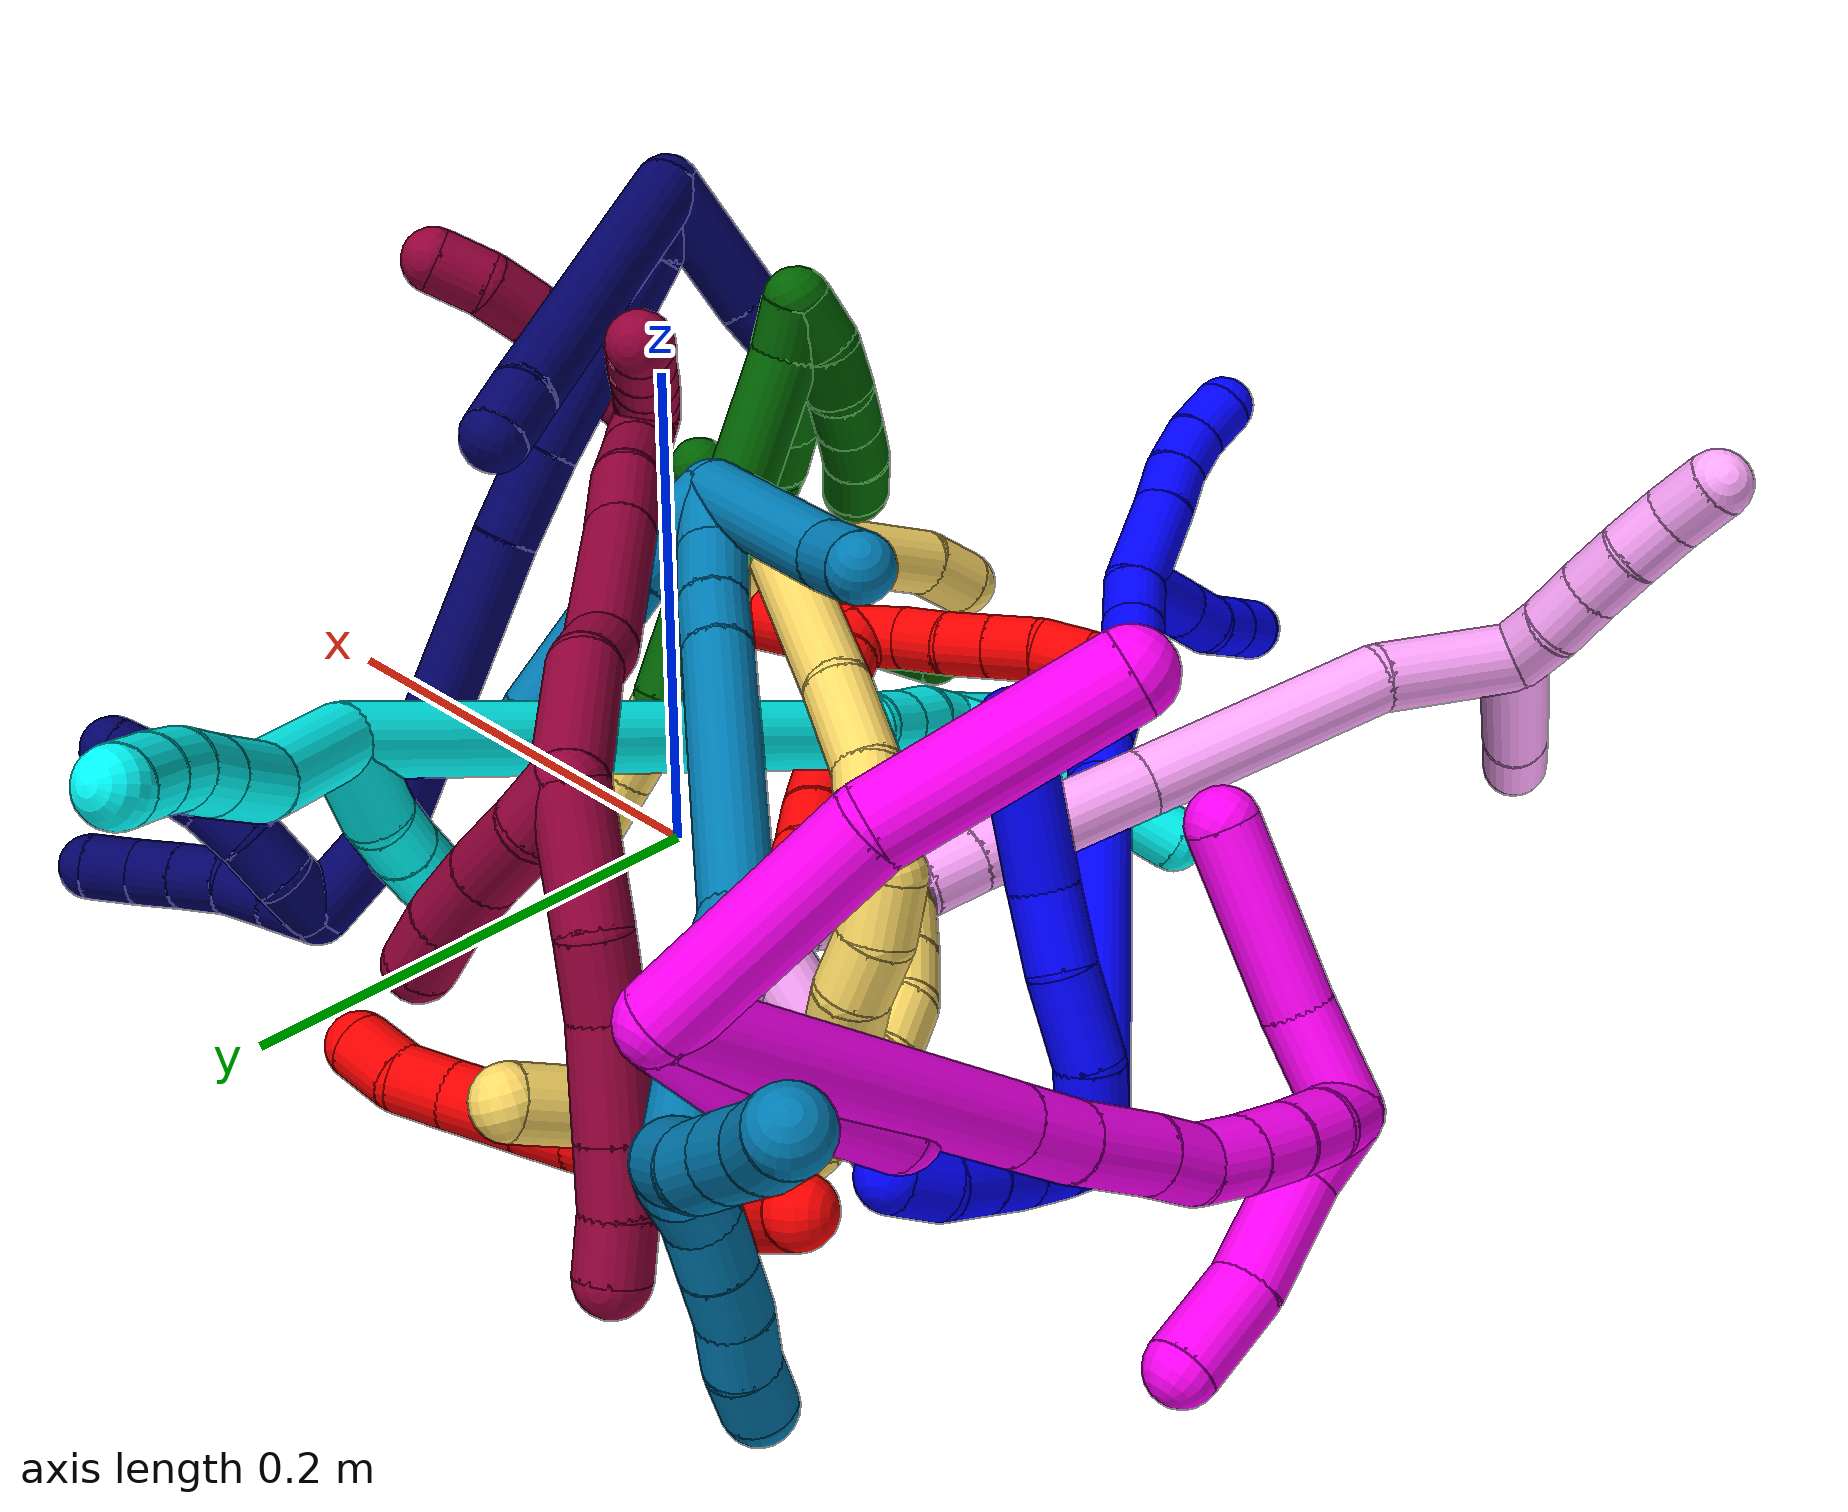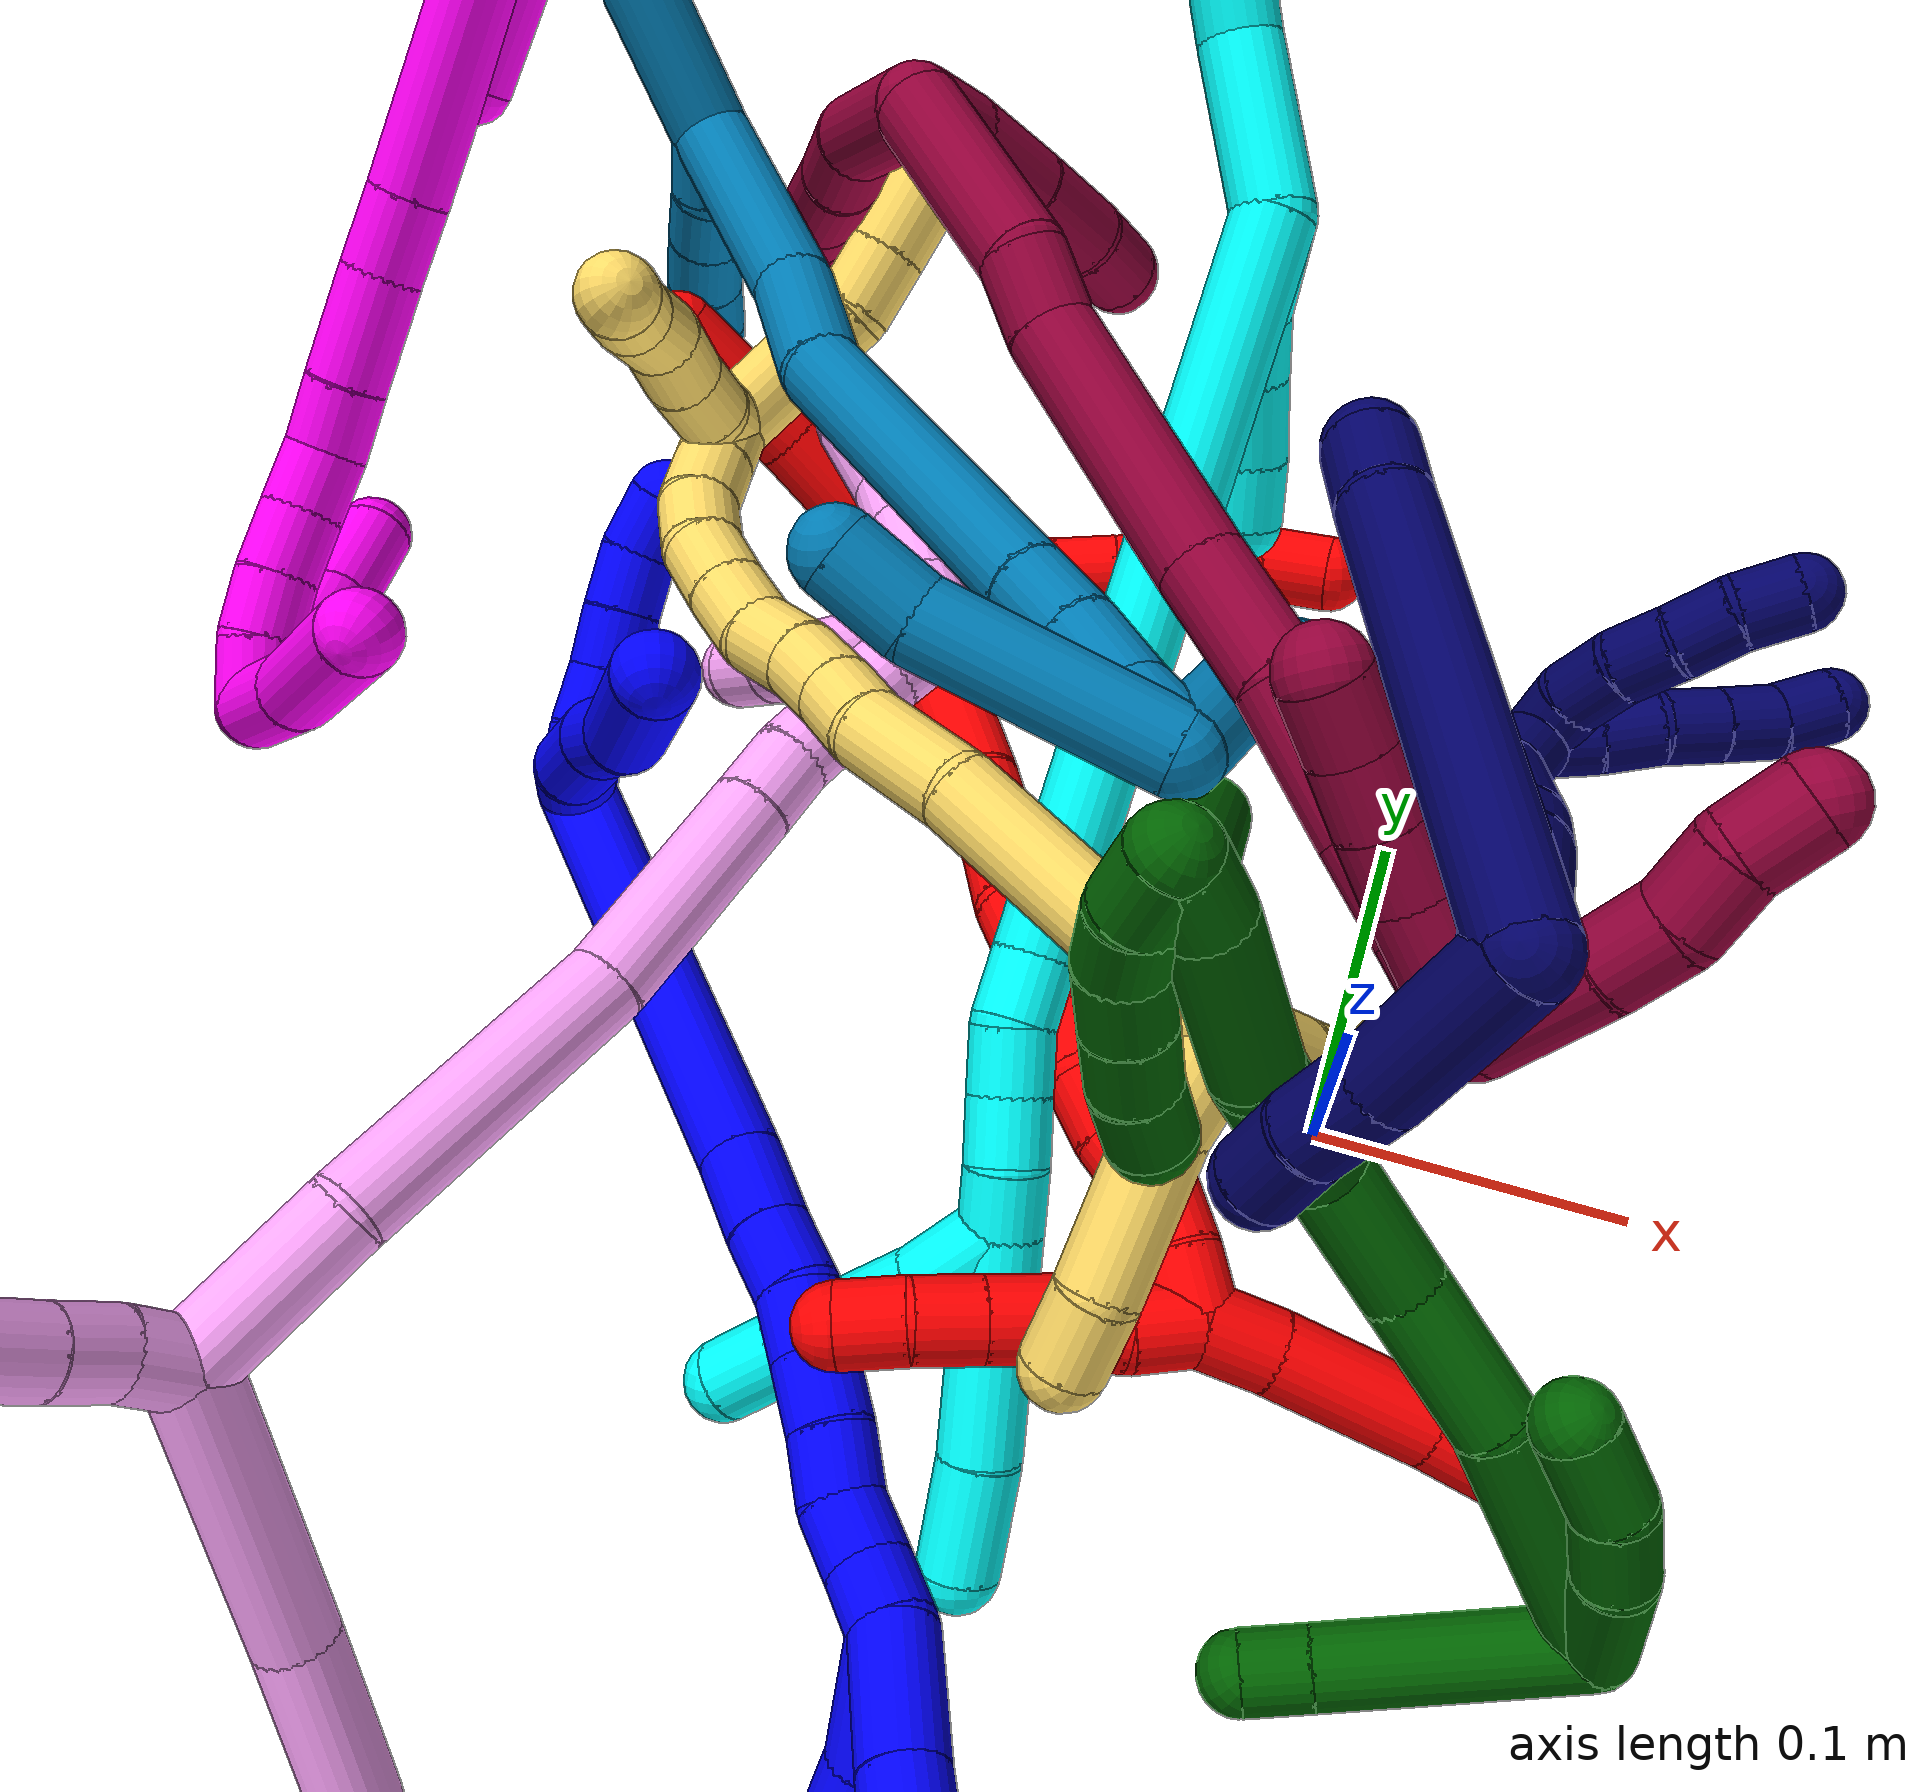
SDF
<sdf version="1.7">
 <world name="default">
  <plugin name="TubeGeneratorPlugin" filename="libtube_generator_plugin.so"/>
  <model name="photoneo_s_sensor">
   <static>1</static>
   <pose>0 0 2 1.57079 1.57079 3.14159</pose>
   <link name="link">
    <inertial><mass>0.1</mass></inertial>
    <sensor name="sensor" type="depth">
     <update_rate>30</update_rate>
     <camera>
      <horizontal_fov>1.22</horizontal_fov>
      <image><width>1920</width><height>1200</height><format>B8G8R8</format></image>
      <clip><near>0.1</near><far>4</far></clip>
      <depth_camera><output>points</output></depth_camera>
     </camera>
     <plugin name="camera_plugin" filename="libgazebo_ros_depth_camera.so">
      <baseline>0.2</baseline>
      <alwaysOn>1</alwaysOn>
      <updateRate>0.0</updateRate>
      <cameraName>camera_ir</cameraName>
      <imageTopicName>/camera/color/image_raw</imageTopicName>
      <cameraInfoTopicName>/camera/color/camera_info</cameraInfoTopicName>
      <depthImageTopicName>/camera/depth/image_raw</depthImageTopicName>
      <depthImageCameraInfoTopicName>/camera/depth/camera_info</depthImageCameraInfoTopicName>
      <pointCloudTopicName>/camera/depth/points</pointCloudTopicName>
      <frameName>fr_optical</frameName>
      <pointCloudCutoff>0.1</pointCloudCutoff>
      <pointCloudCutoffMax>2.0</pointCloudCutoffMax>
      <distortionK1>0</distortionK1>
      <distortionK2>0</distortionK2>
      <distortionK3>0</distortionK3>
      <distortionT1>0</distortionT1>
      <distortionT2>0</distortionT2>
      <CxPrime>0</CxPrime>
      <Cx>0</Cx>
      <Cy>0</Cy>
      <focalLength>0</focalLength>
      <hackBaseline>0</hackBaseline>
     </plugin>
    </sensor>
   </link>
  </model>
  <gravity>0 0 -9.8</gravity>
  <magnetic_field>6e-06 2.3e-05 -4.2e-05</magnetic_field>
  <atmosphere type="adiabatic"/>
  <physics name="default_physics" default="0" type="ode">
   <max_step_size>0.003</max_step_size>
   <real_time_factor>1</real_time_factor>
   <real_time_update_rate>1000</real_time_update_rate>
   <max_contacts>10000</max_contacts>
   <ode>
    <solver>
     <type>quick</type>
     <iters>100</iters>
     <sor>1.3</sor>
     <use_dynamic_moi_rescaling>0</use_dynamic_moi_rescaling>
    </solver>
    <constraints>
     <contact_max_correcting_vel>0</contact_max_correcting_vel>
     <contact_surface_layer>0.001</contact_surface_layer>
     <cfm>0</cfm>
     <erp>0.2</erp>
    </constraints>
   </ode>
  </physics>
  <scene><ambient>0.4 0.4 0.4 1</ambient><background>0.7 0.7 0.7 1</background><shadows>0</shadows></scene>
  <audio><device>default</device></audio>
  <spherical_coordinates>
   <surface_model>EARTH_WGS84</surface_model>
   <latitude_deg>0</latitude_deg>
   <longitude_deg>0</longitude_deg>
   <elevation>0</elevation>
   <heading_deg>0</heading_deg>
  </spherical_coordinates>
  <model name="bin">
   <static>1</static>
   <link name="bottom">
    <collision name="collision-bottom">
     <pose>0 0 -0.01 0 -0 0</pose>
     <geometry><box><size>0.8 0.6 0.02</size></box></geometry>
     <surface>
      <friction><ode><mu>100</mu><mu2>100</mu2></ode></friction>
      <contact><collide_bitmask>65535</collide_bitmask></contact>
     </surface>
    </collision>
   </link>
   <link name="west_wall">
    <collision name="collision-west_wall">
     <pose>-0.41 0 0.1 0 -0 0</pose>
     <geometry><box><size>0.02 0.6 0.2</size></box></geometry>
     <surface>
      <friction><ode><mu>100</mu><mu2>100</mu2></ode></friction>
      <contact><collide_bitmask>65535</collide_bitmask></contact>
     </surface>
    </collision>
   </link>
   <link name="east_wall">
    <collision name="collision-east_wall">
     <pose>0.41 0 0.1 0 -0 0</pose>
     <geometry><box><size>0.02 0.6 0.2</size></box></geometry>
     <surface>
      <friction><ode><mu>100</mu><mu2>100</mu2></ode></friction>
      <contact><collide_bitmask>65535</collide_bitmask></contact>
     </surface>
    </collision>
   </link>
   <link name="south_wall">
    <collision name="collision-south_wall">
     <pose>0 -0.31 0.1 0 -0 0</pose>
     <geometry><box><size>0.8 0.02 0.2</size></box></geometry>
     <surface>
      <friction><ode><mu>100</mu><mu2>100</mu2></ode></friction>
      <contact><collide_bitmask>65535</collide_bitmask></contact>
     </surface>
    </collision>
   </link>
   <link name="north_wall">
    <collision name="collision-north_wall">
     <pose>0 0.31 0.1 0 -0 0</pose>
     <geometry><box><size>0.8 0.02 0.2</size></box></geometry>
     <surface>
      <friction><ode><mu>100</mu><mu2>100</mu2></ode></friction>
      <contact><collide_bitmask>65535</collide_bitmask></contact>
     </surface>
    </collision>
   </link>
  </model>
  <model name="1">
   <static>0</static>
   <link name="1">
    <collision name="collision-cylinder-e_1_2_8">
     <pose>-0.001697 0.013759 0.007255 -1.08556 -0.108677 0.065597</pose>
     <geometry><cylinder><radius>0.0125</radius><length>0.031293</length></cylinder></geometry>
     <surface>
      <friction><ode><mu>1.16</mu><mu2>1.16</mu2><slip1>0</slip1><slip2>0</slip2></ode></friction>
      <contact><ode><kp>1e+06</kp><kd>1</kd><max_vel>0</max_vel><min_depth>0.001</min_depth></ode></contact>
     </surface>
    </collision>
    <visual name="visual-cylinder-e_1_2_8">
     <pose>-0.001697 0.013759 0.007255 -1.08556 -0.108677 0.065597</pose>
     <geometry><cylinder><radius>0.0125</radius><length>0.031293</length></cylinder></geometry>
     <material><ambient>0 0 1 1</ambient></material>
    </visual>
    <collision name="collision-cylinder-e_2_8_9">
     <pose>-0.000878 0.042414 0.022192 -1.09463 0.148987 -0.090901</pose>
     <geometry><cylinder><radius>0.0125</radius><length>0.0339</length></cylinder></geometry>
     <surface>
      <friction><ode><mu>1.16</mu><mu2>1.16</mu2><slip1>0</slip1><slip2>0</slip2></ode></friction>
      <contact><ode><kp>1e+06</kp><kd>1</kd><max_vel>0</max_vel><min_depth>0.001</min_depth></ode></contact>
     </surface>
    </collision>
    <visual name="visual-cylinder-e_2_8_9">
     <pose>-0.000878 0.042414 0.022192 -1.09463 0.148987 -0.090901</pose>
     <geometry><cylinder><radius>0.0125</radius><length>0.0339</length></cylinder></geometry>
     <material><ambient>0 0 1 1</ambient></material>
    </visual>
    <collision name="collision-cylinder-e_3_9_10">
     <pose>0.004041 0.068061 0.038554 -0.891559 0.172227 -0.082458</pose>
     <geometry><cylinder><radius>0.0125</radius><length>0.028044</length></cylinder></geometry>
     <surface>
      <friction><ode><mu>1.16</mu><mu2>1.16</mu2><slip1>0</slip1><slip2>0</slip2></ode></friction>
      <contact><ode><kp>1e+06</kp><kd>1</kd><max_vel>0</max_vel><min_depth>0.001</min_depth></ode></contact>
     </surface>
    </collision>
    <visual name="visual-cylinder-e_3_9_10">
     <pose>0.004041 0.068061 0.038554 -0.891559 0.172227 -0.082458</pose>
     <geometry><cylinder><radius>0.0125</radius><length>0.028044</length></cylinder></geometry>
     <material><ambient>0 0 1 1</ambient></material>
    </visual>
    <collision name="collision-cylinder-e_4_10_6">
     <pose>0.007404 0.104067 0.060142 -1.09829 0.033833 -0.020704</pose>
     <geometry><cylinder><radius>0.0125</radius><length>0.056763</length></cylinder></geometry>
     <surface>
      <friction><ode><mu>1.16</mu><mu2>1.16</mu2><slip1>0</slip1><slip2>0</slip2></ode></friction>
      <contact><ode><kp>1e+06</kp><kd>1</kd><max_vel>0</max_vel><min_depth>0.001</min_depth></ode></contact>
     </surface>
    </collision>
    <visual name="visual-cylinder-e_4_10_6">
     <pose>0.007404 0.104067 0.060142 -1.09829 0.033833 -0.020704</pose>
     <geometry><cylinder><radius>0.0125</radius><length>0.056763</length></cylinder></geometry>
     <material><ambient>0 0 1 1</ambient></material>
    </visual>
    <collision name="collision-cylinder-e_1_2_11">
     <pose>0.001655 0.006126 -0.007729 -2.47138 0.166255 -0.469684</pose>
     <geometry><cylinder><radius>0.0125</radius><length>0.02</length></cylinder></geometry>
     <surface>
      <friction><ode><mu>1.16</mu><mu2>1.16</mu2><slip1>0</slip1><slip2>0</slip2></ode></friction>
      <contact><ode><kp>1e+06</kp><kd>1</kd><max_vel>0</max_vel><min_depth>0.001</min_depth></ode></contact>
     </surface>
    </collision>
    <visual name="visual-cylinder-e_1_2_11">
     <pose>0.001655 0.006126 -0.007729 -2.47138 0.166255 -0.469684</pose>
     <geometry><cylinder><radius>0.0125</radius><length>0.02</length></cylinder></geometry>
     <material><ambient>0 0 1 1</ambient></material>
    </visual>
    <collision name="collision-cylinder-e_2_11_12">
     <pose>0.006029 0.018482 -0.022792 -2.43739 0.275395 -0.721337</pose>
     <geometry><cylinder><radius>0.0125</radius><length>0.02</length></cylinder></geometry>
     <surface>
      <friction><ode><mu>1.16</mu><mu2>1.16</mu2><slip1>0</slip1><slip2>0</slip2></ode></friction>
      <contact><ode><kp>1e+06</kp><kd>1</kd><max_vel>0</max_vel><min_depth>0.001</min_depth></ode></contact>
     </surface>
    </collision>
    <visual name="visual-cylinder-e_2_11_12">
     <pose>0.006029 0.018482 -0.022792 -2.43739 0.275395 -0.721337</pose>
     <geometry><cylinder><radius>0.0125</radius><length>0.02</length></cylinder></geometry>
     <material><ambient>0 0 1 1</ambient></material>
    </visual>
    <collision name="collision-cylinder-e_3_12_13">
     <pose>0.010652 0.03173 -0.03699 -2.34514 0.191533 -0.448971</pose>
     <geometry><cylinder><radius>0.0125</radius><length>0.02</length></cylinder></geometry>
     <surface>
      <friction><ode><mu>1.16</mu><mu2>1.16</mu2><slip1>0</slip1><slip2>0</slip2></ode></friction>
      <contact><ode><kp>1e+06</kp><kd>1</kd><max_vel>0</max_vel><min_depth>0.001</min_depth></ode></contact>
     </surface>
    </collision>
    <visual name="visual-cylinder-e_3_12_13">
     <pose>0.010652 0.03173 -0.03699 -2.34514 0.191533 -0.448971</pose>
     <geometry><cylinder><radius>0.0125</radius><length>0.02</length></cylinder></geometry>
     <material><ambient>0 0 1 1</ambient></material>
    </visual>
    <collision name="collision-cylinder-e_4_13_14">
     <pose>0.014961 0.045566 -0.050764 -2.36281 0.242968 -0.578359</pose>
     <geometry><cylinder><radius>0.0125</radius><length>0.02</length></cylinder></geometry>
     <surface>
      <friction><ode><mu>1.16</mu><mu2>1.16</mu2><slip1>0</slip1><slip2>0</slip2></ode></friction>
      <contact><ode><kp>1e+06</kp><kd>1</kd><max_vel>0</max_vel><min_depth>0.001</min_depth></ode></contact>
     </surface>
    </collision>
    <visual name="visual-cylinder-e_4_13_14">
     <pose>0.014961 0.045566 -0.050764 -2.36281 0.242968 -0.578359</pose>
     <geometry><cylinder><radius>0.0125</radius><length>0.02</length></cylinder></geometry>
     <material><ambient>0 0 1 1</ambient></material>
    </visual>
    <collision name="collision-cylinder-e_5_14_5">
     <pose>0.021369 0.060165 -0.062514 -2.12746 0.411737 -0.719152</pose>
     <geometry><cylinder><radius>0.0125</radius><length>0.02</length></cylinder></geometry>
     <surface>
      <friction><ode><mu>1.16</mu><mu2>1.16</mu2><slip1>0</slip1><slip2>0</slip2></ode></friction>
      <contact><ode><kp>1e+06</kp><kd>1</kd><max_vel>0</max_vel><min_depth>0.001</min_depth></ode></contact>
     </surface>
    </collision>
    <visual name="visual-cylinder-e_5_14_5">
     <pose>0.021369 0.060165 -0.062514 -2.12746 0.411737 -0.719152</pose>
     <geometry><cylinder><radius>0.0125</radius><length>0.02</length></cylinder></geometry>
     <material><ambient>0 0 1 1</ambient></material>
    </visual>
    <collision name="collision-cylinder-e_1_2_15">
     <pose>0.02143 0.001897 0.072326 -0.026228 0.287967 -0.003803</pose>
     <geometry><cylinder><radius>0.0125</radius><length>0.150915</length></cylinder></geometry>
     <surface>
      <friction><ode><mu>1.16</mu><mu2>1.16</mu2><slip1>0</slip1><slip2>0</slip2></ode></friction>
      <contact><ode><kp>1e+06</kp><kd>1</kd><max_vel>0</max_vel><min_depth>0.001</min_depth></ode></contact>
     </surface>
    </collision>
    <visual name="visual-cylinder-e_1_2_15">
     <pose>0.02143 0.001897 0.072326 -0.026228 0.287967 -0.003803</pose>
     <geometry><cylinder><radius>0.0125</radius><length>0.150915</length></cylinder></geometry>
     <material><ambient>0 0 1 1</ambient></material>
    </visual>
    <collision name="collision-cylinder-e_2_15_16">
     <pose>0.046002 0.004208 0.157293 -0.0327 0.243483 -0.004001</pose>
     <geometry><cylinder><radius>0.0125</radius><length>0.026065</length></cylinder></geometry>
     <surface>
      <friction><ode><mu>1.16</mu><mu2>1.16</mu2><slip1>0</slip1><slip2>0</slip2></ode></friction>
      <contact><ode><kp>1e+06</kp><kd>1</kd><max_vel>0</max_vel><min_depth>0.001</min_depth></ode></contact>
     </surface>
    </collision>
    <visual name="visual-cylinder-e_2_15_16">
     <pose>0.046002 0.004208 0.157293 -0.0327 0.243483 -0.004001</pose>
     <geometry><cylinder><radius>0.0125</radius><length>0.026065</length></cylinder></geometry>
     <material><ambient>0 0 1 1</ambient></material>
    </visual>
    <collision name="collision-cylinder-e_3_16_17">
     <pose>0.052409 0.005185 0.180309 -0.054225 0.304435 -0.00832</pose>
     <geometry><cylinder><radius>0.0125</radius><length>0.021783</length></cylinder></geometry>
     <surface>
      <friction><ode><mu>1.16</mu><mu2>1.16</mu2><slip1>0</slip1><slip2>0</slip2></ode></friction>
      <contact><ode><kp>1e+06</kp><kd>1</kd><max_vel>0</max_vel><min_depth>0.001</min_depth></ode></contact>
     </surface>
    </collision>
    <visual name="visual-cylinder-e_3_16_17">
     <pose>0.052409 0.005185 0.180309 -0.054225 0.304435 -0.00832</pose>
     <geometry><cylinder><radius>0.0125</radius><length>0.021783</length></cylinder></geometry>
     <material><ambient>0 0 1 1</ambient></material>
    </visual>
    <collision name="collision-cylinder-e_4_17_18">
     <pose>0.057284 0.004438 0.200539 0.1322 0.160553 0.010651</pose>
     <geometry><cylinder><radius>0.0125</radius><length>0.020141</length></cylinder></geometry>
     <surface>
      <friction><ode><mu>1.16</mu><mu2>1.16</mu2><slip1>0</slip1><slip2>0</slip2></ode></friction>
      <contact><ode><kp>1e+06</kp><kd>1</kd><max_vel>0</max_vel><min_depth>0.001</min_depth></ode></contact>
     </surface>
    </collision>
    <visual name="visual-cylinder-e_4_17_18">
     <pose>0.057284 0.004438 0.200539 0.1322 0.160553 0.010651</pose>
     <geometry><cylinder><radius>0.0125</radius><length>0.020141</length></cylinder></geometry>
     <material><ambient>0 0 1 1</ambient></material>
    </visual>
    <collision name="collision-cylinder-e_5_18_19">
     <pose>0.060496 0.001747 0.220709 0.132989 0.152743 0.010191</pose>
     <geometry><cylinder><radius>0.0125</radius><length>0.021062</length></cylinder></geometry>
     <surface>
      <friction><ode><mu>1.16</mu><mu2>1.16</mu2><slip1>0</slip1><slip2>0</slip2></ode></friction>
      <contact><ode><kp>1e+06</kp><kd>1</kd><max_vel>0</max_vel><min_depth>0.001</min_depth></ode></contact>
     </surface>
    </collision>
    <visual name="visual-cylinder-e_5_18_19">
     <pose>0.060496 0.001747 0.220709 0.132989 0.152743 0.010191</pose>
     <geometry><cylinder><radius>0.0125</radius><length>0.021062</length></cylinder></geometry>
     <material><ambient>0 0 1 1</ambient></material>
    </visual>
    <collision name="collision-cylinder-e_6_19_20">
     <pose>0.063049 -0.001981 0.240713 0.237821 0.095151 0.011377</pose>
     <geometry><cylinder><radius>0.0125</radius><length>0.020026</length></cylinder></geometry>
     <surface>
      <friction><ode><mu>1.16</mu><mu2>1.16</mu2><slip1>0</slip1><slip2>0</slip2></ode></friction>
      <contact><ode><kp>1e+06</kp><kd>1</kd><max_vel>0</max_vel><min_depth>0.001</min_depth></ode></contact>
     </surface>
    </collision>
    <visual name="visual-cylinder-e_6_19_20">
     <pose>0.063049 -0.001981 0.240713 0.237821 0.095151 0.011377</pose>
     <geometry><cylinder><radius>0.0125</radius><length>0.020026</length></cylinder></geometry>
     <material><ambient>0 0 1 1</ambient></material>
    </visual>
    <collision name="collision-cylinder-e_7_20_21">
     <pose>0.066839 -0.004416 0.259988 0.009008 0.287743 0.001305</pose>
     <geometry><cylinder><radius>0.0125</radius><length>0.02</length></cylinder></geometry>
     <surface>
      <friction><ode><mu>1.16</mu><mu2>1.16</mu2><slip1>0</slip1><slip2>0</slip2></ode></friction>
      <contact><ode><kp>1e+06</kp><kd>1</kd><max_vel>0</max_vel><min_depth>0.001</min_depth></ode></contact>
     </surface>
    </collision>
    <visual name="visual-cylinder-e_7_20_21">
     <pose>0.066839 -0.004416 0.259988 0.009008 0.287743 0.001305</pose>
     <geometry><cylinder><radius>0.0125</radius><length>0.02</length></cylinder></geometry>
     <material><ambient>0 0 1 1</ambient></material>
    </visual>
    <collision name="collision-cylinder-e_8_21_1">
     <pose>0.0715 -0.002141 0.279126 -0.24237 0.183337 -0.022389</pose>
     <geometry><cylinder><radius>0.0125</radius><length>0.020009</length></cylinder></geometry>
     <surface>
      <friction><ode><mu>1.16</mu><mu2>1.16</mu2><slip1>0</slip1><slip2>0</slip2></ode></friction>
      <contact><ode><kp>1e+06</kp><kd>1</kd><max_vel>0</max_vel><min_depth>0.001</min_depth></ode></contact>
     </surface>
    </collision>
    <visual name="visual-cylinder-e_8_21_1">
     <pose>0.0715 -0.002141 0.279126 -0.24237 0.183337 -0.022389</pose>
     <geometry><cylinder><radius>0.0125</radius><length>0.020009</length></cylinder></geometry>
     <material><ambient>0 0 1 1</ambient></material>
    </visual>
    <collision name="collision-cylinder-e_1_1_22">
     <pose>0.072033 -0.016397 0.299414 0.997028 -0.065179 -0.035491</pose>
     <geometry><cylinder><radius>0.0125</radius><length>0.039654</length></cylinder></geometry>
     <surface>
      <friction><ode><mu>1.16</mu><mu2>1.16</mu2><slip1>0</slip1><slip2>0</slip2></ode></friction>
      <contact><ode><kp>1e+06</kp><kd>1</kd><max_vel>0</max_vel><min_depth>0.001</min_depth></ode></contact>
     </surface>
    </collision>
    <visual name="visual-cylinder-e_1_1_22">
     <pose>0.072033 -0.016397 0.299414 0.997028 -0.065179 -0.035491</pose>
     <geometry><cylinder><radius>0.0125</radius><length>0.039654</length></cylinder></geometry>
     <material><ambient>0 0 1 1</ambient></material>
    </visual>
    <collision name="collision-cylinder-e_2_22_23">
     <pose>0.068588 -0.041787 0.314638 1.09826 -0.215144 -0.131967</pose>
     <geometry><cylinder><radius>0.0125</radius><length>0.020171</length></cylinder></geometry>
     <surface>
      <friction><ode><mu>1.16</mu><mu2>1.16</mu2><slip1>0</slip1><slip2>0</slip2></ode></friction>
      <contact><ode><kp>1e+06</kp><kd>1</kd><max_vel>0</max_vel><min_depth>0.001</min_depth></ode></contact>
     </surface>
    </collision>
    <visual name="visual-cylinder-e_2_22_23">
     <pose>0.068588 -0.041787 0.314638 1.09826 -0.215144 -0.131967</pose>
     <geometry><cylinder><radius>0.0125</radius><length>0.020171</length></cylinder></geometry>
     <material><ambient>0 0 1 1</ambient></material>
    </visual>
    <collision name="collision-cylinder-e_3_23_24">
     <pose>0.065606 -0.057764 0.326041 0.805625 -0.082832 -0.035312</pose>
     <geometry><cylinder><radius>0.0125</radius><length>0.020046</length></cylinder></geometry>
     <surface>
      <friction><ode><mu>1.16</mu><mu2>1.16</mu2><slip1>0</slip1><slip2>0</slip2></ode></friction>
      <contact><ode><kp>1e+06</kp><kd>1</kd><max_vel>0</max_vel><min_depth>0.001</min_depth></ode></contact>
     </surface>
    </collision>
    <visual name="visual-cylinder-e_3_23_24">
     <pose>0.065606 -0.057764 0.326041 0.805625 -0.082832 -0.035312</pose>
     <geometry><cylinder><radius>0.0125</radius><length>0.020046</length></cylinder></geometry>
     <material><ambient>0 0 1 1</ambient></material>
    </visual>
    <collision name="collision-cylinder-e_4_24_4">
     <pose>0.064066 -0.072229 0.339894 0.80834 -0.070644 -0.030226</pose>
     <geometry><cylinder><radius>0.0125</radius><length>0.020129</length></cylinder></geometry>
     <surface>
      <friction><ode><mu>1.16</mu><mu2>1.16</mu2><slip1>0</slip1><slip2>0</slip2></ode></friction>
      <contact><ode><kp>1e+06</kp><kd>1</kd><max_vel>0</max_vel><min_depth>0.001</min_depth></ode></contact>
     </surface>
    </collision>
    <visual name="visual-cylinder-e_4_24_4">
     <pose>0.064066 -0.072229 0.339894 0.80834 -0.070644 -0.030226</pose>
     <geometry><cylinder><radius>0.0125</radius><length>0.020129</length></cylinder></geometry>
     <material><ambient>0 0 1 1</ambient></material>
    </visual>
    <collision name="collision-cylinder-e_1_1_25">
     <pose>0.071913 0.003044 0.30825 -0.143308 -0.071216 0.005114</pose>
     <geometry><cylinder><radius>0.0125</radius><length>0.039657</length></cylinder></geometry>
     <surface>
      <friction><ode><mu>1.16</mu><mu2>1.16</mu2><slip1>0</slip1><slip2>0</slip2></ode></friction>
      <contact><ode><kp>1e+06</kp><kd>1</kd><max_vel>0</max_vel><min_depth>0.001</min_depth></ode></contact>
     </surface>
    </collision>
    <visual name="visual-cylinder-e_1_1_25">
     <pose>0.071913 0.003044 0.30825 -0.143308 -0.071216 0.005114</pose>
     <geometry><cylinder><radius>0.0125</radius><length>0.039657</length></cylinder></geometry>
     <material><ambient>0 0 1 1</ambient></material>
    </visual>
    <collision name="collision-cylinder-e_2_25_26">
     <pose>0.070284 0.007477 0.33778 -0.16018 -0.021714 0.001743</pose>
     <geometry><cylinder><radius>0.0125</radius><length>0.02017</length></cylinder></geometry>
     <surface>
      <friction><ode><mu>1.16</mu><mu2>1.16</mu2><slip1>0</slip1><slip2>0</slip2></ode></friction>
      <contact><ode><kp>1e+06</kp><kd>1</kd><max_vel>0</max_vel><min_depth>0.001</min_depth></ode></contact>
     </surface>
    </collision>
    <visual name="visual-cylinder-e_2_25_26">
     <pose>0.070284 0.007477 0.33778 -0.16018 -0.021714 0.001743</pose>
     <geometry><cylinder><radius>0.0125</radius><length>0.02017</length></cylinder></geometry>
     <material><ambient>0 0 1 1</ambient></material>
    </visual>
    <collision name="collision-cylinder-e_3_26_27">
     <pose>0.068208 0.009961 0.357541 -0.089077 -0.186349 0.008329</pose>
     <geometry><cylinder><radius>0.0125</radius><length>0.020041</length></cylinder></geometry>
     <surface>
      <friction><ode><mu>1.16</mu><mu2>1.16</mu2><slip1>0</slip1><slip2>0</slip2></ode></friction>
      <contact><ode><kp>1e+06</kp><kd>1</kd><max_vel>0</max_vel><min_depth>0.001</min_depth></ode></contact>
     </surface>
    </collision>
    <visual name="visual-cylinder-e_3_26_27">
     <pose>0.068208 0.009961 0.357541 -0.089077 -0.186349 0.008329</pose>
     <geometry><cylinder><radius>0.0125</radius><length>0.020041</length></cylinder></geometry>
     <material><ambient>0 0 1 1</ambient></material>
    </visual>
    <collision name="collision-cylinder-e_4_27_3">
     <pose>0.062759 0.010883 0.376752 -0.004864 -0.364976 0.000898</pose>
     <geometry><cylinder><radius>0.0125</radius><length>0.020132</length></cylinder></geometry>
     <surface>
      <friction><ode><mu>1.16</mu><mu2>1.16</mu2><slip1>0</slip1><slip2>0</slip2></ode></friction>
      <contact><ode><kp>1e+06</kp><kd>1</kd><max_vel>0</max_vel><min_depth>0.001</min_depth></ode></contact>
     </surface>
    </collision>
    <visual name="visual-cylinder-e_4_27_3">
     <pose>0.062759 0.010883 0.376752 -0.004864 -0.364976 0.000898</pose>
     <geometry><cylinder><radius>0.0125</radius><length>0.020132</length></cylinder></geometry>
     <material><ambient>0 0 1 1</ambient></material>
    </visual>
    <collision name="collision-sphere-3">
     <pose>0.059166 0.010929 0.386155 0 -0 0</pose>
     <geometry><sphere><radius>0.0125</radius></sphere></geometry>
     <surface>
      <friction><ode><mu>1.16</mu><mu2>1.16</mu2><slip1>0</slip1><slip2>0</slip2></ode></friction>
      <contact><ode><kp>1e+06</kp><kd>1</kd><max_vel>0</max_vel><min_depth>0.001</min_depth></ode></contact>
     </surface>
    </collision>
    <visual name="visual-sphere-3">
     <pose>0.059166 0.010929 0.386155 0 -0 0</pose>
     <geometry><sphere><radius>0.0125</radius></sphere></geometry>
     <material><ambient>0 0 1 1</ambient></material>
    </visual>
    <collision name="collision-sphere-27">
     <pose>0.066352 0.010837 0.367349 0 -0 0</pose>
     <geometry><sphere><radius>0.0125</radius></sphere></geometry>
     <surface>
      <friction><ode><mu>1.16</mu><mu2>1.16</mu2><slip1>0</slip1><slip2>0</slip2></ode></friction>
      <contact><ode><kp>1e+06</kp><kd>1</kd><max_vel>0</max_vel><min_depth>0.001</min_depth></ode></contact>
     </surface>
    </collision>
    <visual name="visual-sphere-27">
     <pose>0.066352 0.010837 0.367349 0 -0 0</pose>
     <geometry><sphere><radius>0.0125</radius></sphere></geometry>
     <material><ambient>0 0 1 1</ambient></material>
    </visual>
    <collision name="collision-sphere-26">
     <pose>0.070065 0.009085 0.347733 0 -0 0</pose>
     <geometry><sphere><radius>0.0125</radius></sphere></geometry>
     <surface>
      <friction><ode><mu>1.16</mu><mu2>1.16</mu2><slip1>0</slip1><slip2>0</slip2></ode></friction>
      <contact><ode><kp>1e+06</kp><kd>1</kd><max_vel>0</max_vel><min_depth>0.001</min_depth></ode></contact>
     </surface>
    </collision>
    <visual name="visual-sphere-26">
     <pose>0.070065 0.009085 0.347733 0 -0 0</pose>
     <geometry><sphere><radius>0.0125</radius></sphere></geometry>
     <material><ambient>0 0 1 1</ambient></material>
    </visual>
    <collision name="collision-sphere-25">
     <pose>0.070503 0.005869 0.327826 0 -0 0</pose>
     <geometry><sphere><radius>0.0125</radius></sphere></geometry>
     <surface>
      <friction><ode><mu>1.16</mu><mu2>1.16</mu2><slip1>0</slip1><slip2>0</slip2></ode></friction>
      <contact><ode><kp>1e+06</kp><kd>1</kd><max_vel>0</max_vel><min_depth>0.001</min_depth></ode></contact>
     </surface>
    </collision>
    <visual name="visual-sphere-25">
     <pose>0.070503 0.005869 0.327826 0 -0 0</pose>
     <geometry><sphere><radius>0.0125</radius></sphere></geometry>
     <material><ambient>0 0 1 1</ambient></material>
    </visual>
    <collision name="collision-sphere-4">
     <pose>0.063356 -0.079489 0.346828 0 -0 0</pose>
     <geometry><sphere><radius>0.0125</radius></sphere></geometry>
     <surface>
      <friction><ode><mu>1.16</mu><mu2>1.16</mu2><slip1>0</slip1><slip2>0</slip2></ode></friction>
      <contact><ode><kp>1e+06</kp><kd>1</kd><max_vel>0</max_vel><min_depth>0.001</min_depth></ode></contact>
     </surface>
    </collision>
    <visual name="visual-sphere-4">
     <pose>0.063356 -0.079489 0.346828 0 -0 0</pose>
     <geometry><sphere><radius>0.0125</radius></sphere></geometry>
     <material><ambient>0 0 1 1</ambient></material>
    </visual>
    <collision name="collision-sphere-24">
     <pose>0.064777 -0.064969 0.33296 0 -0 0</pose>
     <geometry><sphere><radius>0.0125</radius></sphere></geometry>
     <surface>
      <friction><ode><mu>1.16</mu><mu2>1.16</mu2><slip1>0</slip1><slip2>0</slip2></ode></friction>
      <contact><ode><kp>1e+06</kp><kd>1</kd><max_vel>0</max_vel><min_depth>0.001</min_depth></ode></contact>
     </surface>
    </collision>
    <visual name="visual-sphere-24">
     <pose>0.064777 -0.064969 0.33296 0 -0 0</pose>
     <geometry><sphere><radius>0.0125</radius></sphere></geometry>
     <material><ambient>0 0 1 1</ambient></material>
    </visual>
    <collision name="collision-sphere-23">
     <pose>0.066435 -0.05056 0.319122 0 -0 0</pose>
     <geometry><sphere><radius>0.0125</radius></sphere></geometry>
     <surface>
      <friction><ode><mu>1.16</mu><mu2>1.16</mu2><slip1>0</slip1><slip2>0</slip2></ode></friction>
      <contact><ode><kp>1e+06</kp><kd>1</kd><max_vel>0</max_vel><min_depth>0.001</min_depth></ode></contact>
     </surface>
    </collision>
    <visual name="visual-sphere-23">
     <pose>0.066435 -0.05056 0.319122 0 -0 0</pose>
     <geometry><sphere><radius>0.0125</radius></sphere></geometry>
     <material><ambient>0 0 1 1</ambient></material>
    </visual>
    <collision name="collision-sphere-22">
     <pose>0.070742 -0.033013 0.310153 0 -0 0</pose>
     <geometry><sphere><radius>0.0125</radius></sphere></geometry>
     <surface>
      <friction><ode><mu>1.16</mu><mu2>1.16</mu2><slip1>0</slip1><slip2>0</slip2></ode></friction>
      <contact><ode><kp>1e+06</kp><kd>1</kd><max_vel>0</max_vel><min_depth>0.001</min_depth></ode></contact>
     </surface>
    </collision>
    <visual name="visual-sphere-22">
     <pose>0.070742 -0.033013 0.310153 0 -0 0</pose>
     <geometry><sphere><radius>0.0125</radius></sphere></geometry>
     <material><ambient>0 0 1 1</ambient></material>
    </visual>
    <collision name="collision-sphere-1">
     <pose>0.073324 0.00022 0.288675 0 -0 0</pose>
     <geometry><sphere><radius>0.0125</radius></sphere></geometry>
     <surface>
      <friction><ode><mu>1.16</mu><mu2>1.16</mu2><slip1>0</slip1><slip2>0</slip2></ode></friction>
      <contact><ode><kp>1e+06</kp><kd>1</kd><max_vel>0</max_vel><min_depth>0.001</min_depth></ode></contact>
     </surface>
    </collision>
    <visual name="visual-sphere-1">
     <pose>0.073324 0.00022 0.288675 0 -0 0</pose>
     <geometry><sphere><radius>0.0125</radius></sphere></geometry>
     <material><ambient>0 0 1 1</ambient></material>
    </visual>
    <collision name="collision-sphere-21">
     <pose>0.069677 -0.004502 0.269577 0 -0 0</pose>
     <geometry><sphere><radius>0.0125</radius></sphere></geometry>
     <surface>
      <friction><ode><mu>1.16</mu><mu2>1.16</mu2><slip1>0</slip1><slip2>0</slip2></ode></friction>
      <contact><ode><kp>1e+06</kp><kd>1</kd><max_vel>0</max_vel><min_depth>0.001</min_depth></ode></contact>
     </surface>
    </collision>
    <visual name="visual-sphere-21">
     <pose>0.069677 -0.004502 0.269577 0 -0 0</pose>
     <geometry><sphere><radius>0.0125</radius></sphere></geometry>
     <material><ambient>0 0 1 1</ambient></material>
    </visual>
    <collision name="collision-sphere-11">
     <pose>0.00331 0.012252 -0.015458 0 -0 0</pose>
     <geometry><sphere><radius>0.0125</radius></sphere></geometry>
     <surface>
      <friction><ode><mu>1.16</mu><mu2>1.16</mu2><slip1>0</slip1><slip2>0</slip2></ode></friction>
      <contact><ode><kp>1e+06</kp><kd>1</kd><max_vel>0</max_vel><min_depth>0.001</min_depth></ode></contact>
     </surface>
    </collision>
    <visual name="visual-sphere-11">
     <pose>0.00331 0.012252 -0.015458 0 -0 0</pose>
     <geometry><sphere><radius>0.0125</radius></sphere></geometry>
     <material><ambient>0 0 1 1</ambient></material>
    </visual>
    <collision name="collision-sphere-6">
     <pose>0.008364 0.129324 0.073052 0 -0 0</pose>
     <geometry><sphere><radius>0.0125</radius></sphere></geometry>
     <surface>
      <friction><ode><mu>1.16</mu><mu2>1.16</mu2><slip1>0</slip1><slip2>0</slip2></ode></friction>
      <contact><ode><kp>1e+06</kp><kd>1</kd><max_vel>0</max_vel><min_depth>0.001</min_depth></ode></contact>
     </surface>
    </collision>
    <visual name="visual-sphere-6">
     <pose>0.008364 0.129324 0.073052 0 -0 0</pose>
     <geometry><sphere><radius>0.0125</radius></sphere></geometry>
     <material><ambient>0 0 1 1</ambient></material>
    </visual>
    <collision name="collision-sphere-10">
     <pose>0.006444 0.078809 0.047233 0 -0 0</pose>
     <geometry><sphere><radius>0.0125</radius></sphere></geometry>
     <surface>
      <friction><ode><mu>1.16</mu><mu2>1.16</mu2><slip1>0</slip1><slip2>0</slip2></ode></friction>
      <contact><ode><kp>1e+06</kp><kd>1</kd><max_vel>0</max_vel><min_depth>0.001</min_depth></ode></contact>
     </surface>
    </collision>
    <visual name="visual-sphere-10">
     <pose>0.006444 0.078809 0.047233 0 -0 0</pose>
     <geometry><sphere><radius>0.0125</radius></sphere></geometry>
     <material><ambient>0 0 1 1</ambient></material>
    </visual>
    <collision name="collision-sphere-9">
     <pose>0.001638 0.057312 0.029876 0 -0 0</pose>
     <geometry><sphere><radius>0.0125</radius></sphere></geometry>
     <surface>
      <friction><ode><mu>1.16</mu><mu2>1.16</mu2><slip1>0</slip1><slip2>0</slip2></ode></friction>
      <contact><ode><kp>1e+06</kp><kd>1</kd><max_vel>0</max_vel><min_depth>0.001</min_depth></ode></contact>
     </surface>
    </collision>
    <visual name="visual-sphere-9">
     <pose>0.001638 0.057312 0.029876 0 -0 0</pose>
     <geometry><sphere><radius>0.0125</radius></sphere></geometry>
     <material><ambient>0 0 1 1</ambient></material>
    </visual>
    <collision name="collision-sphere-2">
     <geometry><sphere><radius>0.0125</radius></sphere></geometry>
     <surface>
      <friction><ode><mu>1.16</mu><mu2>1.16</mu2><slip1>0</slip1><slip2>0</slip2></ode></friction>
      <contact><ode><kp>1e+06</kp><kd>1</kd><max_vel>0</max_vel><min_depth>0.001</min_depth></ode></contact>
     </surface>
    </collision>
    <visual name="visual-sphere-2">
     <geometry><sphere><radius>0.0125</radius></sphere></geometry>
     <material><ambient>0 0 1 1</ambient></material>
    </visual>
    <collision name="collision-sphere-19">
     <pose>0.062098 0.000367 0.231026 0 -0 0</pose>
     <geometry><sphere><radius>0.0125</radius></sphere></geometry>
     <surface>
      <friction><ode><mu>1.16</mu><mu2>1.16</mu2><slip1>0</slip1><slip2>0</slip2></ode></friction>
      <contact><ode><kp>1e+06</kp><kd>1</kd><max_vel>0</max_vel><min_depth>0.001</min_depth></ode></contact>
     </surface>
    </collision>
    <visual name="visual-sphere-19">
     <pose>0.062098 0.000367 0.231026 0 -0 0</pose>
     <geometry><sphere><radius>0.0125</radius></sphere></geometry>
     <material><ambient>0 0 1 1</ambient></material>
    </visual>
    <collision name="collision-sphere-8">
     <pose>-0.003394 0.027517 0.014509 0 -0 0</pose>
     <geometry><sphere><radius>0.0125</radius></sphere></geometry>
     <surface>
      <friction><ode><mu>1.16</mu><mu2>1.16</mu2><slip1>0</slip1><slip2>0</slip2></ode></friction>
      <contact><ode><kp>1e+06</kp><kd>1</kd><max_vel>0</max_vel><min_depth>0.001</min_depth></ode></contact>
     </surface>
    </collision>
    <visual name="visual-sphere-8">
     <pose>-0.003394 0.027517 0.014509 0 -0 0</pose>
     <geometry><sphere><radius>0.0125</radius></sphere></geometry>
     <material><ambient>0 0 1 1</ambient></material>
    </visual>
    <collision name="collision-sphere-12">
     <pose>0.008748 0.024712 -0.030126 0 -0 0</pose>
     <geometry><sphere><radius>0.0125</radius></sphere></geometry>
     <surface>
      <friction><ode><mu>1.16</mu><mu2>1.16</mu2><slip1>0</slip1><slip2>0</slip2></ode></friction>
      <contact><ode><kp>1e+06</kp><kd>1</kd><max_vel>0</max_vel><min_depth>0.001</min_depth></ode></contact>
     </surface>
    </collision>
    <visual name="visual-sphere-12">
     <pose>0.008748 0.024712 -0.030126 0 -0 0</pose>
     <geometry><sphere><radius>0.0125</radius></sphere></geometry>
     <material><ambient>0 0 1 1</ambient></material>
    </visual>
    <collision name="collision-sphere-13">
     <pose>0.012556 0.038748 -0.043855 0 -0 0</pose>
     <geometry><sphere><radius>0.0125</radius></sphere></geometry>
     <surface>
      <friction><ode><mu>1.16</mu><mu2>1.16</mu2><slip1>0</slip1><slip2>0</slip2></ode></friction>
      <contact><ode><kp>1e+06</kp><kd>1</kd><max_vel>0</max_vel><min_depth>0.001</min_depth></ode></contact>
     </surface>
    </collision>
    <visual name="visual-sphere-13">
     <pose>0.012556 0.038748 -0.043855 0 -0 0</pose>
     <geometry><sphere><radius>0.0125</radius></sphere></geometry>
     <material><ambient>0 0 1 1</ambient></material>
    </visual>
    <collision name="collision-sphere-14">
     <pose>0.017367 0.052384 -0.057672 0 -0 0</pose>
     <geometry><sphere><radius>0.0125</radius></sphere></geometry>
     <surface>
      <friction><ode><mu>1.16</mu><mu2>1.16</mu2><slip1>0</slip1><slip2>0</slip2></ode></friction>
      <contact><ode><kp>1e+06</kp><kd>1</kd><max_vel>0</max_vel><min_depth>0.001</min_depth></ode></contact>
     </surface>
    </collision>
    <visual name="visual-sphere-14">
     <pose>0.017367 0.052384 -0.057672 0 -0 0</pose>
     <geometry><sphere><radius>0.0125</radius></sphere></geometry>
     <material><ambient>0 0 1 1</ambient></material>
    </visual>
    <collision name="collision-sphere-5">
     <pose>0.025371 0.067945 -0.067356 0 -0 0</pose>
     <geometry><sphere><radius>0.0125</radius></sphere></geometry>
     <surface>
      <friction><ode><mu>1.16</mu><mu2>1.16</mu2><slip1>0</slip1><slip2>0</slip2></ode></friction>
      <contact><ode><kp>1e+06</kp><kd>1</kd><max_vel>0</max_vel><min_depth>0.001</min_depth></ode></contact>
     </surface>
    </collision>
    <visual name="visual-sphere-5">
     <pose>0.025371 0.067945 -0.067356 0 -0 0</pose>
     <geometry><sphere><radius>0.0125</radius></sphere></geometry>
     <material><ambient>0 0 1 1</ambient></material>
    </visual>
    <collision name="collision-sphere-15">
     <pose>0.042861 0.003795 0.144651 0 -0 0</pose>
     <geometry><sphere><radius>0.0125</radius></sphere></geometry>
     <surface>
      <friction><ode><mu>1.16</mu><mu2>1.16</mu2><slip1>0</slip1><slip2>0</slip2></ode></friction>
      <contact><ode><kp>1e+06</kp><kd>1</kd><max_vel>0</max_vel><min_depth>0.001</min_depth></ode></contact>
     </surface>
    </collision>
    <visual name="visual-sphere-15">
     <pose>0.042861 0.003795 0.144651 0 -0 0</pose>
     <geometry><sphere><radius>0.0125</radius></sphere></geometry>
     <material><ambient>0 0 1 1</ambient></material>
    </visual>
    <collision name="collision-sphere-16">
     <pose>0.049144 0.004622 0.169934 0 -0 0</pose>
     <geometry><sphere><radius>0.0125</radius></sphere></geometry>
     <surface>
      <friction><ode><mu>1.16</mu><mu2>1.16</mu2><slip1>0</slip1><slip2>0</slip2></ode></friction>
      <contact><ode><kp>1e+06</kp><kd>1</kd><max_vel>0</max_vel><min_depth>0.001</min_depth></ode></contact>
     </surface>
    </collision>
    <visual name="visual-sphere-16">
     <pose>0.049144 0.004622 0.169934 0 -0 0</pose>
     <geometry><sphere><radius>0.0125</radius></sphere></geometry>
     <material><ambient>0 0 1 1</ambient></material>
    </visual>
    <collision name="collision-sphere-17">
     <pose>0.055674 0.005748 0.190684 0 -0 0</pose>
     <geometry><sphere><radius>0.0125</radius></sphere></geometry>
     <surface>
      <friction><ode><mu>1.16</mu><mu2>1.16</mu2><slip1>0</slip1><slip2>0</slip2></ode></friction>
      <contact><ode><kp>1e+06</kp><kd>1</kd><max_vel>0</max_vel><min_depth>0.001</min_depth></ode></contact>
     </surface>
    </collision>
    <visual name="visual-sphere-17">
     <pose>0.055674 0.005748 0.190684 0 -0 0</pose>
     <geometry><sphere><radius>0.0125</radius></sphere></geometry>
     <material><ambient>0 0 1 1</ambient></material>
    </visual>
    <collision name="collision-sphere-18">
     <pose>0.058894 0.003127 0.210393 0 -0 0</pose>
     <geometry><sphere><radius>0.0125</radius></sphere></geometry>
     <surface>
      <friction><ode><mu>1.16</mu><mu2>1.16</mu2><slip1>0</slip1><slip2>0</slip2></ode></friction>
      <contact><ode><kp>1e+06</kp><kd>1</kd><max_vel>0</max_vel><min_depth>0.001</min_depth></ode></contact>
     </surface>
    </collision>
    <visual name="visual-sphere-18">
     <pose>0.058894 0.003127 0.210393 0 -0 0</pose>
     <geometry><sphere><radius>0.0125</radius></sphere></geometry>
     <material><ambient>0 0 1 1</ambient></material>
    </visual>
    <collision name="collision-sphere-20">
     <pose>0.064001 -0.004329 0.2504 0 -0 0</pose>
     <geometry><sphere><radius>0.0125</radius></sphere></geometry>
     <surface>
      <friction><ode><mu>1.16</mu><mu2>1.16</mu2><slip1>0</slip1><slip2>0</slip2></ode></friction>
      <contact><ode><kp>1e+06</kp><kd>1</kd><max_vel>0</max_vel><min_depth>0.001</min_depth></ode></contact>
     </surface>
    </collision>
    <visual name="visual-sphere-20">
     <pose>0.064001 -0.004329 0.2504 0 -0 0</pose>
     <geometry><sphere><radius>0.0125</radius></sphere></geometry>
     <material><ambient>0 0 1 1</ambient></material>
    </visual>
    <inertial>
     <pose>0.036428 0.0133 0.147305 0 -0 0</pose>
     <mass>0.75</mass>
     <inertia>
      <ixx>0.000348</ixx>
      <ixy>0</ixy>
      <ixz>0</ixz>
      <iyy>0.000335</iyy>
      <iyz>0</iyz>
      <izz>-8.1e-05</izz>
     </inertia>
    </inertial>
   </link>
   <pose>-0.258554 0.042471 0.011609 1.27435 0.268574 0.359426</pose>
  </model>
  <model name="2">
   <static>0</static>
   <link name="2">
    <collision name="collision-cylinder-e_1_2_8">
     <pose>0.006531 -0.004017 -0.01247 2.82993 0.462411 1.96464</pose>
     <geometry><cylinder><radius>0.0125</radius><length>0.029278</length></cylinder></geometry>
     <surface>
      <friction><ode><mu>1.16</mu><mu2>1.16</mu2><slip1>0</slip1><slip2>0</slip2></ode></friction>
      <contact><ode><kp>1e+06</kp><kd>1</kd><max_vel>0</max_vel><min_depth>0.001</min_depth></ode></contact>
     </surface>
    </collision>
    <visual name="visual-cylinder-e_1_2_8">
     <pose>0.006531 -0.004017 -0.01247 2.82993 0.462411 1.96464</pose>
     <geometry><cylinder><radius>0.0125</radius><length>0.029278</length></cylinder></geometry>
     <material><ambient>1 0 0 1</ambient></material>
    </visual>
    <collision name="collision-cylinder-e_2_8_9">
     <pose>0.015182 -0.010682 -0.037951 2.94086 0.158421 1.33503</pose>
     <geometry><cylinder><radius>0.0125</radius><length>0.026891</length></cylinder></geometry>
     <surface>
      <friction><ode><mu>1.16</mu><mu2>1.16</mu2><slip1>0</slip1><slip2>0</slip2></ode></friction>
      <contact><ode><kp>1e+06</kp><kd>1</kd><max_vel>0</max_vel><min_depth>0.001</min_depth></ode></contact>
     </surface>
    </collision>
    <visual name="visual-cylinder-e_2_8_9">
     <pose>0.015182 -0.010682 -0.037951 2.94086 0.158421 1.33503</pose>
     <geometry><cylinder><radius>0.0125</radius><length>0.026891</length></cylinder></geometry>
     <material><ambient>1 0 0 1</ambient></material>
    </visual>
    <collision name="collision-cylinder-e_3_9_10">
     <pose>0.019702 -0.013467 -0.06142 3.1284 0.225431 3.02521</pose>
     <geometry><cylinder><radius>0.0125</radius><length>0.021462</length></cylinder></geometry>
     <surface>
      <friction><ode><mu>1.16</mu><mu2>1.16</mu2><slip1>0</slip1><slip2>0</slip2></ode></friction>
      <contact><ode><kp>1e+06</kp><kd>1</kd><max_vel>0</max_vel><min_depth>0.001</min_depth></ode></contact>
     </surface>
    </collision>
    <visual name="visual-cylinder-e_3_9_10">
     <pose>0.019702 -0.013467 -0.06142 3.1284 0.225431 3.02521</pose>
     <geometry><cylinder><radius>0.0125</radius><length>0.021462</length></cylinder></geometry>
     <material><ambient>1 0 0 1</ambient></material>
    </visual>
    <collision name="collision-cylinder-e_4_10_11">
     <pose>0.025307 -0.014021 -0.086003 3.11219 0.22317 2.88063</pose>
     <geometry><cylinder><radius>0.0125</radius><length>0.02898</length></cylinder></geometry>
     <surface>
      <friction><ode><mu>1.16</mu><mu2>1.16</mu2><slip1>0</slip1><slip2>0</slip2></ode></friction>
      <contact><ode><kp>1e+06</kp><kd>1</kd><max_vel>0</max_vel><min_depth>0.001</min_depth></ode></contact>
     </surface>
    </collision>
    <visual name="visual-cylinder-e_4_10_11">
     <pose>0.025307 -0.014021 -0.086003 3.11219 0.22317 2.88063</pose>
     <geometry><cylinder><radius>0.0125</radius><length>0.02898</length></cylinder></geometry>
     <material><ambient>1 0 0 1</ambient></material>
    </visual>
    <collision name="collision-cylinder-e_5_11_12">
     <pose>0.031146 -0.014115 -0.110226 -3.10977 0.25478 -2.89437</pose>
     <geometry><cylinder><radius>0.0125</radius><length>0.020881</length></cylinder></geometry>
     <surface>
      <friction><ode><mu>1.16</mu><mu2>1.16</mu2><slip1>0</slip1><slip2>0</slip2></ode></friction>
      <contact><ode><kp>1e+06</kp><kd>1</kd><max_vel>0</max_vel><min_depth>0.001</min_depth></ode></contact>
     </surface>
    </collision>
    <visual name="visual-cylinder-e_5_11_12">
     <pose>0.031146 -0.014115 -0.110226 -3.10977 0.25478 -2.89437</pose>
     <geometry><cylinder><radius>0.0125</radius><length>0.020881</length></cylinder></geometry>
     <material><ambient>1 0 0 1</ambient></material>
    </visual>
    <collision name="collision-cylinder-e_6_12_6">
     <pose>0.03852 -0.016549 -0.130151 2.8682 0.435018 2.02814</pose>
     <geometry><cylinder><radius>0.0125</radius><length>0.022509</length></cylinder></geometry>
     <surface>
      <friction><ode><mu>1.16</mu><mu2>1.16</mu2><slip1>0</slip1><slip2>0</slip2></ode></friction>
      <contact><ode><kp>1e+06</kp><kd>1</kd><max_vel>0</max_vel><min_depth>0.001</min_depth></ode></contact>
     </surface>
    </collision>
    <visual name="visual-cylinder-e_6_12_6">
     <pose>0.03852 -0.016549 -0.130151 2.8682 0.435018 2.02814</pose>
     <geometry><cylinder><radius>0.0125</radius><length>0.022509</length></cylinder></geometry>
     <material><ambient>1 0 0 1</ambient></material>
    </visual>
    <collision name="collision-cylinder-e_1_2_13">
     <pose>0.003749 0.018354 0.016473 -0.83934 0.150842 -0.067405</pose>
     <geometry><cylinder><radius>0.0125</radius><length>0.049891</length></cylinder></geometry>
     <surface>
      <friction><ode><mu>1.16</mu><mu2>1.16</mu2><slip1>0</slip1><slip2>0</slip2></ode></friction>
      <contact><ode><kp>1e+06</kp><kd>1</kd><max_vel>0</max_vel><min_depth>0.001</min_depth></ode></contact>
     </surface>
    </collision>
    <visual name="visual-cylinder-e_1_2_13">
     <pose>0.003749 0.018354 0.016473 -0.83934 0.150842 -0.067405</pose>
     <geometry><cylinder><radius>0.0125</radius><length>0.049891</length></cylinder></geometry>
     <material><ambient>1 0 0 1</ambient></material>
    </visual>
    <collision name="collision-cylinder-e_2_13_5">
     <pose>0.012822 0.053581 0.050685 -0.760422 0.214163 -0.085868</pose>
     <geometry><cylinder><radius>0.0125</radius><length>0.050109</length></cylinder></geometry>
     <surface>
      <friction><ode><mu>1.16</mu><mu2>1.16</mu2><slip1>0</slip1><slip2>0</slip2></ode></friction>
      <contact><ode><kp>1e+06</kp><kd>1</kd><max_vel>0</max_vel><min_depth>0.001</min_depth></ode></contact>
     </surface>
    </collision>
    <visual name="visual-cylinder-e_2_13_5">
     <pose>0.012822 0.053581 0.050685 -0.760422 0.214163 -0.085868</pose>
     <geometry><cylinder><radius>0.0125</radius><length>0.050109</length></cylinder></geometry>
     <material><ambient>1 0 0 1</ambient></material>
    </visual>
    <collision name="collision-cylinder-e_1_2_14">
     <pose>0.036271 -0.041296 -0.0047 1.68411 0.717525 0.795402</pose>
     <geometry><cylinder><radius>0.0125</radius><length>0.110327</length></cylinder></geometry>
     <surface>
      <friction><ode><mu>1.16</mu><mu2>1.16</mu2><slip1>0</slip1><slip2>0</slip2></ode></friction>
      <contact><ode><kp>1e+06</kp><kd>1</kd><max_vel>0</max_vel><min_depth>0.001</min_depth></ode></contact>
     </surface>
    </collision>
    <visual name="visual-cylinder-e_1_2_14">
     <pose>0.036271 -0.041296 -0.0047 1.68411 0.717525 0.795402</pose>
     <geometry><cylinder><radius>0.0125</radius><length>0.110327</length></cylinder></geometry>
     <material><ambient>1 0 0 1</ambient></material>
    </visual>
    <collision name="collision-cylinder-e_2_14_15">
     <pose>0.080153 -0.094109 -0.010641 1.67818 0.581234 0.643007</pose>
     <geometry><cylinder><radius>0.0125</radius><length>0.027722</length></cylinder></geometry>
     <surface>
      <friction><ode><mu>1.16</mu><mu2>1.16</mu2><slip1>0</slip1><slip2>0</slip2></ode></friction>
      <contact><ode><kp>1e+06</kp><kd>1</kd><max_vel>0</max_vel><min_depth>0.001</min_depth></ode></contact>
     </surface>
    </collision>
    <visual name="visual-cylinder-e_2_14_15">
     <pose>0.080153 -0.094109 -0.010641 1.67818 0.581234 0.643007</pose>
     <geometry><cylinder><radius>0.0125</radius><length>0.027722</length></cylinder></geometry>
     <material><ambient>1 0 0 1</ambient></material>
    </visual>
    <collision name="collision-cylinder-e_3_15_16">
     <pose>0.094988 -0.113367 -0.011697 1.54679 0.750805 0.734572</pose>
     <geometry><cylinder><radius>0.0125</radius><length>0.021179</length></cylinder></geometry>
     <surface>
      <friction><ode><mu>1.16</mu><mu2>1.16</mu2><slip1>0</slip1><slip2>0</slip2></ode></friction>
      <contact><ode><kp>1e+06</kp><kd>1</kd><max_vel>0</max_vel><min_depth>0.001</min_depth></ode></contact>
     </surface>
    </collision>
    <visual name="visual-cylinder-e_3_15_16">
     <pose>0.094988 -0.113367 -0.011697 1.54679 0.750805 0.734572</pose>
     <geometry><cylinder><radius>0.0125</radius><length>0.021179</length></cylinder></geometry>
     <material><ambient>1 0 0 1</ambient></material>
    </visual>
    <collision name="collision-cylinder-e_4_16_17">
     <pose>0.108145 -0.129203 -0.013434 1.80409 0.619399 0.769519</pose>
     <geometry><cylinder><radius>0.0125</radius><length>0.02044</length></cylinder></geometry>
     <surface>
      <friction><ode><mu>1.16</mu><mu2>1.16</mu2><slip1>0</slip1><slip2>0</slip2></ode></friction>
      <contact><ode><kp>1e+06</kp><kd>1</kd><max_vel>0</max_vel><min_depth>0.001</min_depth></ode></contact>
     </surface>
    </collision>
    <visual name="visual-cylinder-e_4_16_17">
     <pose>0.108145 -0.129203 -0.013434 1.80409 0.619399 0.769519</pose>
     <geometry><cylinder><radius>0.0125</radius><length>0.02044</length></cylinder></geometry>
     <material><ambient>1 0 0 1</ambient></material>
    </visual>
    <collision name="collision-cylinder-e_5_17_18">
     <pose>0.119069 -0.145881 -0.01698 1.75754 0.519148 0.620206</pose>
     <geometry><cylinder><radius>0.0125</radius><length>0.020118</length></cylinder></geometry>
     <surface>
      <friction><ode><mu>1.16</mu><mu2>1.16</mu2><slip1>0</slip1><slip2>0</slip2></ode></friction>
      <contact><ode><kp>1e+06</kp><kd>1</kd><max_vel>0</max_vel><min_depth>0.001</min_depth></ode></contact>
     </surface>
    </collision>
    <visual name="visual-cylinder-e_5_17_18">
     <pose>0.119069 -0.145881 -0.01698 1.75754 0.519148 0.620206</pose>
     <geometry><cylinder><radius>0.0125</radius><length>0.020118</length></cylinder></geometry>
     <material><ambient>1 0 0 1</ambient></material>
    </visual>
    <collision name="collision-cylinder-e_6_18_19">
     <pose>0.130246 -0.162336 -0.019601 1.69707 0.66215 0.743926</pose>
     <geometry><cylinder><radius>0.0125</radius><length>0.020126</length></cylinder></geometry>
     <surface>
      <friction><ode><mu>1.16</mu><mu2>1.16</mu2><slip1>0</slip1><slip2>0</slip2></ode></friction>
      <contact><ode><kp>1e+06</kp><kd>1</kd><max_vel>0</max_vel><min_depth>0.001</min_depth></ode></contact>
     </surface>
    </collision>
    <visual name="visual-cylinder-e_6_18_19">
     <pose>0.130246 -0.162336 -0.019601 1.69707 0.66215 0.743926</pose>
     <geometry><cylinder><radius>0.0125</radius><length>0.020126</length></cylinder></geometry>
     <material><ambient>1 0 0 1</ambient></material>
    </visual>
    <collision name="collision-cylinder-e_7_19_20">
     <pose>0.140399 -0.178953 -0.02353 1.89405 0.406149 0.557392</pose>
     <geometry><cylinder><radius>0.0125</radius><length>0.020078</length></cylinder></geometry>
     <surface>
      <friction><ode><mu>1.16</mu><mu2>1.16</mu2><slip1>0</slip1><slip2>0</slip2></ode></friction>
      <contact><ode><kp>1e+06</kp><kd>1</kd><max_vel>0</max_vel><min_depth>0.001</min_depth></ode></contact>
     </surface>
    </collision>
    <visual name="visual-cylinder-e_7_19_20">
     <pose>0.140399 -0.178953 -0.02353 1.89405 0.406149 0.557392</pose>
     <geometry><cylinder><radius>0.0125</radius><length>0.020078</length></cylinder></geometry>
     <material><ambient>1 0 0 1</ambient></material>
    </visual>
    <collision name="collision-cylinder-e_8_20_21">
     <pose>0.149667 -0.195181 -0.03046 2.06176 0.558458 0.892455</pose>
     <geometry><cylinder><radius>0.0125</radius><length>0.020011</length></cylinder></geometry>
     <surface>
      <friction><ode><mu>1.16</mu><mu2>1.16</mu2><slip1>0</slip1><slip2>0</slip2></ode></friction>
      <contact><ode><kp>1e+06</kp><kd>1</kd><max_vel>0</max_vel><min_depth>0.001</min_depth></ode></contact>
     </surface>
    </collision>
    <visual name="visual-cylinder-e_8_20_21">
     <pose>0.149667 -0.195181 -0.03046 2.06176 0.558458 0.892455</pose>
     <geometry><cylinder><radius>0.0125</radius><length>0.020011</length></cylinder></geometry>
     <material><ambient>1 0 0 1</ambient></material>
    </visual>
    <collision name="collision-cylinder-e_9_21_22">
     <pose>0.159846 -0.211284 -0.03584 1.72949 0.509541 0.592848</pose>
     <geometry><cylinder><radius>0.0125</radius><length>0.02</length></cylinder></geometry>
     <surface>
      <friction><ode><mu>1.16</mu><mu2>1.16</mu2><slip1>0</slip1><slip2>0</slip2></ode></friction>
      <contact><ode><kp>1e+06</kp><kd>1</kd><max_vel>0</max_vel><min_depth>0.001</min_depth></ode></contact>
     </surface>
    </collision>
    <visual name="visual-cylinder-e_9_21_22">
     <pose>0.159846 -0.211284 -0.03584 1.72949 0.509541 0.592848</pose>
     <geometry><cylinder><radius>0.0125</radius><length>0.02</length></cylinder></geometry>
     <material><ambient>1 0 0 1</ambient></material>
    </visual>
    <collision name="collision-cylinder-e_10_22_1">
     <pose>0.168594 -0.229082 -0.038104 1.66691 0.397401 0.43635</pose>
     <geometry><cylinder><radius>0.0125</radius><length>0.02</length></cylinder></geometry>
     <surface>
      <friction><ode><mu>1.16</mu><mu2>1.16</mu2><slip1>0</slip1><slip2>0</slip2></ode></friction>
      <contact><ode><kp>1e+06</kp><kd>1</kd><max_vel>0</max_vel><min_depth>0.001</min_depth></ode></contact>
     </surface>
    </collision>
    <visual name="visual-cylinder-e_10_22_1">
     <pose>0.168594 -0.229082 -0.038104 1.66691 0.397401 0.43635</pose>
     <geometry><cylinder><radius>0.0125</radius><length>0.02</length></cylinder></geometry>
     <material><ambient>1 0 0 1</ambient></material>
    </visual>
    <collision name="collision-cylinder-e_1_1_23">
     <pose>0.172031 -0.238261 -0.028999 2e-05 -0.043437 -0</pose>
     <geometry><cylinder><radius>0.0125</radius><length>0.02</length></cylinder></geometry>
     <surface>
      <friction><ode><mu>1.16</mu><mu2>1.16</mu2><slip1>0</slip1><slip2>0</slip2></ode></friction>
      <contact><ode><kp>1e+06</kp><kd>1</kd><max_vel>0</max_vel><min_depth>0.001</min_depth></ode></contact>
     </surface>
    </collision>
    <visual name="visual-cylinder-e_1_1_23">
     <pose>0.172031 -0.238261 -0.028999 2e-05 -0.043437 -0</pose>
     <geometry><cylinder><radius>0.0125</radius><length>0.02</length></cylinder></geometry>
     <material><ambient>1 0 0 1</ambient></material>
    </visual>
    <collision name="collision-cylinder-e_2_23_24">
     <pose>0.170681 -0.235833 -0.009351 -0.246346 -0.091689 0.011359</pose>
     <geometry><cylinder><radius>0.0125</radius><length>0.02</length></cylinder></geometry>
     <surface>
      <friction><ode><mu>1.16</mu><mu2>1.16</mu2><slip1>0</slip1><slip2>0</slip2></ode></friction>
      <contact><ode><kp>1e+06</kp><kd>1</kd><max_vel>0</max_vel><min_depth>0.001</min_depth></ode></contact>
     </surface>
    </collision>
    <visual name="visual-cylinder-e_2_23_24">
     <pose>0.170681 -0.235833 -0.009351 -0.246346 -0.091689 0.011359</pose>
     <geometry><cylinder><radius>0.0125</radius><length>0.02</length></cylinder></geometry>
     <material><ambient>1 0 0 1</ambient></material>
    </visual>
    <collision name="collision-cylinder-e_3_24_25">
     <pose>0.169148 -0.232534 0.01025 -0.087305 -0.061793 0.0027</pose>
     <geometry><cylinder><radius>0.0125</radius><length>0.02</length></cylinder></geometry>
     <surface>
      <friction><ode><mu>1.16</mu><mu2>1.16</mu2><slip1>0</slip1><slip2>0</slip2></ode></friction>
      <contact><ode><kp>1e+06</kp><kd>1</kd><max_vel>0</max_vel><min_depth>0.001</min_depth></ode></contact>
     </surface>
    </collision>
    <visual name="visual-cylinder-e_3_24_25">
     <pose>0.169148 -0.232534 0.01025 -0.087305 -0.061793 0.0027</pose>
     <geometry><cylinder><radius>0.0125</radius><length>0.02</length></cylinder></geometry>
     <material><ambient>1 0 0 1</ambient></material>
    </visual>
    <collision name="collision-cylinder-e_4_25_26">
     <pose>0.167911 -0.2308 0.030136 -0.086695 -0.061976 0.002689</pose>
     <geometry><cylinder><radius>0.0125</radius><length>0.02</length></cylinder></geometry>
     <surface>
      <friction><ode><mu>1.16</mu><mu2>1.16</mu2><slip1>0</slip1><slip2>0</slip2></ode></friction>
      <contact><ode><kp>1e+06</kp><kd>1</kd><max_vel>0</max_vel><min_depth>0.001</min_depth></ode></contact>
     </surface>
    </collision>
    <visual name="visual-cylinder-e_4_25_26">
     <pose>0.167911 -0.2308 0.030136 -0.086695 -0.061976 0.002689</pose>
     <geometry><cylinder><radius>0.0125</radius><length>0.02</length></cylinder></geometry>
     <material><ambient>1 0 0 1</ambient></material>
    </visual>
    <collision name="collision-cylinder-e_5_26_4">
     <pose>0.164828 -0.229949 0.049771 0.001442 -0.24892 -0.00018</pose>
     <geometry><cylinder><radius>0.0125</radius><length>0.02</length></cylinder></geometry>
     <surface>
      <friction><ode><mu>1.16</mu><mu2>1.16</mu2><slip1>0</slip1><slip2>0</slip2></ode></friction>
      <contact><ode><kp>1e+06</kp><kd>1</kd><max_vel>0</max_vel><min_depth>0.001</min_depth></ode></contact>
     </surface>
    </collision>
    <visual name="visual-cylinder-e_5_26_4">
     <pose>0.164828 -0.229949 0.049771 0.001442 -0.24892 -0.00018</pose>
     <geometry><cylinder><radius>0.0125</radius><length>0.02</length></cylinder></geometry>
     <material><ambient>1 0 0 1</ambient></material>
    </visual>
    <collision name="collision-cylinder-e_1_1_27">
     <pose>0.173037 -0.243385 -0.049363 2.6828 0.049427 0.21093</pose>
     <geometry><cylinder><radius>0.0125</radius><length>0.023169</length></cylinder></geometry>
     <surface>
      <friction><ode><mu>1.16</mu><mu2>1.16</mu2><slip1>0</slip1><slip2>0</slip2></ode></friction>
      <contact><ode><kp>1e+06</kp><kd>1</kd><max_vel>0</max_vel><min_depth>0.001</min_depth></ode></contact>
     </surface>
    </collision>
    <visual name="visual-cylinder-e_1_1_27">
     <pose>0.173037 -0.243385 -0.049363 2.6828 0.049427 0.21093</pose>
     <geometry><cylinder><radius>0.0125</radius><length>0.023169</length></cylinder></geometry>
     <material><ambient>1 0 0 1</ambient></material>
    </visual>
    <collision name="collision-cylinder-e_2_27_28">
     <pose>0.176143 -0.260874 -0.081297 2.62089 0.101595 0.377159</pose>
     <geometry><cylinder><radius>0.0125</radius><length>0.049965</length></cylinder></geometry>
     <surface>
      <friction><ode><mu>1.16</mu><mu2>1.16</mu2><slip1>0</slip1><slip2>0</slip2></ode></friction>
      <contact><ode><kp>1e+06</kp><kd>1</kd><max_vel>0</max_vel><min_depth>0.001</min_depth></ode></contact>
     </surface>
    </collision>
    <visual name="visual-cylinder-e_2_27_28">
     <pose>0.176143 -0.260874 -0.081297 2.62089 0.101595 0.377159</pose>
     <geometry><cylinder><radius>0.0125</radius><length>0.049965</length></cylinder></geometry>
     <material><ambient>1 0 0 1</ambient></material>
    </visual>
    <collision name="collision-cylinder-e_3_28_3">
     <pose>0.18054 -0.280501 -0.114002 2.56408 0.139158 0.460872</pose>
     <geometry><cylinder><radius>0.0125</radius><length>0.026865</length></cylinder></geometry>
     <surface>
      <friction><ode><mu>1.16</mu><mu2>1.16</mu2><slip1>0</slip1><slip2>0</slip2></ode></friction>
      <contact><ode><kp>1e+06</kp><kd>1</kd><max_vel>0</max_vel><min_depth>0.001</min_depth></ode></contact>
     </surface>
    </collision>
    <visual name="visual-cylinder-e_3_28_3">
     <pose>0.18054 -0.280501 -0.114002 2.56408 0.139158 0.460872</pose>
     <geometry><cylinder><radius>0.0125</radius><length>0.026865</length></cylinder></geometry>
     <material><ambient>1 0 0 1</ambient></material>
    </visual>
    <collision name="collision-sphere-3">
     <pose>0.182404 -0.287763 -0.125148 0 -0 0</pose>
     <geometry><sphere><radius>0.0125</radius></sphere></geometry>
     <surface>
      <friction><ode><mu>1.16</mu><mu2>1.16</mu2><slip1>0</slip1><slip2>0</slip2></ode></friction>
      <contact><ode><kp>1e+06</kp><kd>1</kd><max_vel>0</max_vel><min_depth>0.001</min_depth></ode></contact>
     </surface>
    </collision>
    <visual name="visual-sphere-3">
     <pose>0.182404 -0.287763 -0.125148 0 -0 0</pose>
     <geometry><sphere><radius>0.0125</radius></sphere></geometry>
     <material><ambient>1 0 0 1</ambient></material>
    </visual>
    <collision name="collision-sphere-28">
     <pose>0.178677 -0.273238 -0.102857 0 -0 0</pose>
     <geometry><sphere><radius>0.0125</radius></sphere></geometry>
     <surface>
      <friction><ode><mu>1.16</mu><mu2>1.16</mu2><slip1>0</slip1><slip2>0</slip2></ode></friction>
      <contact><ode><kp>1e+06</kp><kd>1</kd><max_vel>0</max_vel><min_depth>0.001</min_depth></ode></contact>
     </surface>
    </collision>
    <visual name="visual-sphere-28">
     <pose>0.178677 -0.273238 -0.102857 0 -0 0</pose>
     <geometry><sphere><radius>0.0125</radius></sphere></geometry>
     <material><ambient>1 0 0 1</ambient></material>
    </visual>
    <collision name="collision-sphere-27">
     <pose>0.17361 -0.248509 -0.059737 0 -0 0</pose>
     <geometry><sphere><radius>0.0125</radius></sphere></geometry>
     <surface>
      <friction><ode><mu>1.16</mu><mu2>1.16</mu2><slip1>0</slip1><slip2>0</slip2></ode></friction>
      <contact><ode><kp>1e+06</kp><kd>1</kd><max_vel>0</max_vel><min_depth>0.001</min_depth></ode></contact>
     </surface>
    </collision>
    <visual name="visual-sphere-27">
     <pose>0.17361 -0.248509 -0.059737 0 -0 0</pose>
     <geometry><sphere><radius>0.0125</radius></sphere></geometry>
     <material><ambient>1 0 0 1</ambient></material>
    </visual>
    <collision name="collision-sphere-4">
     <pose>0.162364 -0.229963 0.059463 0 -0 0</pose>
     <geometry><sphere><radius>0.0125</radius></sphere></geometry>
     <surface>
      <friction><ode><mu>1.16</mu><mu2>1.16</mu2><slip1>0</slip1><slip2>0</slip2></ode></friction>
      <contact><ode><kp>1e+06</kp><kd>1</kd><max_vel>0</max_vel><min_depth>0.001</min_depth></ode></contact>
     </surface>
    </collision>
    <visual name="visual-sphere-4">
     <pose>0.162364 -0.229963 0.059463 0 -0 0</pose>
     <geometry><sphere><radius>0.0125</radius></sphere></geometry>
     <material><ambient>1 0 0 1</ambient></material>
    </visual>
    <collision name="collision-sphere-26">
     <pose>0.167291 -0.229935 0.040079 0 -0 0</pose>
     <geometry><sphere><radius>0.0125</radius></sphere></geometry>
     <surface>
      <friction><ode><mu>1.16</mu><mu2>1.16</mu2><slip1>0</slip1><slip2>0</slip2></ode></friction>
      <contact><ode><kp>1e+06</kp><kd>1</kd><max_vel>0</max_vel><min_depth>0.001</min_depth></ode></contact>
     </surface>
    </collision>
    <visual name="visual-sphere-26">
     <pose>0.167291 -0.229935 0.040079 0 -0 0</pose>
     <geometry><sphere><radius>0.0125</radius></sphere></geometry>
     <material><ambient>1 0 0 1</ambient></material>
    </visual>
    <collision name="collision-sphere-25">
     <pose>0.16853 -0.231664 0.020193 0 -0 0</pose>
     <geometry><sphere><radius>0.0125</radius></sphere></geometry>
     <surface>
      <friction><ode><mu>1.16</mu><mu2>1.16</mu2><slip1>0</slip1><slip2>0</slip2></ode></friction>
      <contact><ode><kp>1e+06</kp><kd>1</kd><max_vel>0</max_vel><min_depth>0.001</min_depth></ode></contact>
     </surface>
    </collision>
    <visual name="visual-sphere-25">
     <pose>0.16853 -0.231664 0.020193 0 -0 0</pose>
     <geometry><sphere><radius>0.0125</radius></sphere></geometry>
     <material><ambient>1 0 0 1</ambient></material>
    </visual>
    <collision name="collision-sphere-24">
     <pose>0.169765 -0.233404 0.000307 0 -0 0</pose>
     <geometry><sphere><radius>0.0125</radius></sphere></geometry>
     <surface>
      <friction><ode><mu>1.16</mu><mu2>1.16</mu2><slip1>0</slip1><slip2>0</slip2></ode></friction>
      <contact><ode><kp>1e+06</kp><kd>1</kd><max_vel>0</max_vel><min_depth>0.001</min_depth></ode></contact>
     </surface>
    </collision>
    <visual name="visual-sphere-24">
     <pose>0.169765 -0.233404 0.000307 0 -0 0</pose>
     <geometry><sphere><radius>0.0125</radius></sphere></geometry>
     <material><ambient>1 0 0 1</ambient></material>
    </visual>
    <collision name="collision-sphere-23">
     <pose>0.171596 -0.238261 -0.019008 0 -0 0</pose>
     <geometry><sphere><radius>0.0125</radius></sphere></geometry>
     <surface>
      <friction><ode><mu>1.16</mu><mu2>1.16</mu2><slip1>0</slip1><slip2>0</slip2></ode></friction>
      <contact><ode><kp>1e+06</kp><kd>1</kd><max_vel>0</max_vel><min_depth>0.001</min_depth></ode></contact>
     </surface>
    </collision>
    <visual name="visual-sphere-23">
     <pose>0.171596 -0.238261 -0.019008 0 -0 0</pose>
     <geometry><sphere><radius>0.0125</radius></sphere></geometry>
     <material><ambient>1 0 0 1</ambient></material>
    </visual>
    <collision name="collision-sphere-1">
     <pose>0.172465 -0.238261 -0.038989 0 -0 0</pose>
     <geometry><sphere><radius>0.0125</radius></sphere></geometry>
     <surface>
      <friction><ode><mu>1.16</mu><mu2>1.16</mu2><slip1>0</slip1><slip2>0</slip2></ode></friction>
      <contact><ode><kp>1e+06</kp><kd>1</kd><max_vel>0</max_vel><min_depth>0.001</min_depth></ode></contact>
     </surface>
    </collision>
    <visual name="visual-sphere-1">
     <pose>0.172465 -0.238261 -0.038989 0 -0 0</pose>
     <geometry><sphere><radius>0.0125</radius></sphere></geometry>
     <material><ambient>1 0 0 1</ambient></material>
    </visual>
    <collision name="collision-sphere-22">
     <pose>0.164724 -0.219904 -0.037219 0 -0 0</pose>
     <geometry><sphere><radius>0.0125</radius></sphere></geometry>
     <surface>
      <friction><ode><mu>1.16</mu><mu2>1.16</mu2><slip1>0</slip1><slip2>0</slip2></ode></friction>
      <contact><ode><kp>1e+06</kp><kd>1</kd><max_vel>0</max_vel><min_depth>0.001</min_depth></ode></contact>
     </surface>
    </collision>
    <visual name="visual-sphere-22">
     <pose>0.164724 -0.219904 -0.037219 0 -0 0</pose>
     <geometry><sphere><radius>0.0125</radius></sphere></geometry>
     <material><ambient>1 0 0 1</ambient></material>
    </visual>
    <collision name="collision-sphere-21">
     <pose>0.154969 -0.202664 -0.03446 0 -0 0</pose>
     <geometry><sphere><radius>0.0125</radius></sphere></geometry>
     <surface>
      <friction><ode><mu>1.16</mu><mu2>1.16</mu2><slip1>0</slip1><slip2>0</slip2></ode></friction>
      <contact><ode><kp>1e+06</kp><kd>1</kd><max_vel>0</max_vel><min_depth>0.001</min_depth></ode></contact>
     </surface>
    </collision>
    <visual name="visual-sphere-21">
     <pose>0.154969 -0.202664 -0.03446 0 -0 0</pose>
     <geometry><sphere><radius>0.0125</radius></sphere></geometry>
     <material><ambient>1 0 0 1</ambient></material>
    </visual>
    <collision name="collision-sphere-12">
     <pose>0.033777 -0.013793 -0.120324 0 -0 0</pose>
     <geometry><sphere><radius>0.0125</radius></sphere></geometry>
     <surface>
      <friction><ode><mu>1.16</mu><mu2>1.16</mu2><slip1>0</slip1><slip2>0</slip2></ode></friction>
      <contact><ode><kp>1e+06</kp><kd>1</kd><max_vel>0</max_vel><min_depth>0.001</min_depth></ode></contact>
     </surface>
    </collision>
    <visual name="visual-sphere-12">
     <pose>0.033777 -0.013793 -0.120324 0 -0 0</pose>
     <geometry><sphere><radius>0.0125</radius></sphere></geometry>
     <material><ambient>1 0 0 1</ambient></material>
    </visual>
    <collision name="collision-sphere-11">
     <pose>0.028514 -0.014436 -0.100127 0 -0 0</pose>
     <geometry><sphere><radius>0.0125</radius></sphere></geometry>
     <surface>
      <friction><ode><mu>1.16</mu><mu2>1.16</mu2><slip1>0</slip1><slip2>0</slip2></ode></friction>
      <contact><ode><kp>1e+06</kp><kd>1</kd><max_vel>0</max_vel><min_depth>0.001</min_depth></ode></contact>
     </surface>
    </collision>
    <visual name="visual-sphere-11">
     <pose>0.028514 -0.014436 -0.100127 0 -0 0</pose>
     <geometry><sphere><radius>0.0125</radius></sphere></geometry>
     <material><ambient>1 0 0 1</ambient></material>
    </visual>
    <collision name="collision-sphere-10">
     <pose>0.022101 -0.013605 -0.071878 0 -0 0</pose>
     <geometry><sphere><radius>0.0125</radius></sphere></geometry>
     <surface>
      <friction><ode><mu>1.16</mu><mu2>1.16</mu2><slip1>0</slip1><slip2>0</slip2></ode></friction>
      <contact><ode><kp>1e+06</kp><kd>1</kd><max_vel>0</max_vel><min_depth>0.001</min_depth></ode></contact>
     </surface>
    </collision>
    <visual name="visual-sphere-10">
     <pose>0.022101 -0.013605 -0.071878 0 -0 0</pose>
     <geometry><sphere><radius>0.0125</radius></sphere></geometry>
     <material><ambient>1 0 0 1</ambient></material>
    </visual>
    <collision name="collision-sphere-9">
     <pose>0.017303 -0.013329 -0.050961 0 -0 0</pose>
     <geometry><sphere><radius>0.0125</radius></sphere></geometry>
     <surface>
      <friction><ode><mu>1.16</mu><mu2>1.16</mu2><slip1>0</slip1><slip2>0</slip2></ode></friction>
      <contact><ode><kp>1e+06</kp><kd>1</kd><max_vel>0</max_vel><min_depth>0.001</min_depth></ode></contact>
     </surface>
    </collision>
    <visual name="visual-sphere-9">
     <pose>0.017303 -0.013329 -0.050961 0 -0 0</pose>
     <geometry><sphere><radius>0.0125</radius></sphere></geometry>
     <material><ambient>1 0 0 1</ambient></material>
    </visual>
    <collision name="collision-sphere-2">
     <geometry><sphere><radius>0.0125</radius></sphere></geometry>
     <surface>
      <friction><ode><mu>1.16</mu><mu2>1.16</mu2><slip1>0</slip1><slip2>0</slip2></ode></friction>
      <contact><ode><kp>1e+06</kp><kd>1</kd><max_vel>0</max_vel><min_depth>0.001</min_depth></ode></contact>
     </surface>
    </collision>
    <visual name="visual-sphere-2">
     <geometry><sphere><radius>0.0125</radius></sphere></geometry>
     <material><ambient>1 0 0 1</ambient></material>
    </visual>
    <collision name="collision-sphere-19">
     <pose>0.136433 -0.170209 -0.0206 0 -0 0</pose>
     <geometry><sphere><radius>0.0125</radius></sphere></geometry>
     <surface>
      <friction><ode><mu>1.16</mu><mu2>1.16</mu2><slip1>0</slip1><slip2>0</slip2></ode></friction>
      <contact><ode><kp>1e+06</kp><kd>1</kd><max_vel>0</max_vel><min_depth>0.001</min_depth></ode></contact>
     </surface>
    </collision>
    <visual name="visual-sphere-19">
     <pose>0.136433 -0.170209 -0.0206 0 -0 0</pose>
     <geometry><sphere><radius>0.0125</radius></sphere></geometry>
     <material><ambient>1 0 0 1</ambient></material>
    </visual>
    <collision name="collision-sphere-8">
     <pose>0.013061 -0.008035 -0.024941 0 -0 0</pose>
     <geometry><sphere><radius>0.0125</radius></sphere></geometry>
     <surface>
      <friction><ode><mu>1.16</mu><mu2>1.16</mu2><slip1>0</slip1><slip2>0</slip2></ode></friction>
      <contact><ode><kp>1e+06</kp><kd>1</kd><max_vel>0</max_vel><min_depth>0.001</min_depth></ode></contact>
     </surface>
    </collision>
    <visual name="visual-sphere-8">
     <pose>0.013061 -0.008035 -0.024941 0 -0 0</pose>
     <geometry><sphere><radius>0.0125</radius></sphere></geometry>
     <material><ambient>1 0 0 1</ambient></material>
    </visual>
    <collision name="collision-sphere-6">
     <pose>0.043263 -0.019304 -0.139978 0 -0 0</pose>
     <geometry><sphere><radius>0.0125</radius></sphere></geometry>
     <surface>
      <friction><ode><mu>1.16</mu><mu2>1.16</mu2><slip1>0</slip1><slip2>0</slip2></ode></friction>
      <contact><ode><kp>1e+06</kp><kd>1</kd><max_vel>0</max_vel><min_depth>0.001</min_depth></ode></contact>
     </surface>
    </collision>
    <visual name="visual-sphere-6">
     <pose>0.043263 -0.019304 -0.139978 0 -0 0</pose>
     <geometry><sphere><radius>0.0125</radius></sphere></geometry>
     <material><ambient>1 0 0 1</ambient></material>
    </visual>
    <collision name="collision-sphere-13">
     <pose>0.007497 0.036707 0.032946 0 -0 0</pose>
     <geometry><sphere><radius>0.0125</radius></sphere></geometry>
     <surface>
      <friction><ode><mu>1.16</mu><mu2>1.16</mu2><slip1>0</slip1><slip2>0</slip2></ode></friction>
      <contact><ode><kp>1e+06</kp><kd>1</kd><max_vel>0</max_vel><min_depth>0.001</min_depth></ode></contact>
     </surface>
    </collision>
    <visual name="visual-sphere-13">
     <pose>0.007497 0.036707 0.032946 0 -0 0</pose>
     <geometry><sphere><radius>0.0125</radius></sphere></geometry>
     <material><ambient>1 0 0 1</ambient></material>
    </visual>
    <collision name="collision-sphere-5">
     <pose>0.018147 0.070455 0.068423 0 -0 0</pose>
     <geometry><sphere><radius>0.0125</radius></sphere></geometry>
     <surface>
      <friction><ode><mu>1.16</mu><mu2>1.16</mu2><slip1>0</slip1><slip2>0</slip2></ode></friction>
      <contact><ode><kp>1e+06</kp><kd>1</kd><max_vel>0</max_vel><min_depth>0.001</min_depth></ode></contact>
     </surface>
    </collision>
    <visual name="visual-sphere-5">
     <pose>0.018147 0.070455 0.068423 0 -0 0</pose>
     <geometry><sphere><radius>0.0125</radius></sphere></geometry>
     <material><ambient>1 0 0 1</ambient></material>
    </visual>
    <collision name="collision-sphere-14">
     <pose>0.072542 -0.082591 -0.009399 0 -0 0</pose>
     <geometry><sphere><radius>0.0125</radius></sphere></geometry>
     <surface>
      <friction><ode><mu>1.16</mu><mu2>1.16</mu2><slip1>0</slip1><slip2>0</slip2></ode></friction>
      <contact><ode><kp>1e+06</kp><kd>1</kd><max_vel>0</max_vel><min_depth>0.001</min_depth></ode></contact>
     </surface>
    </collision>
    <visual name="visual-sphere-14">
     <pose>0.072542 -0.082591 -0.009399 0 -0 0</pose>
     <geometry><sphere><radius>0.0125</radius></sphere></geometry>
     <material><ambient>1 0 0 1</ambient></material>
    </visual>
    <collision name="collision-sphere-15">
     <pose>0.087763 -0.105627 -0.011882 0 -0 0</pose>
     <geometry><sphere><radius>0.0125</radius></sphere></geometry>
     <surface>
      <friction><ode><mu>1.16</mu><mu2>1.16</mu2><slip1>0</slip1><slip2>0</slip2></ode></friction>
      <contact><ode><kp>1e+06</kp><kd>1</kd><max_vel>0</max_vel><min_depth>0.001</min_depth></ode></contact>
     </surface>
    </collision>
    <visual name="visual-sphere-15">
     <pose>0.087763 -0.105627 -0.011882 0 -0 0</pose>
     <geometry><sphere><radius>0.0125</radius></sphere></geometry>
     <material><ambient>1 0 0 1</ambient></material>
    </visual>
    <collision name="collision-sphere-16">
     <pose>0.102212 -0.121108 -0.011511 0 -0 0</pose>
     <geometry><sphere><radius>0.0125</radius></sphere></geometry>
     <surface>
      <friction><ode><mu>1.16</mu><mu2>1.16</mu2><slip1>0</slip1><slip2>0</slip2></ode></friction>
      <contact><ode><kp>1e+06</kp><kd>1</kd><max_vel>0</max_vel><min_depth>0.001</min_depth></ode></contact>
     </surface>
    </collision>
    <visual name="visual-sphere-16">
     <pose>0.102212 -0.121108 -0.011511 0 -0 0</pose>
     <geometry><sphere><radius>0.0125</radius></sphere></geometry>
     <material><ambient>1 0 0 1</ambient></material>
    </visual>
    <collision name="collision-sphere-17">
     <pose>0.114078 -0.137299 -0.015358 0 -0 0</pose>
     <geometry><sphere><radius>0.0125</radius></sphere></geometry>
     <surface>
      <friction><ode><mu>1.16</mu><mu2>1.16</mu2><slip1>0</slip1><slip2>0</slip2></ode></friction>
      <contact><ode><kp>1e+06</kp><kd>1</kd><max_vel>0</max_vel><min_depth>0.001</min_depth></ode></contact>
     </surface>
    </collision>
    <visual name="visual-sphere-17">
     <pose>0.114078 -0.137299 -0.015358 0 -0 0</pose>
     <geometry><sphere><radius>0.0125</radius></sphere></geometry>
     <material><ambient>1 0 0 1</ambient></material>
    </visual>
    <collision name="collision-sphere-18">
     <pose>0.124059 -0.154462 -0.018601 0 -0 0</pose>
     <geometry><sphere><radius>0.0125</radius></sphere></geometry>
     <surface>
      <friction><ode><mu>1.16</mu><mu2>1.16</mu2><slip1>0</slip1><slip2>0</slip2></ode></friction>
      <contact><ode><kp>1e+06</kp><kd>1</kd><max_vel>0</max_vel><min_depth>0.001</min_depth></ode></contact>
     </surface>
    </collision>
    <visual name="visual-sphere-18">
     <pose>0.124059 -0.154462 -0.018601 0 -0 0</pose>
     <geometry><sphere><radius>0.0125</radius></sphere></geometry>
     <material><ambient>1 0 0 1</ambient></material>
    </visual>
    <collision name="collision-sphere-20">
     <pose>0.144365 -0.187698 -0.026459 0 -0 0</pose>
     <geometry><sphere><radius>0.0125</radius></sphere></geometry>
     <surface>
      <friction><ode><mu>1.16</mu><mu2>1.16</mu2><slip1>0</slip1><slip2>0</slip2></ode></friction>
      <contact><ode><kp>1e+06</kp><kd>1</kd><max_vel>0</max_vel><min_depth>0.001</min_depth></ode></contact>
     </surface>
    </collision>
    <visual name="visual-sphere-20">
     <pose>0.144365 -0.187698 -0.026459 0 -0 0</pose>
     <geometry><sphere><radius>0.0125</radius></sphere></geometry>
     <material><ambient>1 0 0 1</ambient></material>
    </visual>
    <inertial>
     <pose>0.088667 -0.109918 -0.025241 0 -0 0</pose>
     <mass>0.75</mass>
     <inertia><ixx>0.000211</ixx><ixy>0</ixy><ixz>0</ixz><iyy>0.000131</iyy><iyz>0</iyz><izz>-1e-05</izz></inertia>
    </inertial>
   </link>
   <pose>-0.187259 0.156813 0.011487 1.10251 -1.12191 -0.704843</pose>
  </model>
  <model name="3">
   <static>0</static>
   <link name="3">
    <collision name="collision-cylinder-e_1_2_8">
     <pose>-0.008274 0.001855 0.024807 -0.074641 -0.321108 0.012093</pose>
     <geometry><cylinder><radius>0.0125</radius><length>0.052433</length></cylinder></geometry>
     <surface>
      <friction><ode><mu>1.16</mu><mu2>1.16</mu2><slip1>0</slip1><slip2>0</slip2></ode></friction>
      <contact><ode><kp>1e+06</kp><kd>1</kd><max_vel>0</max_vel><min_depth>0.001</min_depth></ode></contact>
     </surface>
    </collision>
    <visual name="visual-cylinder-e_1_2_8">
     <pose>-0.008274 0.001855 0.024807 -0.074641 -0.321108 0.012093</pose>
     <geometry><cylinder><radius>0.0125</radius><length>0.052433</length></cylinder></geometry>
     <material><ambient>0.003922 1 0.996078 1</ambient></material>
    </visual>
    <collision name="collision-cylinder-e_2_8_9">
     <pose>-0.018776 0.000256 0.067075 0.195329 -0.124482 -0.012212</pose>
     <geometry><cylinder><radius>0.0125</radius><length>0.035876</length></cylinder></geometry>
     <surface>
      <friction><ode><mu>1.16</mu><mu2>1.16</mu2><slip1>0</slip1><slip2>0</slip2></ode></friction>
      <contact><ode><kp>1e+06</kp><kd>1</kd><max_vel>0</max_vel><min_depth>0.001</min_depth></ode></contact>
     </surface>
    </collision>
    <visual name="visual-cylinder-e_2_8_9">
     <pose>-0.018776 0.000256 0.067075 0.195329 -0.124482 -0.012212</pose>
     <geometry><cylinder><radius>0.0125</radius><length>0.035876</length></cylinder></geometry>
     <material><ambient>0.003922 1 0.996078 1</ambient></material>
    </visual>
    <collision name="collision-cylinder-e_3_9_10">
     <pose>-0.022122 -0.005401 0.09486 0.210179 -0.10562 -0.011151</pose>
     <geometry><cylinder><radius>0.0125</radius><length>0.021231</length></cylinder></geometry>
     <surface>
      <friction><ode><mu>1.16</mu><mu2>1.16</mu2><slip1>0</slip1><slip2>0</slip2></ode></friction>
      <contact><ode><kp>1e+06</kp><kd>1</kd><max_vel>0</max_vel><min_depth>0.001</min_depth></ode></contact>
     </surface>
    </collision>
    <visual name="visual-cylinder-e_3_9_10">
     <pose>-0.022122 -0.005401 0.09486 0.210179 -0.10562 -0.011151</pose>
     <geometry><cylinder><radius>0.0125</radius><length>0.021231</length></cylinder></geometry>
     <material><ambient>0.003922 1 0.996078 1</ambient></material>
    </visual>
    <collision name="collision-cylinder-e_4_10_11">
     <pose>-0.02594 -0.008882 0.114848 0.131555 -0.270067 -0.017899</pose>
     <geometry><cylinder><radius>0.0125</radius><length>0.02023</length></cylinder></geometry>
     <surface>
      <friction><ode><mu>1.16</mu><mu2>1.16</mu2><slip1>0</slip1><slip2>0</slip2></ode></friction>
      <contact><ode><kp>1e+06</kp><kd>1</kd><max_vel>0</max_vel><min_depth>0.001</min_depth></ode></contact>
     </surface>
    </collision>
    <visual name="visual-cylinder-e_4_10_11">
     <pose>-0.02594 -0.008882 0.114848 0.131555 -0.270067 -0.017899</pose>
     <geometry><cylinder><radius>0.0125</radius><length>0.02023</length></cylinder></geometry>
     <material><ambient>0.003922 1 0.996078 1</ambient></material>
    </visual>
    <collision name="collision-cylinder-e_5_11_6">
     <pose>-0.031705 -0.010914 0.134122 0.078225 -0.307945 -0.012147</pose>
     <geometry><cylinder><radius>0.0125</radius><length>0.020231</length></cylinder></geometry>
     <surface>
      <friction><ode><mu>1.16</mu><mu2>1.16</mu2><slip1>0</slip1><slip2>0</slip2></ode></friction>
      <contact><ode><kp>1e+06</kp><kd>1</kd><max_vel>0</max_vel><min_depth>0.001</min_depth></ode></contact>
     </surface>
    </collision>
    <visual name="visual-cylinder-e_5_11_6">
     <pose>-0.031705 -0.010914 0.134122 0.078225 -0.307945 -0.012147</pose>
     <geometry><cylinder><radius>0.0125</radius><length>0.020231</length></cylinder></geometry>
     <material><ambient>0.003922 1 0.996078 1</ambient></material>
    </visual>
    <collision name="collision-cylinder-e_1_2_12">
     <pose>-0.008416 0.008018 -0.011935 -2.55004 -0.529569 1.45436</pose>
     <geometry><cylinder><radius>0.0125</radius><length>0.033321</length></cylinder></geometry>
     <surface>
      <friction><ode><mu>1.16</mu><mu2>1.16</mu2><slip1>0</slip1><slip2>0</slip2></ode></friction>
      <contact><ode><kp>1e+06</kp><kd>1</kd><max_vel>0</max_vel><min_depth>0.001</min_depth></ode></contact>
     </surface>
    </collision>
    <visual name="visual-cylinder-e_1_2_12">
     <pose>-0.008416 0.008018 -0.011935 -2.55004 -0.529569 1.45436</pose>
     <geometry><cylinder><radius>0.0125</radius><length>0.033321</length></cylinder></geometry>
     <material><ambient>0.003922 1 0.996078 1</ambient></material>
    </visual>
    <collision name="collision-cylinder-e_2_12_13">
     <pose>-0.01938 0.020214 -0.032858 -2.70643 -0.251626 1.0393</pose>
     <geometry><cylinder><radius>0.0125</radius><length>0.020467</length></cylinder></geometry>
     <surface>
      <friction><ode><mu>1.16</mu><mu2>1.16</mu2><slip1>0</slip1><slip2>0</slip2></ode></friction>
      <contact><ode><kp>1e+06</kp><kd>1</kd><max_vel>0</max_vel><min_depth>0.001</min_depth></ode></contact>
     </surface>
    </collision>
    <visual name="visual-cylinder-e_2_12_13">
     <pose>-0.01938 0.020214 -0.032858 -2.70643 -0.251626 1.0393</pose>
     <geometry><cylinder><radius>0.0125</radius><length>0.020467</length></cylinder></geometry>
     <material><ambient>0.003922 1 0.996078 1</ambient></material>
    </visual>
    <collision name="collision-cylinder-e_3_13_14">
     <pose>-0.02446 0.029233 -0.053551 -2.74951 -0.197288 0.92462</pose>
     <geometry><cylinder><radius>0.0125</radius><length>0.025835</length></cylinder></geometry>
     <surface>
      <friction><ode><mu>1.16</mu><mu2>1.16</mu2><slip1>0</slip1><slip2>0</slip2></ode></friction>
      <contact><ode><kp>1e+06</kp><kd>1</kd><max_vel>0</max_vel><min_depth>0.001</min_depth></ode></contact>
     </surface>
    </collision>
    <visual name="visual-cylinder-e_3_13_14">
     <pose>-0.02446 0.029233 -0.053551 -2.74951 -0.197288 0.92462</pose>
     <geometry><cylinder><radius>0.0125</radius><length>0.025835</length></cylinder></geometry>
     <material><ambient>0.003922 1 0.996078 1</ambient></material>
    </visual>
    <collision name="collision-cylinder-e_4_14_5">
     <pose>-0.029218 0.036736 -0.074836 -2.87048 -0.220269 1.36255</pose>
     <geometry><cylinder><radius>0.0125</radius><length>0.020377</length></cylinder></geometry>
     <surface>
      <friction><ode><mu>1.16</mu><mu2>1.16</mu2><slip1>0</slip1><slip2>0</slip2></ode></friction>
      <contact><ode><kp>1e+06</kp><kd>1</kd><max_vel>0</max_vel><min_depth>0.001</min_depth></ode></contact>
     </surface>
    </collision>
    <visual name="visual-cylinder-e_4_14_5">
     <pose>-0.029218 0.036736 -0.074836 -2.87048 -0.220269 1.36255</pose>
     <geometry><cylinder><radius>0.0125</radius><length>0.020377</length></cylinder></geometry>
     <material><ambient>0.003922 1 0.996078 1</ambient></material>
    </visual>
    <collision name="collision-cylinder-e_1_2_15">
     <pose>-0.01529 -0.029297 -0.104744 2.86886 -0.139666 -0.942841</pose>
     <geometry><cylinder><radius>0.0125</radius><length>0.219667</length></cylinder></geometry>
     <surface>
      <friction><ode><mu>1.16</mu><mu2>1.16</mu2><slip1>0</slip1><slip2>0</slip2></ode></friction>
      <contact><ode><kp>1e+06</kp><kd>1</kd><max_vel>0</max_vel><min_depth>0.001</min_depth></ode></contact>
     </surface>
    </collision>
    <visual name="visual-cylinder-e_1_2_15">
     <pose>-0.01529 -0.029297 -0.104744 2.86886 -0.139666 -0.942841</pose>
     <geometry><cylinder><radius>0.0125</radius><length>0.219667</length></cylinder></geometry>
     <material><ambient>0.003922 1 0.996078 1</ambient></material>
    </visual>
    <collision name="collision-cylinder-e_2_15_16">
     <pose>-0.030945 -0.062548 -0.218816 2.74062 -0.036007 -0.176744</pose>
     <geometry><cylinder><radius>0.0125</radius><length>0.020275</length></cylinder></geometry>
     <surface>
      <friction><ode><mu>1.16</mu><mu2>1.16</mu2><slip1>0</slip1><slip2>0</slip2></ode></friction>
      <contact><ode><kp>1e+06</kp><kd>1</kd><max_vel>0</max_vel><min_depth>0.001</min_depth></ode></contact>
     </surface>
    </collision>
    <visual name="visual-cylinder-e_2_15_16">
     <pose>-0.030945 -0.062548 -0.218816 2.74062 -0.036007 -0.176744</pose>
     <geometry><cylinder><radius>0.0125</radius><length>0.020275</length></cylinder></geometry>
     <material><ambient>0.003922 1 0.996078 1</ambient></material>
    </visual>
    <collision name="collision-cylinder-e_3_16_17">
     <pose>-0.030818 -0.067435 -0.238093 3.04807 0.049261 0.969199</pose>
     <geometry><cylinder><radius>0.0125</radius><length>0.02001</length></cylinder></geometry>
     <surface>
      <friction><ode><mu>1.16</mu><mu2>1.16</mu2><slip1>0</slip1><slip2>0</slip2></ode></friction>
      <contact><ode><kp>1e+06</kp><kd>1</kd><max_vel>0</max_vel><min_depth>0.001</min_depth></ode></contact>
     </surface>
    </collision>
    <visual name="visual-cylinder-e_3_16_17">
     <pose>-0.030818 -0.067435 -0.238093 3.04807 0.049261 0.969199</pose>
     <geometry><cylinder><radius>0.0125</radius><length>0.02001</length></cylinder></geometry>
     <material><ambient>0.003922 1 0.996078 1</ambient></material>
    </visual>
    <collision name="collision-cylinder-e_4_17_18">
     <pose>-0.029411 -0.069696 -0.257929 3.00813 0.091355 1.19978</pose>
     <geometry><cylinder><radius>0.0125</radius><length>0.020035</length></cylinder></geometry>
     <surface>
      <friction><ode><mu>1.16</mu><mu2>1.16</mu2><slip1>0</slip1><slip2>0</slip2></ode></friction>
      <contact><ode><kp>1e+06</kp><kd>1</kd><max_vel>0</max_vel><min_depth>0.001</min_depth></ode></contact>
     </surface>
    </collision>
    <visual name="visual-cylinder-e_4_17_18">
     <pose>-0.029411 -0.069696 -0.257929 3.00813 0.091355 1.19978</pose>
     <geometry><cylinder><radius>0.0125</radius><length>0.020035</length></cylinder></geometry>
     <material><ambient>0.003922 1 0.996078 1</ambient></material>
    </visual>
    <collision name="collision-cylinder-e_5_18_1">
     <pose>-0.029193 -0.070982 -0.277798 -3.13742 -0.069609 3.02184</pose>
     <geometry><cylinder><radius>0.0125</radius><length>0.020012</length></cylinder></geometry>
     <surface>
      <friction><ode><mu>1.16</mu><mu2>1.16</mu2><slip1>0</slip1><slip2>0</slip2></ode></friction>
      <contact><ode><kp>1e+06</kp><kd>1</kd><max_vel>0</max_vel><min_depth>0.001</min_depth></ode></contact>
     </surface>
    </collision>
    <visual name="visual-cylinder-e_5_18_1">
     <pose>-0.029193 -0.070982 -0.277798 -3.13742 -0.069609 3.02184</pose>
     <geometry><cylinder><radius>0.0125</radius><length>0.020012</length></cylinder></geometry>
     <material><ambient>0.003922 1 0.996078 1</ambient></material>
    </visual>
    <collision name="collision-cylinder-e_1_1_19">
     <pose>-0.039472 -0.076474 -0.296374 2.5695 -0.753129 -1.8626</pose>
     <geometry><cylinder><radius>0.0125</radius><length>0.028024</length></cylinder></geometry>
     <surface>
      <friction><ode><mu>1.16</mu><mu2>1.16</mu2><slip1>0</slip1><slip2>0</slip2></ode></friction>
      <contact><ode><kp>1e+06</kp><kd>1</kd><max_vel>0</max_vel><min_depth>0.001</min_depth></ode></contact>
     </surface>
    </collision>
    <visual name="visual-cylinder-e_1_1_19">
     <pose>-0.039472 -0.076474 -0.296374 2.5695 -0.753129 -1.8626</pose>
     <geometry><cylinder><radius>0.0125</radius><length>0.028024</length></cylinder></geometry>
     <material><ambient>0.003922 1 0.996078 1</ambient></material>
    </visual>
    <collision name="collision-cylinder-e_2_19_20">
     <pose>-0.058743 -0.085966 -0.31108 2.56697 -0.926278 -2.07296</pose>
     <geometry><cylinder><radius>0.0125</radius><length>0.024237</length></cylinder></geometry>
     <surface>
      <friction><ode><mu>1.16</mu><mu2>1.16</mu2><slip1>0</slip1><slip2>0</slip2></ode></friction>
      <contact><ode><kp>1e+06</kp><kd>1</kd><max_vel>0</max_vel><min_depth>0.001</min_depth></ode></contact>
     </surface>
    </collision>
    <visual name="visual-cylinder-e_2_19_20">
     <pose>-0.058743 -0.085966 -0.31108 2.56697 -0.926278 -2.07296</pose>
     <geometry><cylinder><radius>0.0125</radius><length>0.024237</length></cylinder></geometry>
     <material><ambient>0.003922 1 0.996078 1</ambient></material>
    </visual>
    <collision name="collision-cylinder-e_3_20_21">
     <pose>-0.077944 -0.092478 -0.323097 2.73329 -0.976176 -2.39797</pose>
     <geometry><cylinder><radius>0.0125</radius><length>0.022971</length></cylinder></geometry>
     <surface>
      <friction><ode><mu>1.16</mu><mu2>1.16</mu2><slip1>0</slip1><slip2>0</slip2></ode></friction>
      <contact><ode><kp>1e+06</kp><kd>1</kd><max_vel>0</max_vel><min_depth>0.001</min_depth></ode></contact>
     </surface>
    </collision>
    <visual name="visual-cylinder-e_3_20_21">
     <pose>-0.077944 -0.092478 -0.323097 2.73329 -0.976176 -2.39797</pose>
     <geometry><cylinder><radius>0.0125</radius><length>0.022971</length></cylinder></geometry>
     <material><ambient>0.003922 1 0.996078 1</ambient></material>
    </visual>
    <collision name="collision-cylinder-e_4_21_4">
     <pose>-0.097487 -0.098192 -0.335545 2.69176 -0.943879 -2.29881</pose>
     <geometry><cylinder><radius>0.0125</radius><length>0.024769</length></cylinder></geometry>
     <surface>
      <friction><ode><mu>1.16</mu><mu2>1.16</mu2><slip1>0</slip1><slip2>0</slip2></ode></friction>
      <contact><ode><kp>1e+06</kp><kd>1</kd><max_vel>0</max_vel><min_depth>0.001</min_depth></ode></contact>
     </surface>
    </collision>
    <visual name="visual-cylinder-e_4_21_4">
     <pose>-0.097487 -0.098192 -0.335545 2.69176 -0.943879 -2.29881</pose>
     <geometry><cylinder><radius>0.0125</radius><length>0.024769</length></cylinder></geometry>
     <material><ambient>0.003922 1 0.996078 1</ambient></material>
    </visual>
    <collision name="collision-cylinder-e_1_1_22">
     <pose>-0.029979 -0.073916 -0.320404 3.05064 -0.002744 -0.060284</pose>
     <geometry><cylinder><radius>0.0125</radius><length>0.06552</length></cylinder></geometry>
     <surface>
      <friction><ode><mu>1.16</mu><mu2>1.16</mu2><slip1>0</slip1><slip2>0</slip2></ode></friction>
      <contact><ode><kp>1e+06</kp><kd>1</kd><max_vel>0</max_vel><min_depth>0.001</min_depth></ode></contact>
     </surface>
    </collision>
    <visual name="visual-cylinder-e_1_1_22">
     <pose>-0.029979 -0.073916 -0.320404 3.05064 -0.002744 -0.060284</pose>
     <geometry><cylinder><radius>0.0125</radius><length>0.06552</length></cylinder></geometry>
     <material><ambient>0.003922 1 0.996078 1</ambient></material>
    </visual>
    <collision name="collision-cylinder-e_2_22_3">
     <pose>-0.032103 -0.078506 -0.370071 3.04712 -0.118287 -1.79414</pose>
     <geometry><cylinder><radius>0.0125</radius><length>0.03448</length></cylinder></geometry>
     <surface>
      <friction><ode><mu>1.16</mu><mu2>1.16</mu2><slip1>0</slip1><slip2>0</slip2></ode></friction>
      <contact><ode><kp>1e+06</kp><kd>1</kd><max_vel>0</max_vel><min_depth>0.001</min_depth></ode></contact>
     </surface>
    </collision>
    <visual name="visual-cylinder-e_2_22_3">
     <pose>-0.032103 -0.078506 -0.370071 3.04712 -0.118287 -1.79414</pose>
     <geometry><cylinder><radius>0.0125</radius><length>0.03448</length></cylinder></geometry>
     <material><ambient>0.003922 1 0.996078 1</ambient></material>
    </visual>
    <collision name="collision-sphere-3">
     <pose>-0.034138 -0.080121 -0.387115 0 -0 0</pose>
     <geometry><sphere><radius>0.0125</radius></sphere></geometry>
     <surface>
      <friction><ode><mu>1.16</mu><mu2>1.16</mu2><slip1>0</slip1><slip2>0</slip2></ode></friction>
      <contact><ode><kp>1e+06</kp><kd>1</kd><max_vel>0</max_vel><min_depth>0.001</min_depth></ode></contact>
     </surface>
    </collision>
    <visual name="visual-sphere-3">
     <pose>-0.034138 -0.080121 -0.387115 0 -0 0</pose>
     <geometry><sphere><radius>0.0125</radius></sphere></geometry>
     <material><ambient>0.003922 1 0.996078 1</ambient></material>
    </visual>
    <collision name="collision-sphere-22">
     <pose>-0.030069 -0.076891 -0.353028 0 -0 0</pose>
     <geometry><sphere><radius>0.0125</radius></sphere></geometry>
     <surface>
      <friction><ode><mu>1.16</mu><mu2>1.16</mu2><slip1>0</slip1><slip2>0</slip2></ode></friction>
      <contact><ode><kp>1e+06</kp><kd>1</kd><max_vel>0</max_vel><min_depth>0.001</min_depth></ode></contact>
     </surface>
    </collision>
    <visual name="visual-sphere-22">
     <pose>-0.030069 -0.076891 -0.353028 0 -0 0</pose>
     <geometry><sphere><radius>0.0125</radius></sphere></geometry>
     <material><ambient>0.003922 1 0.996078 1</ambient></material>
    </visual>
    <collision name="collision-sphere-4">
     <pose>-0.107517 -0.101351 -0.342087 0 -0 0</pose>
     <geometry><sphere><radius>0.0125</radius></sphere></geometry>
     <surface>
      <friction><ode><mu>1.16</mu><mu2>1.16</mu2><slip1>0</slip1><slip2>0</slip2></ode></friction>
      <contact><ode><kp>1e+06</kp><kd>1</kd><max_vel>0</max_vel><min_depth>0.001</min_depth></ode></contact>
     </surface>
    </collision>
    <visual name="visual-sphere-4">
     <pose>-0.107517 -0.101351 -0.342087 0 -0 0</pose>
     <geometry><sphere><radius>0.0125</radius></sphere></geometry>
     <material><ambient>0.003922 1 0.996078 1</ambient></material>
    </visual>
    <collision name="collision-sphere-21">
     <pose>-0.087458 -0.095032 -0.329002 0 -0 0</pose>
     <geometry><sphere><radius>0.0125</radius></sphere></geometry>
     <surface>
      <friction><ode><mu>1.16</mu><mu2>1.16</mu2><slip1>0</slip1><slip2>0</slip2></ode></friction>
      <contact><ode><kp>1e+06</kp><kd>1</kd><max_vel>0</max_vel><min_depth>0.001</min_depth></ode></contact>
     </surface>
    </collision>
    <visual name="visual-sphere-21">
     <pose>-0.087458 -0.095032 -0.329002 0 -0 0</pose>
     <geometry><sphere><radius>0.0125</radius></sphere></geometry>
     <material><ambient>0.003922 1 0.996078 1</ambient></material>
    </visual>
    <collision name="collision-sphere-20">
     <pose>-0.06843 -0.089923 -0.317192 0 -0 0</pose>
     <geometry><sphere><radius>0.0125</radius></sphere></geometry>
     <surface>
      <friction><ode><mu>1.16</mu><mu2>1.16</mu2><slip1>0</slip1><slip2>0</slip2></ode></friction>
      <contact><ode><kp>1e+06</kp><kd>1</kd><max_vel>0</max_vel><min_depth>0.001</min_depth></ode></contact>
     </surface>
    </collision>
    <visual name="visual-sphere-20">
     <pose>-0.06843 -0.089923 -0.317192 0 -0 0</pose>
     <geometry><sphere><radius>0.0125</radius></sphere></geometry>
     <material><ambient>0.003922 1 0.996078 1</ambient></material>
    </visual>
    <collision name="collision-sphere-6">
     <pose>-0.034771 -0.011668 0.143732 0 -0 0</pose>
     <geometry><sphere><radius>0.0125</radius></sphere></geometry>
     <surface>
      <friction><ode><mu>1.16</mu><mu2>1.16</mu2><slip1>0</slip1><slip2>0</slip2></ode></friction>
      <contact><ode><kp>1e+06</kp><kd>1</kd><max_vel>0</max_vel><min_depth>0.001</min_depth></ode></contact>
     </surface>
    </collision>
    <visual name="visual-sphere-6">
     <pose>-0.034771 -0.011668 0.143732 0 -0 0</pose>
     <geometry><sphere><radius>0.0125</radius></sphere></geometry>
     <material><ambient>0.003922 1 0.996078 1</ambient></material>
    </visual>
    <collision name="collision-sphere-11">
     <pose>-0.028639 -0.010161 0.124512 0 -0 0</pose>
     <geometry><sphere><radius>0.0125</radius></sphere></geometry>
     <surface>
      <friction><ode><mu>1.16</mu><mu2>1.16</mu2><slip1>0</slip1><slip2>0</slip2></ode></friction>
      <contact><ode><kp>1e+06</kp><kd>1</kd><max_vel>0</max_vel><min_depth>0.001</min_depth></ode></contact>
     </surface>
    </collision>
    <visual name="visual-sphere-11">
     <pose>-0.028639 -0.010161 0.124512 0 -0 0</pose>
     <geometry><sphere><radius>0.0125</radius></sphere></geometry>
     <material><ambient>0.003922 1 0.996078 1</ambient></material>
    </visual>
    <collision name="collision-sphere-10">
     <pose>-0.023241 -0.007604 0.105183 0 -0 0</pose>
     <geometry><sphere><radius>0.0125</radius></sphere></geometry>
     <surface>
      <friction><ode><mu>1.16</mu><mu2>1.16</mu2><slip1>0</slip1><slip2>0</slip2></ode></friction>
      <contact><ode><kp>1e+06</kp><kd>1</kd><max_vel>0</max_vel><min_depth>0.001</min_depth></ode></contact>
     </surface>
    </collision>
    <visual name="visual-sphere-10">
     <pose>-0.023241 -0.007604 0.105183 0 -0 0</pose>
     <geometry><sphere><radius>0.0125</radius></sphere></geometry>
     <material><ambient>0.003922 1 0.996078 1</ambient></material>
    </visual>
    <collision name="collision-sphere-9">
     <pose>-0.021003 -0.003199 0.084536 0 -0 0</pose>
     <geometry><sphere><radius>0.0125</radius></sphere></geometry>
     <surface>
      <friction><ode><mu>1.16</mu><mu2>1.16</mu2><slip1>0</slip1><slip2>0</slip2></ode></friction>
      <contact><ode><kp>1e+06</kp><kd>1</kd><max_vel>0</max_vel><min_depth>0.001</min_depth></ode></contact>
     </surface>
    </collision>
    <visual name="visual-sphere-9">
     <pose>-0.021003 -0.003199 0.084536 0 -0 0</pose>
     <geometry><sphere><radius>0.0125</radius></sphere></geometry>
     <material><ambient>0.003922 1 0.996078 1</ambient></material>
    </visual>
    <collision name="collision-sphere-2">
     <geometry><sphere><radius>0.0125</radius></sphere></geometry>
     <surface>
      <friction><ode><mu>1.16</mu><mu2>1.16</mu2><slip1>0</slip1><slip2>0</slip2></ode></friction>
      <contact><ode><kp>1e+06</kp><kd>1</kd><max_vel>0</max_vel><min_depth>0.001</min_depth></ode></contact>
     </surface>
    </collision>
    <visual name="visual-sphere-2">
     <geometry><sphere><radius>0.0125</radius></sphere></geometry>
     <material><ambient>0.003922 1 0.996078 1</ambient></material>
    </visual>
    <collision name="collision-sphere-19">
     <pose>-0.049055 -0.082009 -0.304969 0 -0 0</pose>
     <geometry><sphere><radius>0.0125</radius></sphere></geometry>
     <surface>
      <friction><ode><mu>1.16</mu><mu2>1.16</mu2><slip1>0</slip1><slip2>0</slip2></ode></friction>
      <contact><ode><kp>1e+06</kp><kd>1</kd><max_vel>0</max_vel><min_depth>0.001</min_depth></ode></contact>
     </surface>
    </collision>
    <visual name="visual-sphere-19">
     <pose>-0.049055 -0.082009 -0.304969 0 -0 0</pose>
     <geometry><sphere><radius>0.0125</radius></sphere></geometry>
     <material><ambient>0.003922 1 0.996078 1</ambient></material>
    </visual>
    <collision name="collision-sphere-8">
     <pose>-0.016549 0.00371 0.049615 0 -0 0</pose>
     <geometry><sphere><radius>0.0125</radius></sphere></geometry>
     <surface>
      <friction><ode><mu>1.16</mu><mu2>1.16</mu2><slip1>0</slip1><slip2>0</slip2></ode></friction>
      <contact><ode><kp>1e+06</kp><kd>1</kd><max_vel>0</max_vel><min_depth>0.001</min_depth></ode></contact>
     </surface>
    </collision>
    <visual name="visual-sphere-8">
     <pose>-0.016549 0.00371 0.049615 0 -0 0</pose>
     <geometry><sphere><radius>0.0125</radius></sphere></geometry>
     <material><ambient>0.003922 1 0.996078 1</ambient></material>
    </visual>
    <collision name="collision-sphere-12">
     <pose>-0.016832 0.016036 -0.02387 0 -0 0</pose>
     <geometry><sphere><radius>0.0125</radius></sphere></geometry>
     <surface>
      <friction><ode><mu>1.16</mu><mu2>1.16</mu2><slip1>0</slip1><slip2>0</slip2></ode></friction>
      <contact><ode><kp>1e+06</kp><kd>1</kd><max_vel>0</max_vel><min_depth>0.001</min_depth></ode></contact>
     </surface>
    </collision>
    <visual name="visual-sphere-12">
     <pose>-0.016832 0.016036 -0.02387 0 -0 0</pose>
     <geometry><sphere><radius>0.0125</radius></sphere></geometry>
     <material><ambient>0.003922 1 0.996078 1</ambient></material>
    </visual>
    <collision name="collision-sphere-13">
     <pose>-0.021928 0.024393 -0.041846 0 -0 0</pose>
     <geometry><sphere><radius>0.0125</radius></sphere></geometry>
     <surface>
      <friction><ode><mu>1.16</mu><mu2>1.16</mu2><slip1>0</slip1><slip2>0</slip2></ode></friction>
      <contact><ode><kp>1e+06</kp><kd>1</kd><max_vel>0</max_vel><min_depth>0.001</min_depth></ode></contact>
     </surface>
    </collision>
    <visual name="visual-sphere-13">
     <pose>-0.021928 0.024393 -0.041846 0 -0 0</pose>
     <geometry><sphere><radius>0.0125</radius></sphere></geometry>
     <material><ambient>0.003922 1 0.996078 1</ambient></material>
    </visual>
    <collision name="collision-sphere-14">
     <pose>-0.026992 0.034073 -0.065257 0 -0 0</pose>
     <geometry><sphere><radius>0.0125</radius></sphere></geometry>
     <surface>
      <friction><ode><mu>1.16</mu><mu2>1.16</mu2><slip1>0</slip1><slip2>0</slip2></ode></friction>
      <contact><ode><kp>1e+06</kp><kd>1</kd><max_vel>0</max_vel><min_depth>0.001</min_depth></ode></contact>
     </surface>
    </collision>
    <visual name="visual-sphere-14">
     <pose>-0.026992 0.034073 -0.065257 0 -0 0</pose>
     <geometry><sphere><radius>0.0125</radius></sphere></geometry>
     <material><ambient>0.003922 1 0.996078 1</ambient></material>
    </visual>
    <collision name="collision-sphere-5">
     <pose>-0.031444 0.039398 -0.084415 0 -0 0</pose>
     <geometry><sphere><radius>0.0125</radius></sphere></geometry>
     <surface>
      <friction><ode><mu>1.16</mu><mu2>1.16</mu2><slip1>0</slip1><slip2>0</slip2></ode></friction>
      <contact><ode><kp>1e+06</kp><kd>1</kd><max_vel>0</max_vel><min_depth>0.001</min_depth></ode></contact>
     </surface>
    </collision>
    <visual name="visual-sphere-5">
     <pose>-0.031444 0.039398 -0.084415 0 -0 0</pose>
     <geometry><sphere><radius>0.0125</radius></sphere></geometry>
     <material><ambient>0.003922 1 0.996078 1</ambient></material>
    </visual>
    <collision name="collision-sphere-15">
     <pose>-0.03058 -0.058594 -0.209488 0 -0 0</pose>
     <geometry><sphere><radius>0.0125</radius></sphere></geometry>
     <surface>
      <friction><ode><mu>1.16</mu><mu2>1.16</mu2><slip1>0</slip1><slip2>0</slip2></ode></friction>
      <contact><ode><kp>1e+06</kp><kd>1</kd><max_vel>0</max_vel><min_depth>0.001</min_depth></ode></contact>
     </surface>
    </collision>
    <visual name="visual-sphere-15">
     <pose>-0.03058 -0.058594 -0.209488 0 -0 0</pose>
     <geometry><sphere><radius>0.0125</radius></sphere></geometry>
     <material><ambient>0.003922 1 0.996078 1</ambient></material>
    </visual>
    <collision name="collision-sphere-16">
     <pose>-0.03131 -0.066502 -0.228143 0 -0 0</pose>
     <geometry><sphere><radius>0.0125</radius></sphere></geometry>
     <surface>
      <friction><ode><mu>1.16</mu><mu2>1.16</mu2><slip1>0</slip1><slip2>0</slip2></ode></friction>
      <contact><ode><kp>1e+06</kp><kd>1</kd><max_vel>0</max_vel><min_depth>0.001</min_depth></ode></contact>
     </surface>
    </collision>
    <visual name="visual-sphere-16">
     <pose>-0.03131 -0.066502 -0.228143 0 -0 0</pose>
     <geometry><sphere><radius>0.0125</radius></sphere></geometry>
     <material><ambient>0.003922 1 0.996078 1</ambient></material>
    </visual>
    <collision name="collision-sphere-17">
     <pose>-0.030325 -0.068369 -0.248042 0 -0 0</pose>
     <geometry><sphere><radius>0.0125</radius></sphere></geometry>
     <surface>
      <friction><ode><mu>1.16</mu><mu2>1.16</mu2><slip1>0</slip1><slip2>0</slip2></ode></friction>
      <contact><ode><kp>1e+06</kp><kd>1</kd><max_vel>0</max_vel><min_depth>0.001</min_depth></ode></contact>
     </surface>
    </collision>
    <visual name="visual-sphere-17">
     <pose>-0.030325 -0.068369 -0.248042 0 -0 0</pose>
     <geometry><sphere><radius>0.0125</radius></sphere></geometry>
     <material><ambient>0.003922 1 0.996078 1</ambient></material>
    </visual>
    <collision name="collision-sphere-18">
     <pose>-0.028497 -0.071023 -0.267816 0 -0 0</pose>
     <geometry><sphere><radius>0.0125</radius></sphere></geometry>
     <surface>
      <friction><ode><mu>1.16</mu><mu2>1.16</mu2><slip1>0</slip1><slip2>0</slip2></ode></friction>
      <contact><ode><kp>1e+06</kp><kd>1</kd><max_vel>0</max_vel><min_depth>0.001</min_depth></ode></contact>
     </surface>
    </collision>
    <visual name="visual-sphere-18">
     <pose>-0.028497 -0.071023 -0.267816 0 -0 0</pose>
     <geometry><sphere><radius>0.0125</radius></sphere></geometry>
     <material><ambient>0.003922 1 0.996078 1</ambient></material>
    </visual>
    <collision name="collision-sphere-1">
     <pose>-0.029889 -0.07094 -0.28778 0 -0 0</pose>
     <geometry><sphere><radius>0.0125</radius></sphere></geometry>
     <surface>
      <friction><ode><mu>1.16</mu><mu2>1.16</mu2><slip1>0</slip1><slip2>0</slip2></ode></friction>
      <contact><ode><kp>1e+06</kp><kd>1</kd><max_vel>0</max_vel><min_depth>0.001</min_depth></ode></contact>
     </surface>
    </collision>
    <visual name="visual-sphere-1">
     <pose>-0.029889 -0.07094 -0.28778 0 -0 0</pose>
     <geometry><sphere><radius>0.0125</radius></sphere></geometry>
     <material><ambient>0.003922 1 0.996078 1</ambient></material>
    </visual>
    <inertial>
     <pose>-0.026974 -0.035236 -0.135318 0 -0 0</pose>
     <mass>0.75</mass>
     <inertia>
      <ixx>-0.000161</ixx>
      <ixy>0</ixy>
      <ixz>0</ixz>
      <iyy>-0.001195</iyy>
      <iyz>0</iyz>
      <izz>0.000353</izz>
     </inertia>
    </inertial>
   </link>
   <pose>-0.079922 0.20735 0.164861 -0.955787 -0.534356 -0.105035</pose>
  </model>
  <model name="4">
   <static>0</static>
   <link name="4">
    <collision name="collision-cylinder-e_1_2_8">
     <pose>-0.01257 0.000768 -0.044527 -3.12434 -0.275113 3.01713</pose>
     <geometry><cylinder><radius>0.0125</radius><length>0.092547</length></cylinder></geometry>
     <surface>
      <friction><ode><mu>1.16</mu><mu2>1.16</mu2><slip1>0</slip1><slip2>0</slip2></ode></friction>
      <contact><ode><kp>1e+06</kp><kd>1</kd><max_vel>0</max_vel><min_depth>0.001</min_depth></ode></contact>
     </surface>
    </collision>
    <visual name="visual-cylinder-e_1_2_8">
     <pose>-0.01257 0.000768 -0.044527 -3.12434 -0.275113 3.01713</pose>
     <geometry><cylinder><radius>0.0125</radius><length>0.092547</length></cylinder></geometry>
     <material><ambient>1 0.65098 0.996078 1</ambient></material>
    </visual>
    <collision name="collision-cylinder-e_2_8_6">
     <pose>-0.031917 -0.001067 -0.116847 3.04818 -0.238131 -2.39667</pose>
     <geometry><cylinder><radius>0.0125</radius><length>0.057453</length></cylinder></geometry>
     <surface>
      <friction><ode><mu>1.16</mu><mu2>1.16</mu2><slip1>0</slip1><slip2>0</slip2></ode></friction>
      <contact><ode><kp>1e+06</kp><kd>1</kd><max_vel>0</max_vel><min_depth>0.001</min_depth></ode></contact>
     </surface>
    </collision>
    <visual name="visual-cylinder-e_2_8_6">
     <pose>-0.031917 -0.001067 -0.116847 3.04818 -0.238131 -2.39667</pose>
     <geometry><cylinder><radius>0.0125</radius><length>0.057453</length></cylinder></geometry>
     <material><ambient>1 0.65098 0.996078 1</ambient></material>
    </visual>
    <collision name="collision-cylinder-e_1_2_9">
     <pose>-0.003551 -0.004897 0.007963 0.551326 -0.363019 -0.103735</pose>
     <geometry><cylinder><radius>0.0125</radius><length>0.02</length></cylinder></geometry>
     <surface>
      <friction><ode><mu>1.16</mu><mu2>1.16</mu2><slip1>0</slip1><slip2>0</slip2></ode></friction>
      <contact><ode><kp>1e+06</kp><kd>1</kd><max_vel>0</max_vel><min_depth>0.001</min_depth></ode></contact>
     </surface>
    </collision>
    <visual name="visual-cylinder-e_1_2_9">
     <pose>-0.003551 -0.004897 0.007963 0.551326 -0.363019 -0.103735</pose>
     <geometry><cylinder><radius>0.0125</radius><length>0.02</length></cylinder></geometry>
     <material><ambient>1 0.65098 0.996078 1</ambient></material>
    </visual>
    <collision name="collision-cylinder-e_2_9_10">
     <pose>-0.010505 -0.016121 0.022882 0.738173 -0.347272 -0.135488</pose>
     <geometry><cylinder><radius>0.0125</radius><length>0.02</length></cylinder></geometry>
     <surface>
      <friction><ode><mu>1.16</mu><mu2>1.16</mu2><slip1>0</slip1><slip2>0</slip2></ode></friction>
      <contact><ode><kp>1e+06</kp><kd>1</kd><max_vel>0</max_vel><min_depth>0.001</min_depth></ode></contact>
     </surface>
    </collision>
    <visual name="visual-cylinder-e_2_9_10">
     <pose>-0.010505 -0.016121 0.022882 0.738173 -0.347272 -0.135488</pose>
     <geometry><cylinder><radius>0.0125</radius><length>0.02</length></cylinder></geometry>
     <material><ambient>1 0.65098 0.996078 1</ambient></material>
    </visual>
    <collision name="collision-cylinder-e_3_10_11">
     <pose>-0.017469 -0.028399 0.037042 0.690302 -0.364054 -0.132165</pose>
     <geometry><cylinder><radius>0.0125</radius><length>0.02</length></cylinder></geometry>
     <surface>
      <friction><ode><mu>1.16</mu><mu2>1.16</mu2><slip1>0</slip1><slip2>0</slip2></ode></friction>
      <contact><ode><kp>1e+06</kp><kd>1</kd><max_vel>0</max_vel><min_depth>0.001</min_depth></ode></contact>
     </surface>
    </collision>
    <visual name="visual-cylinder-e_3_10_11">
     <pose>-0.017469 -0.028399 0.037042 0.690302 -0.364054 -0.132165</pose>
     <geometry><cylinder><radius>0.0125</radius><length>0.02</length></cylinder></geometry>
     <material><ambient>1 0.65098 0.996078 1</ambient></material>
    </visual>
    <collision name="collision-cylinder-e_4_11_12">
     <pose>-0.025297 -0.040957 0.050423 0.819195 -0.440825 -0.193936</pose>
     <geometry><cylinder><radius>0.0125</radius><length>0.02</length></cylinder></geometry>
     <surface>
      <friction><ode><mu>1.16</mu><mu2>1.16</mu2><slip1>0</slip1><slip2>0</slip2></ode></friction>
      <contact><ode><kp>1e+06</kp><kd>1</kd><max_vel>0</max_vel><min_depth>0.001</min_depth></ode></contact>
     </surface>
    </collision>
    <visual name="visual-cylinder-e_4_11_12">
     <pose>-0.025297 -0.040957 0.050423 0.819195 -0.440825 -0.193936</pose>
     <geometry><cylinder><radius>0.0125</radius><length>0.02</length></cylinder></geometry>
     <material><ambient>1 0.65098 0.996078 1</ambient></material>
    </visual>
    <collision name="collision-cylinder-e_5_12_5">
     <pose>-0.033659 -0.052939 0.06397 0.62994 -0.421952 -0.13933</pose>
     <geometry><cylinder><radius>0.0125</radius><length>0.02</length></cylinder></geometry>
     <surface>
      <friction><ode><mu>1.16</mu><mu2>1.16</mu2><slip1>0</slip1><slip2>0</slip2></ode></friction>
      <contact><ode><kp>1e+06</kp><kd>1</kd><max_vel>0</max_vel><min_depth>0.001</min_depth></ode></contact>
     </surface>
    </collision>
    <visual name="visual-cylinder-e_5_12_5">
     <pose>-0.033659 -0.052939 0.06397 0.62994 -0.421952 -0.13933</pose>
     <geometry><cylinder><radius>0.0125</radius><length>0.02</length></cylinder></geometry>
     <material><ambient>1 0.65098 0.996078 1</ambient></material>
    </visual>
    <collision name="collision-cylinder-e_1_2_13">
     <pose>0.023074 0.013123 0.004688 -1.22766 1.0275 -0.756909</pose>
     <geometry><cylinder><radius>0.0125</radius><length>0.053911</length></cylinder></geometry>
     <surface>
      <friction><ode><mu>1.16</mu><mu2>1.16</mu2><slip1>0</slip1><slip2>0</slip2></ode></friction>
      <contact><ode><kp>1e+06</kp><kd>1</kd><max_vel>0</max_vel><min_depth>0.001</min_depth></ode></contact>
     </surface>
    </collision>
    <visual name="visual-cylinder-e_1_2_13">
     <pose>0.023074 0.013123 0.004688 -1.22766 1.0275 -0.756909</pose>
     <geometry><cylinder><radius>0.0125</radius><length>0.053911</length></cylinder></geometry>
     <material><ambient>1 0.65098 0.996078 1</ambient></material>
    </visual>
    <collision name="collision-cylinder-e_2_13_14">
     <pose>0.080692 0.058317 0.010881 -1.52392 0.821948 -0.788147</pose>
     <geometry><cylinder><radius>0.0125</radius><length>0.09432</length></cylinder></geometry>
     <surface>
      <friction><ode><mu>1.16</mu><mu2>1.16</mu2><slip1>0</slip1><slip2>0</slip2></ode></friction>
      <contact><ode><kp>1e+06</kp><kd>1</kd><max_vel>0</max_vel><min_depth>0.001</min_depth></ode></contact>
     </surface>
    </collision>
    <visual name="visual-cylinder-e_2_13_14">
     <pose>0.080692 0.058317 0.010881 -1.52392 0.821948 -0.788147</pose>
     <geometry><cylinder><radius>0.0125</radius><length>0.09432</length></cylinder></geometry>
     <material><ambient>1 0.65098 0.996078 1</ambient></material>
    </visual>
    <collision name="collision-cylinder-e_3_14_15">
     <pose>0.139834 0.113815 0.018618 -1.3108 0.792701 -0.622535</pose>
     <geometry><cylinder><radius>0.0125</radius><length>0.069073</length></cylinder></geometry>
     <surface>
      <friction><ode><mu>1.16</mu><mu2>1.16</mu2><slip1>0</slip1><slip2>0</slip2></ode></friction>
      <contact><ode><kp>1e+06</kp><kd>1</kd><max_vel>0</max_vel><min_depth>0.001</min_depth></ode></contact>
     </surface>
    </collision>
    <visual name="visual-cylinder-e_3_14_15">
     <pose>0.139834 0.113815 0.018618 -1.3108 0.792701 -0.622535</pose>
     <geometry><cylinder><radius>0.0125</radius><length>0.069073</length></cylinder></geometry>
     <material><ambient>1 0.65098 0.996078 1</ambient></material>
    </visual>
    <collision name="collision-cylinder-e_4_15_16">
     <pose>0.171495 0.144414 0.026697 -1.31876 0.761593 -0.601772</pose>
     <geometry><cylinder><radius>0.0125</radius><length>0.020467</length></cylinder></geometry>
     <surface>
      <friction><ode><mu>1.16</mu><mu2>1.16</mu2><slip1>0</slip1><slip2>0</slip2></ode></friction>
      <contact><ode><kp>1e+06</kp><kd>1</kd><max_vel>0</max_vel><min_depth>0.001</min_depth></ode></contact>
     </surface>
    </collision>
    <visual name="visual-cylinder-e_4_15_16">
     <pose>0.171495 0.144414 0.026697 -1.31876 0.761593 -0.601772</pose>
     <geometry><cylinder><radius>0.0125</radius><length>0.020467</length></cylinder></geometry>
     <material><ambient>1 0.65098 0.996078 1</ambient></material>
    </visual>
    <collision name="collision-cylinder-e_5_16_17">
     <pose>0.186789 0.157956 0.029408 -1.43582 0.907876 -0.805674</pose>
     <geometry><cylinder><radius>0.0125</radius><length>0.020888</length></cylinder></geometry>
     <surface>
      <friction><ode><mu>1.16</mu><mu2>1.16</mu2><slip1>0</slip1><slip2>0</slip2></ode></friction>
      <contact><ode><kp>1e+06</kp><kd>1</kd><max_vel>0</max_vel><min_depth>0.001</min_depth></ode></contact>
     </surface>
    </collision>
    <visual name="visual-cylinder-e_5_16_17">
     <pose>0.186789 0.157956 0.029408 -1.43582 0.907876 -0.805674</pose>
     <geometry><cylinder><radius>0.0125</radius><length>0.020888</length></cylinder></geometry>
     <material><ambient>1 0.65098 0.996078 1</ambient></material>
    </visual>
    <collision name="collision-cylinder-e_6_17_18">
     <pose>0.203674 0.169856 0.031529 -1.34755 0.99056 -0.814386</pose>
     <geometry><cylinder><radius>0.0125</radius><length>0.020693</length></cylinder></geometry>
     <surface>
      <friction><ode><mu>1.16</mu><mu2>1.16</mu2><slip1>0</slip1><slip2>0</slip2></ode></friction>
      <contact><ode><kp>1e+06</kp><kd>1</kd><max_vel>0</max_vel><min_depth>0.001</min_depth></ode></contact>
     </surface>
    </collision>
    <visual name="visual-cylinder-e_6_17_18">
     <pose>0.203674 0.169856 0.031529 -1.34755 0.99056 -0.814386</pose>
     <geometry><cylinder><radius>0.0125</radius><length>0.020693</length></cylinder></geometry>
     <material><ambient>1 0.65098 0.996078 1</ambient></material>
    </visual>
    <collision name="collision-cylinder-e_7_18_1">
     <pose>0.221838 0.179186 0.034083 -1.24144 1.17147 -0.885801</pose>
     <geometry><cylinder><radius>0.0125</radius><length>0.020648</length></cylinder></geometry>
     <surface>
      <friction><ode><mu>1.16</mu><mu2>1.16</mu2><slip1>0</slip1><slip2>0</slip2></ode></friction>
      <contact><ode><kp>1e+06</kp><kd>1</kd><max_vel>0</max_vel><min_depth>0.001</min_depth></ode></contact>
     </surface>
    </collision>
    <visual name="visual-cylinder-e_7_18_1">
     <pose>0.221838 0.179186 0.034083 -1.24144 1.17147 -0.885801</pose>
     <geometry><cylinder><radius>0.0125</radius><length>0.020648</length></cylinder></geometry>
     <material><ambient>1 0.65098 0.996078 1</ambient></material>
    </visual>
    <collision name="collision-cylinder-e_1_1_19">
     <pose>0.230767 0.192435 0.039022 -1.20312 -0.057448 0.03944</pose>
     <geometry><cylinder><radius>0.0125</radius><length>0.02029</length></cylinder></geometry>
     <surface>
      <friction><ode><mu>1.16</mu><mu2>1.16</mu2><slip1>0</slip1><slip2>0</slip2></ode></friction>
      <contact><ode><kp>1e+06</kp><kd>1</kd><max_vel>0</max_vel><min_depth>0.001</min_depth></ode></contact>
     </surface>
    </collision>
    <visual name="visual-cylinder-e_1_1_19">
     <pose>0.230767 0.192435 0.039022 -1.20312 -0.057448 0.03944</pose>
     <geometry><cylinder><radius>0.0125</radius><length>0.02029</length></cylinder></geometry>
     <material><ambient>1 0.65098 0.996078 1</ambient></material>
    </visual>
    <collision name="collision-cylinder-e_2_19_20">
     <pose>0.229931 0.21696 0.048802 -1.18401 -0.015633 0.010512</pose>
     <geometry><cylinder><radius>0.0125</radius><length>0.032556</length></cylinder></geometry>
     <surface>
      <friction><ode><mu>1.16</mu><mu2>1.16</mu2><slip1>0</slip1><slip2>0</slip2></ode></friction>
      <contact><ode><kp>1e+06</kp><kd>1</kd><max_vel>0</max_vel><min_depth>0.001</min_depth></ode></contact>
     </surface>
    </collision>
    <visual name="visual-cylinder-e_2_19_20">
     <pose>0.229931 0.21696 0.048802 -1.18401 -0.015633 0.010512</pose>
     <geometry><cylinder><radius>0.0125</radius><length>0.032556</length></cylinder></geometry>
     <material><ambient>1 0.65098 0.996078 1</ambient></material>
    </visual>
    <collision name="collision-cylinder-e_3_20_21">
     <pose>0.229355 0.24092 0.059751 -1.07475 -0.031782 0.018939</pose>
     <geometry><cylinder><radius>0.0125</radius><length>0.02022</length></cylinder></geometry>
     <surface>
      <friction><ode><mu>1.16</mu><mu2>1.16</mu2><slip1>0</slip1><slip2>0</slip2></ode></friction>
      <contact><ode><kp>1e+06</kp><kd>1</kd><max_vel>0</max_vel><min_depth>0.001</min_depth></ode></contact>
     </surface>
    </collision>
    <visual name="visual-cylinder-e_3_20_21">
     <pose>0.229355 0.24092 0.059751 -1.07475 -0.031782 0.018939</pose>
     <geometry><cylinder><radius>0.0125</radius><length>0.02022</length></cylinder></geometry>
     <material><ambient>1 0.65098 0.996078 1</ambient></material>
    </visual>
    <collision name="collision-cylinder-e_4_21_4">
     <pose>0.227042 0.258917 0.074277 -0.753199 -0.148439 0.058795</pose>
     <geometry><cylinder><radius>0.0125</radius><length>0.026935</length></cylinder></geometry>
     <surface>
      <friction><ode><mu>1.16</mu><mu2>1.16</mu2><slip1>0</slip1><slip2>0</slip2></ode></friction>
      <contact><ode><kp>1e+06</kp><kd>1</kd><max_vel>0</max_vel><min_depth>0.001</min_depth></ode></contact>
     </surface>
    </collision>
    <visual name="visual-cylinder-e_4_21_4">
     <pose>0.227042 0.258917 0.074277 -0.753199 -0.148439 0.058795</pose>
     <geometry><cylinder><radius>0.0125</radius><length>0.026935</length></cylinder></geometry>
     <material><ambient>1 0.65098 0.996078 1</ambient></material>
    </visual>
    <collision name="collision-cylinder-e_1_1_22">
     <pose>0.208372 0.201572 0.033808 -1.65521 -0.888879 0.95622</pose>
     <geometry><cylinder><radius>0.0125</radius><length>0.059194</length></cylinder></geometry>
     <surface>
      <friction><ode><mu>1.16</mu><mu2>1.16</mu2><slip1>0</slip1><slip2>0</slip2></ode></friction>
      <contact><ode><kp>1e+06</kp><kd>1</kd><max_vel>0</max_vel><min_depth>0.001</min_depth></ode></contact>
     </surface>
    </collision>
    <visual name="visual-cylinder-e_1_1_22">
     <pose>0.208372 0.201572 0.033808 -1.65521 -0.888879 0.95622</pose>
     <geometry><cylinder><radius>0.0125</radius><length>0.059194</length></cylinder></geometry>
     <material><ambient>1 0.65098 0.996078 1</ambient></material>
    </visual>
    <collision name="collision-cylinder-e_2_22_23">
     <pose>0.178144 0.227339 0.032012 -1.60189 -0.790048 0.812382</pose>
     <geometry><cylinder><radius>0.0125</radius><length>0.02041</length></cylinder></geometry>
     <surface>
      <friction><ode><mu>1.16</mu><mu2>1.16</mu2><slip1>0</slip1><slip2>0</slip2></ode></friction>
      <contact><ode><kp>1e+06</kp><kd>1</kd><max_vel>0</max_vel><min_depth>0.001</min_depth></ode></contact>
     </surface>
    </collision>
    <visual name="visual-cylinder-e_2_22_23">
     <pose>0.178144 0.227339 0.032012 -1.60189 -0.790048 0.812382</pose>
     <geometry><cylinder><radius>0.0125</radius><length>0.02041</length></cylinder></geometry>
     <material><ambient>1 0.65098 0.996078 1</ambient></material>
    </visual>
    <collision name="collision-cylinder-e_3_23_3">
     <pose>0.163651 0.241692 0.031572 -1.6011 -0.789997 0.811756</pose>
     <geometry><cylinder><radius>0.0125</radius><length>0.020396</length></cylinder></geometry>
     <surface>
      <friction><ode><mu>1.16</mu><mu2>1.16</mu2><slip1>0</slip1><slip2>0</slip2></ode></friction>
      <contact><ode><kp>1e+06</kp><kd>1</kd><max_vel>0</max_vel><min_depth>0.001</min_depth></ode></contact>
     </surface>
    </collision>
    <visual name="visual-cylinder-e_3_23_3">
     <pose>0.163651 0.241692 0.031572 -1.6011 -0.789997 0.811756</pose>
     <geometry><cylinder><radius>0.0125</radius><length>0.020396</length></cylinder></geometry>
     <material><ambient>1 0.65098 0.996078 1</ambient></material>
    </visual>
    <collision name="collision-sphere-3">
     <pose>0.156406 0.248867 0.031354 0 -0 0</pose>
     <geometry><sphere><radius>0.0125</radius></sphere></geometry>
     <surface>
      <friction><ode><mu>1.16</mu><mu2>1.16</mu2><slip1>0</slip1><slip2>0</slip2></ode></friction>
      <contact><ode><kp>1e+06</kp><kd>1</kd><max_vel>0</max_vel><min_depth>0.001</min_depth></ode></contact>
     </surface>
    </collision>
    <visual name="visual-sphere-3">
     <pose>0.156406 0.248867 0.031354 0 -0 0</pose>
     <geometry><sphere><radius>0.0125</radius></sphere></geometry>
     <material><ambient>1 0.65098 0.996078 1</ambient></material>
    </visual>
    <collision name="collision-sphere-23">
     <pose>0.170895 0.234518 0.031789 0 -0 0</pose>
     <geometry><sphere><radius>0.0125</radius></sphere></geometry>
     <surface>
      <friction><ode><mu>1.16</mu><mu2>1.16</mu2><slip1>0</slip1><slip2>0</slip2></ode></friction>
      <contact><ode><kp>1e+06</kp><kd>1</kd><max_vel>0</max_vel><min_depth>0.001</min_depth></ode></contact>
     </surface>
    </collision>
    <visual name="visual-sphere-23">
     <pose>0.170895 0.234518 0.031789 0 -0 0</pose>
     <geometry><sphere><radius>0.0125</radius></sphere></geometry>
     <material><ambient>1 0.65098 0.996078 1</ambient></material>
    </visual>
    <collision name="collision-sphere-22">
     <pose>0.185394 0.22016 0.032236 0 -0 0</pose>
     <geometry><sphere><radius>0.0125</radius></sphere></geometry>
     <surface>
      <friction><ode><mu>1.16</mu><mu2>1.16</mu2><slip1>0</slip1><slip2>0</slip2></ode></friction>
      <contact><ode><kp>1e+06</kp><kd>1</kd><max_vel>0</max_vel><min_depth>0.001</min_depth></ode></contact>
     </surface>
    </collision>
    <visual name="visual-sphere-22">
     <pose>0.185394 0.22016 0.032236 0 -0 0</pose>
     <geometry><sphere><radius>0.0125</radius></sphere></geometry>
     <material><ambient>1 0.65098 0.996078 1</ambient></material>
    </visual>
    <collision name="collision-sphere-4">
     <pose>0.22505 0.268027 0.083993 0 -0 0</pose>
     <geometry><sphere><radius>0.0125</radius></sphere></geometry>
     <surface>
      <friction><ode><mu>1.16</mu><mu2>1.16</mu2><slip1>0</slip1><slip2>0</slip2></ode></friction>
      <contact><ode><kp>1e+06</kp><kd>1</kd><max_vel>0</max_vel><min_depth>0.001</min_depth></ode></contact>
     </surface>
    </collision>
    <visual name="visual-sphere-4">
     <pose>0.22505 0.268027 0.083993 0 -0 0</pose>
     <geometry><sphere><radius>0.0125</radius></sphere></geometry>
     <material><ambient>1 0.65098 0.996078 1</ambient></material>
    </visual>
    <collision name="collision-sphere-21">
     <pose>0.229034 0.249807 0.06456 0 -0 0</pose>
     <geometry><sphere><radius>0.0125</radius></sphere></geometry>
     <surface>
      <friction><ode><mu>1.16</mu><mu2>1.16</mu2><slip1>0</slip1><slip2>0</slip2></ode></friction>
      <contact><ode><kp>1e+06</kp><kd>1</kd><max_vel>0</max_vel><min_depth>0.001</min_depth></ode></contact>
     </surface>
    </collision>
    <visual name="visual-sphere-21">
     <pose>0.229034 0.249807 0.06456 0 -0 0</pose>
     <geometry><sphere><radius>0.0125</radius></sphere></geometry>
     <material><ambient>1 0.65098 0.996078 1</ambient></material>
    </visual>
    <collision name="collision-sphere-20">
     <pose>0.229676 0.232034 0.054941 0 -0 0</pose>
     <geometry><sphere><radius>0.0125</radius></sphere></geometry>
     <surface>
      <friction><ode><mu>1.16</mu><mu2>1.16</mu2><slip1>0</slip1><slip2>0</slip2></ode></friction>
      <contact><ode><kp>1e+06</kp><kd>1</kd><max_vel>0</max_vel><min_depth>0.001</min_depth></ode></contact>
     </surface>
    </collision>
    <visual name="visual-sphere-20">
     <pose>0.229676 0.232034 0.054941 0 -0 0</pose>
     <geometry><sphere><radius>0.0125</radius></sphere></geometry>
     <material><ambient>1 0.65098 0.996078 1</ambient></material>
    </visual>
    <collision name="collision-sphere-11">
     <pose>-0.02103 -0.03435 0.044248 0 -0 0</pose>
     <geometry><sphere><radius>0.0125</radius></sphere></geometry>
     <surface>
      <friction><ode><mu>1.16</mu><mu2>1.16</mu2><slip1>0</slip1><slip2>0</slip2></ode></friction>
      <contact><ode><kp>1e+06</kp><kd>1</kd><max_vel>0</max_vel><min_depth>0.001</min_depth></ode></contact>
     </surface>
    </collision>
    <visual name="visual-sphere-11">
     <pose>-0.02103 -0.03435 0.044248 0 -0 0</pose>
     <geometry><sphere><radius>0.0125</radius></sphere></geometry>
     <material><ambient>1 0.65098 0.996078 1</ambient></material>
    </visual>
    <collision name="collision-sphere-10">
     <pose>-0.013909 -0.022449 0.029837 0 -0 0</pose>
     <geometry><sphere><radius>0.0125</radius></sphere></geometry>
     <surface>
      <friction><ode><mu>1.16</mu><mu2>1.16</mu2><slip1>0</slip1><slip2>0</slip2></ode></friction>
      <contact><ode><kp>1e+06</kp><kd>1</kd><max_vel>0</max_vel><min_depth>0.001</min_depth></ode></contact>
     </surface>
    </collision>
    <visual name="visual-sphere-10">
     <pose>-0.013909 -0.022449 0.029837 0 -0 0</pose>
     <geometry><sphere><radius>0.0125</radius></sphere></geometry>
     <material><ambient>1 0.65098 0.996078 1</ambient></material>
    </visual>
    <collision name="collision-sphere-6">
     <pose>-0.038693 -0.003671 -0.144642 0 -0 0</pose>
     <geometry><sphere><radius>0.0125</radius></sphere></geometry>
     <surface>
      <friction><ode><mu>1.16</mu><mu2>1.16</mu2><slip1>0</slip1><slip2>0</slip2></ode></friction>
      <contact><ode><kp>1e+06</kp><kd>1</kd><max_vel>0</max_vel><min_depth>0.001</min_depth></ode></contact>
     </surface>
    </collision>
    <visual name="visual-sphere-6">
     <pose>-0.038693 -0.003671 -0.144642 0 -0 0</pose>
     <geometry><sphere><radius>0.0125</radius></sphere></geometry>
     <material><ambient>1 0.65098 0.996078 1</ambient></material>
    </visual>
    <collision name="collision-sphere-9">
     <pose>-0.007102 -0.009794 0.015926 0 -0 0</pose>
     <geometry><sphere><radius>0.0125</radius></sphere></geometry>
     <surface>
      <friction><ode><mu>1.16</mu><mu2>1.16</mu2><slip1>0</slip1><slip2>0</slip2></ode></friction>
      <contact><ode><kp>1e+06</kp><kd>1</kd><max_vel>0</max_vel><min_depth>0.001</min_depth></ode></contact>
     </surface>
    </collision>
    <visual name="visual-sphere-9">
     <pose>-0.007102 -0.009794 0.015926 0 -0 0</pose>
     <geometry><sphere><radius>0.0125</radius></sphere></geometry>
     <material><ambient>1 0.65098 0.996078 1</ambient></material>
    </visual>
    <collision name="collision-sphere-2">
     <geometry><sphere><radius>0.0125</radius></sphere></geometry>
     <surface>
      <friction><ode><mu>1.16</mu><mu2>1.16</mu2><slip1>0</slip1><slip2>0</slip2></ode></friction>
      <contact><ode><kp>1e+06</kp><kd>1</kd><max_vel>0</max_vel><min_depth>0.001</min_depth></ode></contact>
     </surface>
    </collision>
    <visual name="visual-sphere-2">
     <geometry><sphere><radius>0.0125</radius></sphere></geometry>
     <material><ambient>1 0.65098 0.996078 1</ambient></material>
    </visual>
    <collision name="collision-sphere-19">
     <pose>0.230185 0.201886 0.042662 0 -0 0</pose>
     <geometry><sphere><radius>0.0125</radius></sphere></geometry>
     <surface>
      <friction><ode><mu>1.16</mu><mu2>1.16</mu2><slip1>0</slip1><slip2>0</slip2></ode></friction>
      <contact><ode><kp>1e+06</kp><kd>1</kd><max_vel>0</max_vel><min_depth>0.001</min_depth></ode></contact>
     </surface>
    </collision>
    <visual name="visual-sphere-19">
     <pose>0.230185 0.201886 0.042662 0 -0 0</pose>
     <geometry><sphere><radius>0.0125</radius></sphere></geometry>
     <material><ambient>1 0.65098 0.996078 1</ambient></material>
    </visual>
    <collision name="collision-sphere-8">
     <pose>-0.025141 0.001537 -0.089053 0 -0 0</pose>
     <geometry><sphere><radius>0.0125</radius></sphere></geometry>
     <surface>
      <friction><ode><mu>1.16</mu><mu2>1.16</mu2><slip1>0</slip1><slip2>0</slip2></ode></friction>
      <contact><ode><kp>1e+06</kp><kd>1</kd><max_vel>0</max_vel><min_depth>0.001</min_depth></ode></contact>
     </surface>
    </collision>
    <visual name="visual-sphere-8">
     <pose>-0.025141 0.001537 -0.089053 0 -0 0</pose>
     <geometry><sphere><radius>0.0125</radius></sphere></geometry>
     <material><ambient>1 0.65098 0.996078 1</ambient></material>
    </visual>
    <collision name="collision-sphere-12">
     <pose>-0.029564 -0.047565 0.056598 0 -0 0</pose>
     <geometry><sphere><radius>0.0125</radius></sphere></geometry>
     <surface>
      <friction><ode><mu>1.16</mu><mu2>1.16</mu2><slip1>0</slip1><slip2>0</slip2></ode></friction>
      <contact><ode><kp>1e+06</kp><kd>1</kd><max_vel>0</max_vel><min_depth>0.001</min_depth></ode></contact>
     </surface>
    </collision>
    <visual name="visual-sphere-12">
     <pose>-0.029564 -0.047565 0.056598 0 -0 0</pose>
     <geometry><sphere><radius>0.0125</radius></sphere></geometry>
     <material><ambient>1 0.65098 0.996078 1</ambient></material>
    </visual>
    <collision name="collision-sphere-5">
     <pose>-0.037755 -0.058313 0.071342 0 -0 0</pose>
     <geometry><sphere><radius>0.0125</radius></sphere></geometry>
     <surface>
      <friction><ode><mu>1.16</mu><mu2>1.16</mu2><slip1>0</slip1><slip2>0</slip2></ode></friction>
      <contact><ode><kp>1e+06</kp><kd>1</kd><max_vel>0</max_vel><min_depth>0.001</min_depth></ode></contact>
     </surface>
    </collision>
    <visual name="visual-sphere-5">
     <pose>-0.037755 -0.058313 0.071342 0 -0 0</pose>
     <geometry><sphere><radius>0.0125</radius></sphere></geometry>
     <material><ambient>1 0.65098 0.996078 1</ambient></material>
    </visual>
    <collision name="collision-sphere-13">
     <pose>0.046149 0.026245 0.009377 0 -0 0</pose>
     <geometry><sphere><radius>0.0125</radius></sphere></geometry>
     <surface>
      <friction><ode><mu>1.16</mu><mu2>1.16</mu2><slip1>0</slip1><slip2>0</slip2></ode></friction>
      <contact><ode><kp>1e+06</kp><kd>1</kd><max_vel>0</max_vel><min_depth>0.001</min_depth></ode></contact>
     </surface>
    </collision>
    <visual name="visual-sphere-13">
     <pose>0.046149 0.026245 0.009377 0 -0 0</pose>
     <geometry><sphere><radius>0.0125</radius></sphere></geometry>
     <material><ambient>1 0.65098 0.996078 1</ambient></material>
    </visual>
    <collision name="collision-sphere-14">
     <pose>0.115236 0.090388 0.012386 0 -0 0</pose>
     <geometry><sphere><radius>0.0125</radius></sphere></geometry>
     <surface>
      <friction><ode><mu>1.16</mu><mu2>1.16</mu2><slip1>0</slip1><slip2>0</slip2></ode></friction>
      <contact><ode><kp>1e+06</kp><kd>1</kd><max_vel>0</max_vel><min_depth>0.001</min_depth></ode></contact>
     </surface>
    </collision>
    <visual name="visual-sphere-14">
     <pose>0.115236 0.090388 0.012386 0 -0 0</pose>
     <geometry><sphere><radius>0.0125</radius></sphere></geometry>
     <material><ambient>1 0.65098 0.996078 1</ambient></material>
    </visual>
    <collision name="collision-sphere-15">
     <pose>0.164433 0.137242 0.02485 0 -0 0</pose>
     <geometry><sphere><radius>0.0125</radius></sphere></geometry>
     <surface>
      <friction><ode><mu>1.16</mu><mu2>1.16</mu2><slip1>0</slip1><slip2>0</slip2></ode></friction>
      <contact><ode><kp>1e+06</kp><kd>1</kd><max_vel>0</max_vel><min_depth>0.001</min_depth></ode></contact>
     </surface>
    </collision>
    <visual name="visual-sphere-15">
     <pose>0.164433 0.137242 0.02485 0 -0 0</pose>
     <geometry><sphere><radius>0.0125</radius></sphere></geometry>
     <material><ambient>1 0.65098 0.996078 1</ambient></material>
    </visual>
    <collision name="collision-sphere-16">
     <pose>0.178557 0.151587 0.028544 0 -0 0</pose>
     <geometry><sphere><radius>0.0125</radius></sphere></geometry>
     <surface>
      <friction><ode><mu>1.16</mu><mu2>1.16</mu2><slip1>0</slip1><slip2>0</slip2></ode></friction>
      <contact><ode><kp>1e+06</kp><kd>1</kd><max_vel>0</max_vel><min_depth>0.001</min_depth></ode></contact>
     </surface>
    </collision>
    <visual name="visual-sphere-16">
     <pose>0.178557 0.151587 0.028544 0 -0 0</pose>
     <geometry><sphere><radius>0.0125</radius></sphere></geometry>
     <material><ambient>1 0.65098 0.996078 1</ambient></material>
    </visual>
    <collision name="collision-sphere-17">
     <pose>0.195021 0.164325 0.030273 0 -0 0</pose>
     <geometry><sphere><radius>0.0125</radius></sphere></geometry>
     <surface>
      <friction><ode><mu>1.16</mu><mu2>1.16</mu2><slip1>0</slip1><slip2>0</slip2></ode></friction>
      <contact><ode><kp>1e+06</kp><kd>1</kd><max_vel>0</max_vel><min_depth>0.001</min_depth></ode></contact>
     </surface>
    </collision>
    <visual name="visual-sphere-17">
     <pose>0.195021 0.164325 0.030273 0 -0 0</pose>
     <geometry><sphere><radius>0.0125</radius></sphere></geometry>
     <material><ambient>1 0.65098 0.996078 1</ambient></material>
    </visual>
    <collision name="collision-sphere-18">
     <pose>0.212327 0.175388 0.032785 0 -0 0</pose>
     <geometry><sphere><radius>0.0125</radius></sphere></geometry>
     <surface>
      <friction><ode><mu>1.16</mu><mu2>1.16</mu2><slip1>0</slip1><slip2>0</slip2></ode></friction>
      <contact><ode><kp>1e+06</kp><kd>1</kd><max_vel>0</max_vel><min_depth>0.001</min_depth></ode></contact>
     </surface>
    </collision>
    <visual name="visual-sphere-18">
     <pose>0.212327 0.175388 0.032785 0 -0 0</pose>
     <geometry><sphere><radius>0.0125</radius></sphere></geometry>
     <material><ambient>1 0.65098 0.996078 1</ambient></material>
    </visual>
    <collision name="collision-sphere-1">
     <pose>0.23135 0.182984 0.035381 0 -0 0</pose>
     <geometry><sphere><radius>0.0125</radius></sphere></geometry>
     <surface>
      <friction><ode><mu>1.16</mu><mu2>1.16</mu2><slip1>0</slip1><slip2>0</slip2></ode></friction>
      <contact><ode><kp>1e+06</kp><kd>1</kd><max_vel>0</max_vel><min_depth>0.001</min_depth></ode></contact>
     </surface>
    </collision>
    <visual name="visual-sphere-1">
     <pose>0.23135 0.182984 0.035381 0 -0 0</pose>
     <geometry><sphere><radius>0.0125</radius></sphere></geometry>
     <material><ambient>1 0.65098 0.996078 1</ambient></material>
    </visual>
    <inertial>
     <pose>0.09619 0.091996 0.009042 0 -0 0</pose>
     <mass>0.75</mass>
     <inertia>
      <ixx>-3.6e-05</ixx>
      <ixy>0</ixy>
      <ixz>0</ixz>
      <iyy>0.000155</iyy>
      <iyz>0</iyz>
      <izz>-0.000148</izz>
     </inertia>
    </inertial>
   </link>
   <pose>-0.261299 -0.174141 0.118056 -0.783499 -0.267869 0.624599</pose>
  </model>
  <model name="5">
   <static>0</static>
   <link name="5">
    <collision name="collision-cylinder-e_1_2_8">
     <pose>0.014347 -0.001409 -0.006451 2.92658 1.13947 2.80777</pose>
     <geometry><cylinder><radius>0.0125</radius><length>0.031586</length></cylinder></geometry>
     <surface>
      <friction><ode><mu>1.16</mu><mu2>1.16</mu2><slip1>0</slip1><slip2>0</slip2></ode></friction>
      <contact><ode><kp>1e+06</kp><kd>1</kd><max_vel>0</max_vel><min_depth>0.001</min_depth></ode></contact>
     </surface>
    </collision>
    <visual name="visual-cylinder-e_1_2_8">
     <pose>0.014347 -0.001409 -0.006451 2.92658 1.13947 2.80777</pose>
     <geometry><cylinder><radius>0.0125</radius><length>0.031586</length></cylinder></geometry>
     <material><ambient>1 0.858824 0.4 1</ambient></material>
    </visual>
    <collision name="collision-cylinder-e_2_8_9">
     <pose>0.056912 -0.002127 -0.03723 -3.11323 0.85909 -3.07969</pose>
     <geometry><cylinder><radius>0.0125</radius><length>0.074529</length></cylinder></geometry>
     <surface>
      <friction><ode><mu>1.16</mu><mu2>1.16</mu2><slip1>0</slip1><slip2>0</slip2></ode></friction>
      <contact><ode><kp>1e+06</kp><kd>1</kd><max_vel>0</max_vel><min_depth>0.001</min_depth></ode></contact>
     </surface>
    </collision>
    <visual name="visual-cylinder-e_2_8_9">
     <pose>0.056912 -0.002127 -0.03723 -3.11323 0.85909 -3.07969</pose>
     <geometry><cylinder><radius>0.0125</radius><length>0.074529</length></cylinder></geometry>
     <material><ambient>1 0.858824 0.4 1</ambient></material>
    </visual>
    <collision name="collision-cylinder-e_3_9_10">
     <pose>0.092489 0.00219 -0.068967 -2.68629 0.728438 -2.04948</pose>
     <geometry><cylinder><radius>0.0125</radius><length>0.022109</length></cylinder></geometry>
     <surface>
      <friction><ode><mu>1.16</mu><mu2>1.16</mu2><slip1>0</slip1><slip2>0</slip2></ode></friction>
      <contact><ode><kp>1e+06</kp><kd>1</kd><max_vel>0</max_vel><min_depth>0.001</min_depth></ode></contact>
     </surface>
    </collision>
    <visual name="visual-cylinder-e_3_9_10">
     <pose>0.092489 0.00219 -0.068967 -2.68629 0.728438 -2.04948</pose>
     <geometry><cylinder><radius>0.0125</radius><length>0.022109</length></cylinder></geometry>
     <material><ambient>1 0.858824 0.4 1</ambient></material>
    </visual>
    <collision name="collision-cylinder-e_4_10_6">
     <pose>0.1069 0.009717 -0.083699 -2.65231 0.704469 -1.94836</pose>
     <geometry><cylinder><radius>0.0125</radius><length>0.021776</length></cylinder></geometry>
     <surface>
      <friction><ode><mu>1.16</mu><mu2>1.16</mu2><slip1>0</slip1><slip2>0</slip2></ode></friction>
      <contact><ode><kp>1e+06</kp><kd>1</kd><max_vel>0</max_vel><min_depth>0.001</min_depth></ode></contact>
     </surface>
    </collision>
    <visual name="visual-cylinder-e_4_10_6">
     <pose>0.1069 0.009717 -0.083699 -2.65231 0.704469 -1.94836</pose>
     <geometry><cylinder><radius>0.0125</radius><length>0.021776</length></cylinder></geometry>
     <material><ambient>1 0.858824 0.4 1</ambient></material>
    </visual>
    <collision name="collision-cylinder-e_1_2_11">
     <pose>-0.003249 -0.012698 -0.007264 2.0904 -0.218578 -0.373937</pose>
     <geometry><cylinder><radius>0.0125</radius><length>0.02997</length></cylinder></geometry>
     <surface>
      <friction><ode><mu>1.16</mu><mu2>1.16</mu2><slip1>0</slip1><slip2>0</slip2></ode></friction>
      <contact><ode><kp>1e+06</kp><kd>1</kd><max_vel>0</max_vel><min_depth>0.001</min_depth></ode></contact>
     </surface>
    </collision>
    <visual name="visual-cylinder-e_1_2_11">
     <pose>-0.003249 -0.012698 -0.007264 2.0904 -0.218578 -0.373937</pose>
     <geometry><cylinder><radius>0.0125</radius><length>0.02997</length></cylinder></geometry>
     <material><ambient>1 0.858824 0.4 1</ambient></material>
    </visual>
    <collision name="collision-cylinder-e_2_11_12">
     <pose>-0.010144 -0.047333 -0.021691 1.88643 -0.15664 -0.215535</pose>
     <geometry><cylinder><radius>0.0125</radius><length>0.046728</length></cylinder></geometry>
     <surface>
      <friction><ode><mu>1.16</mu><mu2>1.16</mu2><slip1>0</slip1><slip2>0</slip2></ode></friction>
      <contact><ode><kp>1e+06</kp><kd>1</kd><max_vel>0</max_vel><min_depth>0.001</min_depth></ode></contact>
     </surface>
    </collision>
    <visual name="visual-cylinder-e_2_11_12">
     <pose>-0.010144 -0.047333 -0.021691 1.88643 -0.15664 -0.215535</pose>
     <geometry><cylinder><radius>0.0125</radius><length>0.046728</length></cylinder></geometry>
     <material><ambient>1 0.858824 0.4 1</ambient></material>
    </visual>
    <collision name="collision-cylinder-e_3_12_5">
     <pose>-0.014531 -0.079146 -0.034993 2.12697 -0.063827 -0.114743</pose>
     <geometry><cylinder><radius>0.0125</radius><length>0.023302</length></cylinder></geometry>
     <surface>
      <friction><ode><mu>1.16</mu><mu2>1.16</mu2><slip1>0</slip1><slip2>0</slip2></ode></friction>
      <contact><ode><kp>1e+06</kp><kd>1</kd><max_vel>0</max_vel><min_depth>0.001</min_depth></ode></contact>
     </surface>
    </collision>
    <visual name="visual-cylinder-e_3_12_5">
     <pose>-0.014531 -0.079146 -0.034993 2.12697 -0.063827 -0.114743</pose>
     <geometry><cylinder><radius>0.0125</radius><length>0.023302</length></cylinder></geometry>
     <material><ambient>1 0.858824 0.4 1</ambient></material>
    </visual>
    <collision name="collision-cylinder-e_1_2_13">
     <pose>-0.027795 0.030329 -0.030275 -2.35529 -0.575394 1.23942</pose>
     <geometry><cylinder><radius>0.0125</radius><length>0.102156</length></cylinder></geometry>
     <surface>
      <friction><ode><mu>1.16</mu><mu2>1.16</mu2><slip1>0</slip1><slip2>0</slip2></ode></friction>
      <contact><ode><kp>1e+06</kp><kd>1</kd><max_vel>0</max_vel><min_depth>0.001</min_depth></ode></contact>
     </surface>
    </collision>
    <visual name="visual-cylinder-e_1_2_13">
     <pose>-0.027795 0.030329 -0.030275 -2.35529 -0.575394 1.23942</pose>
     <geometry><cylinder><radius>0.0125</radius><length>0.102156</length></cylinder></geometry>
     <material><ambient>1 0.858824 0.4 1</ambient></material>
    </visual>
    <collision name="collision-cylinder-e_2_13_14">
     <pose>-0.063902 0.069842 -0.074841 -2.57046 -0.455037 1.33552</pose>
     <geometry><cylinder><radius>0.0125</radius><length>0.037826</length></cylinder></geometry>
     <surface>
      <friction><ode><mu>1.16</mu><mu2>1.16</mu2><slip1>0</slip1><slip2>0</slip2></ode></friction>
      <contact><ode><kp>1e+06</kp><kd>1</kd><max_vel>0</max_vel><min_depth>0.001</min_depth></ode></contact>
     </surface>
    </collision>
    <visual name="visual-cylinder-e_2_13_14">
     <pose>-0.063902 0.069842 -0.074841 -2.57046 -0.455037 1.33552</pose>
     <geometry><cylinder><radius>0.0125</radius><length>0.037826</length></cylinder></geometry>
     <material><ambient>1 0.858824 0.4 1</ambient></material>
    </visual>
    <collision name="collision-cylinder-e_3_14_15">
     <pose>-0.074484 0.08493 -0.09688 -2.49033 -0.228967 0.65646</pose>
     <geometry><cylinder><radius>0.0125</radius><length>0.020002</length></cylinder></geometry>
     <surface>
      <friction><ode><mu>1.16</mu><mu2>1.16</mu2><slip1>0</slip1><slip2>0</slip2></ode></friction>
      <contact><ode><kp>1e+06</kp><kd>1</kd><max_vel>0</max_vel><min_depth>0.001</min_depth></ode></contact>
     </surface>
    </collision>
    <visual name="visual-cylinder-e_3_14_15">
     <pose>-0.074484 0.08493 -0.09688 -2.49033 -0.228967 0.65646</pose>
     <geometry><cylinder><radius>0.0125</radius><length>0.020002</length></cylinder></geometry>
     <material><ambient>1 0.858824 0.4 1</ambient></material>
    </visual>
    <collision name="collision-cylinder-e_4_15_16">
     <pose>-0.079954 0.096552 -0.112187 -2.4941 -0.325617 0.91047</pose>
     <geometry><cylinder><radius>0.0125</radius><length>0.020009</length></cylinder></geometry>
     <surface>
      <friction><ode><mu>1.16</mu><mu2>1.16</mu2><slip1>0</slip1><slip2>0</slip2></ode></friction>
      <contact><ode><kp>1e+06</kp><kd>1</kd><max_vel>0</max_vel><min_depth>0.001</min_depth></ode></contact>
     </surface>
    </collision>
    <visual name="visual-cylinder-e_4_15_16">
     <pose>-0.079954 0.096552 -0.112187 -2.4941 -0.325617 0.91047</pose>
     <geometry><cylinder><radius>0.0125</radius><length>0.020009</length></cylinder></geometry>
     <material><ambient>1 0.858824 0.4 1</ambient></material>
    </visual>
    <collision name="collision-cylinder-e_5_16_17">
     <pose>-0.087793 0.10674 -0.127397 -2.61273 -0.482223 1.47457</pose>
     <geometry><cylinder><radius>0.0125</radius><length>0.020001</length></cylinder></geometry>
     <surface>
      <friction><ode><mu>1.16</mu><mu2>1.16</mu2><slip1>0</slip1><slip2>0</slip2></ode></friction>
      <contact><ode><kp>1e+06</kp><kd>1</kd><max_vel>0</max_vel><min_depth>0.001</min_depth></ode></contact>
     </surface>
    </collision>
    <visual name="visual-cylinder-e_5_16_17">
     <pose>-0.087793 0.10674 -0.127397 -2.61273 -0.482223 1.47457</pose>
     <geometry><cylinder><radius>0.0125</radius><length>0.020001</length></cylinder></geometry>
     <material><ambient>1 0.858824 0.4 1</ambient></material>
    </visual>
    <collision name="collision-cylinder-e_6_17_18">
     <pose>-0.095723 0.118192 -0.141407 -2.3096 -0.335432 0.731947</pose>
     <geometry><cylinder><radius>0.0125</radius><length>0.020003</length></cylinder></geometry>
     <surface>
      <friction><ode><mu>1.16</mu><mu2>1.16</mu2><slip1>0</slip1><slip2>0</slip2></ode></friction>
      <contact><ode><kp>1e+06</kp><kd>1</kd><max_vel>0</max_vel><min_depth>0.001</min_depth></ode></contact>
     </surface>
    </collision>
    <visual name="visual-cylinder-e_6_17_18">
     <pose>-0.095723 0.118192 -0.141407 -2.3096 -0.335432 0.731947</pose>
     <geometry><cylinder><radius>0.0125</radius><length>0.020003</length></cylinder></geometry>
     <material><ambient>1 0.858824 0.4 1</ambient></material>
    </visual>
    <collision name="collision-cylinder-e_7_18_19">
     <pose>-0.101979 0.132533 -0.153855 -2.26205 -0.300909 0.623411</pose>
     <geometry><cylinder><radius>0.0125</radius><length>0.020001</length></cylinder></geometry>
     <surface>
      <friction><ode><mu>1.16</mu><mu2>1.16</mu2><slip1>0</slip1><slip2>0</slip2></ode></friction>
      <contact><ode><kp>1e+06</kp><kd>1</kd><max_vel>0</max_vel><min_depth>0.001</min_depth></ode></contact>
     </surface>
    </collision>
    <visual name="visual-cylinder-e_7_18_19">
     <pose>-0.101979 0.132533 -0.153855 -2.26205 -0.300909 0.623411</pose>
     <geometry><cylinder><radius>0.0125</radius><length>0.020001</length></cylinder></geometry>
     <material><ambient>1 0.858824 0.4 1</ambient></material>
    </visual>
    <collision name="collision-cylinder-e_8_19_20">
     <pose>-0.104851 0.148076 -0.16569 -2.18292 0.009231 -0.017759</pose>
     <geometry><cylinder><radius>0.0125</radius><length>0.020001</length></cylinder></geometry>
     <surface>
      <friction><ode><mu>1.16</mu><mu2>1.16</mu2><slip1>0</slip1><slip2>0</slip2></ode></friction>
      <contact><ode><kp>1e+06</kp><kd>1</kd><max_vel>0</max_vel><min_depth>0.001</min_depth></ode></contact>
     </surface>
    </collision>
    <visual name="visual-cylinder-e_8_19_20">
     <pose>-0.104851 0.148076 -0.16569 -2.18292 0.009231 -0.017759</pose>
     <geometry><cylinder><radius>0.0125</radius><length>0.020001</length></cylinder></geometry>
     <material><ambient>1 0.858824 0.4 1</ambient></material>
    </visual>
    <collision name="collision-cylinder-e_9_20_21">
     <pose>-0.101809 0.164746 -0.175828 -2.04842 0.2994 -0.486006</pose>
     <geometry><cylinder><radius>0.0125</radius><length>0.02</length></cylinder></geometry>
     <surface>
      <friction><ode><mu>1.16</mu><mu2>1.16</mu2><slip1>0</slip1><slip2>0</slip2></ode></friction>
      <contact><ode><kp>1e+06</kp><kd>1</kd><max_vel>0</max_vel><min_depth>0.001</min_depth></ode></contact>
     </surface>
    </collision>
    <visual name="visual-cylinder-e_9_20_21">
     <pose>-0.101809 0.164746 -0.175828 -2.04842 0.2994 -0.486006</pose>
     <geometry><cylinder><radius>0.0125</radius><length>0.02</length></cylinder></geometry>
     <material><ambient>1 0.858824 0.4 1</ambient></material>
    </visual>
    <collision name="collision-cylinder-e_10_21_1">
     <pose>-0.095796 0.181764 -0.184442 -2.03028 0.31135 -0.495155</pose>
     <geometry><cylinder><radius>0.0125</radius><length>0.02</length></cylinder></geometry>
     <surface>
      <friction><ode><mu>1.16</mu><mu2>1.16</mu2><slip1>0</slip1><slip2>0</slip2></ode></friction>
      <contact><ode><kp>1e+06</kp><kd>1</kd><max_vel>0</max_vel><min_depth>0.001</min_depth></ode></contact>
     </surface>
    </collision>
    <visual name="visual-cylinder-e_10_21_1">
     <pose>-0.095796 0.181764 -0.184442 -2.03028 0.31135 -0.495155</pose>
     <geometry><cylinder><radius>0.0125</radius><length>0.02</length></cylinder></geometry>
     <material><ambient>1 0.858824 0.4 1</ambient></material>
    </visual>
    <collision name="collision-cylinder-e_1_1_22">
     <pose>-0.079429 0.209326 -0.175252 -0.95688 0.519152 -0.27374</pose>
     <geometry><cylinder><radius>0.0125</radius><length>0.053628</length></cylinder></geometry>
     <surface>
      <friction><ode><mu>1.16</mu><mu2>1.16</mu2><slip1>0</slip1><slip2>0</slip2></ode></friction>
      <contact><ode><kp>1e+06</kp><kd>1</kd><max_vel>0</max_vel><min_depth>0.001</min_depth></ode></contact>
     </surface>
    </collision>
    <visual name="visual-cylinder-e_1_1_22">
     <pose>-0.079429 0.209326 -0.175252 -0.95688 0.519152 -0.27374</pose>
     <geometry><cylinder><radius>0.0125</radius><length>0.053628</length></cylinder></geometry>
     <material><ambient>1 0.858824 0.4 1</ambient></material>
    </visual>
    <collision name="collision-cylinder-e_2_22_23">
     <pose>-0.062841 0.237905 -0.15825 -1.21112 0.311419 -0.216515</pose>
     <geometry><cylinder><radius>0.0125</radius><length>0.021437</length></cylinder></geometry>
     <surface>
      <friction><ode><mu>1.16</mu><mu2>1.16</mu2><slip1>0</slip1><slip2>0</slip2></ode></friction>
      <contact><ode><kp>1e+06</kp><kd>1</kd><max_vel>0</max_vel><min_depth>0.001</min_depth></ode></contact>
     </surface>
    </collision>
    <visual name="visual-cylinder-e_2_22_23">
     <pose>-0.062841 0.237905 -0.15825 -1.21112 0.311419 -0.216515</pose>
     <geometry><cylinder><radius>0.0125</radius><length>0.021437</length></cylinder></geometry>
     <material><ambient>1 0.858824 0.4 1</ambient></material>
    </visual>
    <collision name="collision-cylinder-e_3_23_4">
     <pose>-0.055982 0.258442 -0.149972 -1.1676 0.290786 -0.192862</pose>
     <geometry><cylinder><radius>0.0125</radius><length>0.024935</length></cylinder></geometry>
     <surface>
      <friction><ode><mu>1.16</mu><mu2>1.16</mu2><slip1>0</slip1><slip2>0</slip2></ode></friction>
      <contact><ode><kp>1e+06</kp><kd>1</kd><max_vel>0</max_vel><min_depth>0.001</min_depth></ode></contact>
     </surface>
    </collision>
    <visual name="visual-cylinder-e_3_23_4">
     <pose>-0.055982 0.258442 -0.149972 -1.1676 0.290786 -0.192862</pose>
     <geometry><cylinder><radius>0.0125</radius><length>0.024935</length></cylinder></geometry>
     <material><ambient>1 0.858824 0.4 1</ambient></material>
    </visual>
    <collision name="collision-cylinder-e_1_1_24">
     <pose>-0.098611 0.189101 -0.180663 0.148272 -0.628435 -0.048265</pose>
     <geometry><cylinder><radius>0.0125</radius><length>0.02</length></cylinder></geometry>
     <surface>
      <friction><ode><mu>1.16</mu><mu2>1.16</mu2><slip1>0</slip1><slip2>0</slip2></ode></friction>
      <contact><ode><kp>1e+06</kp><kd>1</kd><max_vel>0</max_vel><min_depth>0.001</min_depth></ode></contact>
     </surface>
    </collision>
    <visual name="visual-cylinder-e_1_1_24">
     <pose>-0.098611 0.189101 -0.180663 0.148272 -0.628435 -0.048265</pose>
     <geometry><cylinder><radius>0.0125</radius><length>0.02</length></cylinder></geometry>
     <material><ambient>1 0.858824 0.4 1</ambient></material>
    </visual>
    <collision name="collision-cylinder-e_2_24_25">
     <pose>-0.111589 0.189711 -0.165855 -0.25915 -0.789422 0.108457</pose>
     <geometry><cylinder><radius>0.0125</radius><length>0.02</length></cylinder></geometry>
     <surface>
      <friction><ode><mu>1.16</mu><mu2>1.16</mu2><slip1>0</slip1><slip2>0</slip2></ode></friction>
      <contact><ode><kp>1e+06</kp><kd>1</kd><max_vel>0</max_vel><min_depth>0.001</min_depth></ode></contact>
     </surface>
    </collision>
    <visual name="visual-cylinder-e_2_24_25">
     <pose>-0.111589 0.189711 -0.165855 -0.25915 -0.789422 0.108457</pose>
     <geometry><cylinder><radius>0.0125</radius><length>0.02</length></cylinder></geometry>
     <material><ambient>1 0.858824 0.4 1</ambient></material>
    </visual>
    <collision name="collision-cylinder-e_3_25_26">
     <pose>-0.125038 0.193649 -0.151622 -0.279769 -0.687835 0.100773</pose>
     <geometry><cylinder><radius>0.0125</radius><length>0.02</length></cylinder></geometry>
     <surface>
      <friction><ode><mu>1.16</mu><mu2>1.16</mu2><slip1>0</slip1><slip2>0</slip2></ode></friction>
      <contact><ode><kp>1e+06</kp><kd>1</kd><max_vel>0</max_vel><min_depth>0.001</min_depth></ode></contact>
     </surface>
    </collision>
    <visual name="visual-cylinder-e_3_25_26">
     <pose>-0.125038 0.193649 -0.151622 -0.279769 -0.687835 0.100773</pose>
     <geometry><cylinder><radius>0.0125</radius><length>0.02</length></cylinder></geometry>
     <material><ambient>1 0.858824 0.4 1</ambient></material>
    </visual>
    <collision name="collision-cylinder-e_4_26_27">
     <pose>-0.13814 0.195085 -0.136854 0.094674 -0.741455 -0.036823</pose>
     <geometry><cylinder><radius>0.0125</radius><length>0.02</length></cylinder></geometry>
     <surface>
      <friction><ode><mu>1.16</mu><mu2>1.16</mu2><slip1>0</slip1><slip2>0</slip2></ode></friction>
      <contact><ode><kp>1e+06</kp><kd>1</kd><max_vel>0</max_vel><min_depth>0.001</min_depth></ode></contact>
     </surface>
    </collision>
    <visual name="visual-cylinder-e_4_26_27">
     <pose>-0.13814 0.195085 -0.136854 0.094674 -0.741455 -0.036823</pose>
     <geometry><cylinder><radius>0.0125</radius><length>0.02</length></cylinder></geometry>
     <material><ambient>1 0.858824 0.4 1</ambient></material>
    </visual>
    <collision name="collision-cylinder-e_5_27_3">
     <pose>-0.149334 0.192936 -0.12067 0.162771 -0.460069 -0.038197</pose>
     <geometry><cylinder><radius>0.0125</radius><length>0.02</length></cylinder></geometry>
     <surface>
      <friction><ode><mu>1.16</mu><mu2>1.16</mu2><slip1>0</slip1><slip2>0</slip2></ode></friction>
      <contact><ode><kp>1e+06</kp><kd>1</kd><max_vel>0</max_vel><min_depth>0.001</min_depth></ode></contact>
     </surface>
    </collision>
    <visual name="visual-cylinder-e_5_27_3">
     <pose>-0.149334 0.192936 -0.12067 0.162771 -0.460069 -0.038197</pose>
     <geometry><cylinder><radius>0.0125</radius><length>0.02</length></cylinder></geometry>
     <material><ambient>1 0.858824 0.4 1</ambient></material>
    </visual>
    <collision name="collision-sphere-3">
     <pose>-0.153774 0.191484 -0.111829 0 -0 0</pose>
     <geometry><sphere><radius>0.0125</radius></sphere></geometry>
     <surface>
      <friction><ode><mu>1.16</mu><mu2>1.16</mu2><slip1>0</slip1><slip2>0</slip2></ode></friction>
      <contact><ode><kp>1e+06</kp><kd>1</kd><max_vel>0</max_vel><min_depth>0.001</min_depth></ode></contact>
     </surface>
    </collision>
    <visual name="visual-sphere-3">
     <pose>-0.153774 0.191484 -0.111829 0 -0 0</pose>
     <geometry><sphere><radius>0.0125</radius></sphere></geometry>
     <material><ambient>1 0.858824 0.4 1</ambient></material>
    </visual>
    <collision name="collision-sphere-27">
     <pose>-0.144893 0.194388 -0.129512 0 -0 0</pose>
     <geometry><sphere><radius>0.0125</radius></sphere></geometry>
     <surface>
      <friction><ode><mu>1.16</mu><mu2>1.16</mu2><slip1>0</slip1><slip2>0</slip2></ode></friction>
      <contact><ode><kp>1e+06</kp><kd>1</kd><max_vel>0</max_vel><min_depth>0.001</min_depth></ode></contact>
     </surface>
    </collision>
    <visual name="visual-sphere-27">
     <pose>-0.144893 0.194388 -0.129512 0 -0 0</pose>
     <geometry><sphere><radius>0.0125</radius></sphere></geometry>
     <material><ambient>1 0.858824 0.4 1</ambient></material>
    </visual>
    <collision name="collision-sphere-26">
     <pose>-0.131386 0.195782 -0.144196 0 -0 0</pose>
     <geometry><sphere><radius>0.0125</radius></sphere></geometry>
     <surface>
      <friction><ode><mu>1.16</mu><mu2>1.16</mu2><slip1>0</slip1><slip2>0</slip2></ode></friction>
      <contact><ode><kp>1e+06</kp><kd>1</kd><max_vel>0</max_vel><min_depth>0.001</min_depth></ode></contact>
     </surface>
    </collision>
    <visual name="visual-sphere-26">
     <pose>-0.131386 0.195782 -0.144196 0 -0 0</pose>
     <geometry><sphere><radius>0.0125</radius></sphere></geometry>
     <material><ambient>1 0.858824 0.4 1</ambient></material>
    </visual>
    <collision name="collision-sphere-25">
     <pose>-0.118689 0.191515 -0.159048 0 -0 0</pose>
     <geometry><sphere><radius>0.0125</radius></sphere></geometry>
     <surface>
      <friction><ode><mu>1.16</mu><mu2>1.16</mu2><slip1>0</slip1><slip2>0</slip2></ode></friction>
      <contact><ode><kp>1e+06</kp><kd>1</kd><max_vel>0</max_vel><min_depth>0.001</min_depth></ode></contact>
     </surface>
    </collision>
    <visual name="visual-sphere-25">
     <pose>-0.118689 0.191515 -0.159048 0 -0 0</pose>
     <geometry><sphere><radius>0.0125</radius></sphere></geometry>
     <material><ambient>1 0.858824 0.4 1</ambient></material>
    </visual>
    <collision name="collision-sphere-24">
     <pose>-0.10449 0.187906 -0.172662 0 -0 0</pose>
     <geometry><sphere><radius>0.0125</radius></sphere></geometry>
     <surface>
      <friction><ode><mu>1.16</mu><mu2>1.16</mu2><slip1>0</slip1><slip2>0</slip2></ode></friction>
      <contact><ode><kp>1e+06</kp><kd>1</kd><max_vel>0</max_vel><min_depth>0.001</min_depth></ode></contact>
     </surface>
    </collision>
    <visual name="visual-sphere-24">
     <pose>-0.10449 0.187906 -0.172662 0 -0 0</pose>
     <geometry><sphere><radius>0.0125</radius></sphere></geometry>
     <material><ambient>1 0.858824 0.4 1</ambient></material>
    </visual>
    <collision name="collision-sphere-4">
     <pose>-0.052408 0.269428 -0.145286 0 -0 0</pose>
     <geometry><sphere><radius>0.0125</radius></sphere></geometry>
     <surface>
      <friction><ode><mu>1.16</mu><mu2>1.16</mu2><slip1>0</slip1><slip2>0</slip2></ode></friction>
      <contact><ode><kp>1e+06</kp><kd>1</kd><max_vel>0</max_vel><min_depth>0.001</min_depth></ode></contact>
     </surface>
    </collision>
    <visual name="visual-sphere-4">
     <pose>-0.052408 0.269428 -0.145286 0 -0 0</pose>
     <geometry><sphere><radius>0.0125</radius></sphere></geometry>
     <material><ambient>1 0.858824 0.4 1</ambient></material>
    </visual>
    <collision name="collision-sphere-23">
     <pose>-0.059557 0.247456 -0.154659 0 -0 0</pose>
     <geometry><sphere><radius>0.0125</radius></sphere></geometry>
     <surface>
      <friction><ode><mu>1.16</mu><mu2>1.16</mu2><slip1>0</slip1><slip2>0</slip2></ode></friction>
      <contact><ode><kp>1e+06</kp><kd>1</kd><max_vel>0</max_vel><min_depth>0.001</min_depth></ode></contact>
     </surface>
    </collision>
    <visual name="visual-sphere-23">
     <pose>-0.059557 0.247456 -0.154659 0 -0 0</pose>
     <geometry><sphere><radius>0.0125</radius></sphere></geometry>
     <material><ambient>1 0.858824 0.4 1</ambient></material>
    </visual>
    <collision name="collision-sphere-22">
     <pose>-0.066125 0.228355 -0.161841 0 -0 0</pose>
     <geometry><sphere><radius>0.0125</radius></sphere></geometry>
     <surface>
      <friction><ode><mu>1.16</mu><mu2>1.16</mu2><slip1>0</slip1><slip2>0</slip2></ode></friction>
      <contact><ode><kp>1e+06</kp><kd>1</kd><max_vel>0</max_vel><min_depth>0.001</min_depth></ode></contact>
     </surface>
    </collision>
    <visual name="visual-sphere-22">
     <pose>-0.066125 0.228355 -0.161841 0 -0 0</pose>
     <geometry><sphere><radius>0.0125</radius></sphere></geometry>
     <material><ambient>1 0.858824 0.4 1</ambient></material>
    </visual>
    <collision name="collision-sphere-1">
     <pose>-0.092732 0.190296 -0.188664 0 -0 0</pose>
     <geometry><sphere><radius>0.0125</radius></sphere></geometry>
     <surface>
      <friction><ode><mu>1.16</mu><mu2>1.16</mu2><slip1>0</slip1><slip2>0</slip2></ode></friction>
      <contact><ode><kp>1e+06</kp><kd>1</kd><max_vel>0</max_vel><min_depth>0.001</min_depth></ode></contact>
     </surface>
    </collision>
    <visual name="visual-sphere-1">
     <pose>-0.092732 0.190296 -0.188664 0 -0 0</pose>
     <geometry><sphere><radius>0.0125</radius></sphere></geometry>
     <material><ambient>1 0.858824 0.4 1</ambient></material>
    </visual>
    <collision name="collision-sphere-21">
     <pose>-0.098859 0.173232 -0.18022 0 -0 0</pose>
     <geometry><sphere><radius>0.0125</radius></sphere></geometry>
     <surface>
      <friction><ode><mu>1.16</mu><mu2>1.16</mu2><slip1>0</slip1><slip2>0</slip2></ode></friction>
      <contact><ode><kp>1e+06</kp><kd>1</kd><max_vel>0</max_vel><min_depth>0.001</min_depth></ode></contact>
     </surface>
    </collision>
    <visual name="visual-sphere-21">
     <pose>-0.098859 0.173232 -0.18022 0 -0 0</pose>
     <geometry><sphere><radius>0.0125</radius></sphere></geometry>
     <material><ambient>1 0.858824 0.4 1</ambient></material>
    </visual>
    <collision name="collision-sphere-11">
     <pose>-0.006499 -0.025395 -0.014527 0 -0 0</pose>
     <geometry><sphere><radius>0.0125</radius></sphere></geometry>
     <surface>
      <friction><ode><mu>1.16</mu><mu2>1.16</mu2><slip1>0</slip1><slip2>0</slip2></ode></friction>
      <contact><ode><kp>1e+06</kp><kd>1</kd><max_vel>0</max_vel><min_depth>0.001</min_depth></ode></contact>
     </surface>
    </collision>
    <visual name="visual-sphere-11">
     <pose>-0.006499 -0.025395 -0.014527 0 -0 0</pose>
     <geometry><sphere><radius>0.0125</radius></sphere></geometry>
     <material><ambient>1 0.858824 0.4 1</ambient></material>
    </visual>
    <collision name="collision-sphere-6">
     <pose>0.113951 0.013616 -0.091021 0 -0 0</pose>
     <geometry><sphere><radius>0.0125</radius></sphere></geometry>
     <surface>
      <friction><ode><mu>1.16</mu><mu2>1.16</mu2><slip1>0</slip1><slip2>0</slip2></ode></friction>
      <contact><ode><kp>1e+06</kp><kd>1</kd><max_vel>0</max_vel><min_depth>0.001</min_depth></ode></contact>
     </surface>
    </collision>
    <visual name="visual-sphere-6">
     <pose>0.113951 0.013616 -0.091021 0 -0 0</pose>
     <geometry><sphere><radius>0.0125</radius></sphere></geometry>
     <material><ambient>1 0.858824 0.4 1</ambient></material>
    </visual>
    <collision name="collision-sphere-10">
     <pose>0.099848 0.005818 -0.076376 0 -0 0</pose>
     <geometry><sphere><radius>0.0125</radius></sphere></geometry>
     <surface>
      <friction><ode><mu>1.16</mu><mu2>1.16</mu2><slip1>0</slip1><slip2>0</slip2></ode></friction>
      <contact><ode><kp>1e+06</kp><kd>1</kd><max_vel>0</max_vel><min_depth>0.001</min_depth></ode></contact>
     </surface>
    </collision>
    <visual name="visual-sphere-10">
     <pose>0.099848 0.005818 -0.076376 0 -0 0</pose>
     <geometry><sphere><radius>0.0125</radius></sphere></geometry>
     <material><ambient>1 0.858824 0.4 1</ambient></material>
    </visual>
    <collision name="collision-sphere-9">
     <pose>0.08513 -0.001437 -0.061559 0 -0 0</pose>
     <geometry><sphere><radius>0.0125</radius></sphere></geometry>
     <surface>
      <friction><ode><mu>1.16</mu><mu2>1.16</mu2><slip1>0</slip1><slip2>0</slip2></ode></friction>
      <contact><ode><kp>1e+06</kp><kd>1</kd><max_vel>0</max_vel><min_depth>0.001</min_depth></ode></contact>
     </surface>
    </collision>
    <visual name="visual-sphere-9">
     <pose>0.08513 -0.001437 -0.061559 0 -0 0</pose>
     <geometry><sphere><radius>0.0125</radius></sphere></geometry>
     <material><ambient>1 0.858824 0.4 1</ambient></material>
    </visual>
    <collision name="collision-sphere-2">
     <geometry><sphere><radius>0.0125</radius></sphere></geometry>
     <surface>
      <friction><ode><mu>1.16</mu><mu2>1.16</mu2><slip1>0</slip1><slip2>0</slip2></ode></friction>
      <contact><ode><kp>1e+06</kp><kd>1</kd><max_vel>0</max_vel><min_depth>0.001</min_depth></ode></contact>
     </surface>
    </collision>
    <visual name="visual-sphere-2">
     <geometry><sphere><radius>0.0125</radius></sphere></geometry>
     <material><ambient>1 0.858824 0.4 1</ambient></material>
    </visual>
    <collision name="collision-sphere-19">
     <pose>-0.104943 0.139891 -0.159944 0 -0 0</pose>
     <geometry><sphere><radius>0.0125</radius></sphere></geometry>
     <surface>
      <friction><ode><mu>1.16</mu><mu2>1.16</mu2><slip1>0</slip1><slip2>0</slip2></ode></friction>
      <contact><ode><kp>1e+06</kp><kd>1</kd><max_vel>0</max_vel><min_depth>0.001</min_depth></ode></contact>
     </surface>
    </collision>
    <visual name="visual-sphere-19">
     <pose>-0.104943 0.139891 -0.159944 0 -0 0</pose>
     <geometry><sphere><radius>0.0125</radius></sphere></geometry>
     <material><ambient>1 0.858824 0.4 1</ambient></material>
    </visual>
    <collision name="collision-sphere-8">
     <pose>0.028693 -0.002818 -0.012901 0 -0 0</pose>
     <geometry><sphere><radius>0.0125</radius></sphere></geometry>
     <surface>
      <friction><ode><mu>1.16</mu><mu2>1.16</mu2><slip1>0</slip1><slip2>0</slip2></ode></friction>
      <contact><ode><kp>1e+06</kp><kd>1</kd><max_vel>0</max_vel><min_depth>0.001</min_depth></ode></contact>
     </surface>
    </collision>
    <visual name="visual-sphere-8">
     <pose>0.028693 -0.002818 -0.012901 0 -0 0</pose>
     <geometry><sphere><radius>0.0125</radius></sphere></geometry>
     <material><ambient>1 0.858824 0.4 1</ambient></material>
    </visual>
    <collision name="collision-sphere-12">
     <pose>-0.013788 -0.069271 -0.028855 0 -0 0</pose>
     <geometry><sphere><radius>0.0125</radius></sphere></geometry>
     <surface>
      <friction><ode><mu>1.16</mu><mu2>1.16</mu2><slip1>0</slip1><slip2>0</slip2></ode></friction>
      <contact><ode><kp>1e+06</kp><kd>1</kd><max_vel>0</max_vel><min_depth>0.001</min_depth></ode></contact>
     </surface>
    </collision>
    <visual name="visual-sphere-12">
     <pose>-0.013788 -0.069271 -0.028855 0 -0 0</pose>
     <geometry><sphere><radius>0.0125</radius></sphere></geometry>
     <material><ambient>1 0.858824 0.4 1</ambient></material>
    </visual>
    <collision name="collision-sphere-5">
     <pose>-0.015275 -0.089021 -0.041132 0 -0 0</pose>
     <geometry><sphere><radius>0.0125</radius></sphere></geometry>
     <surface>
      <friction><ode><mu>1.16</mu><mu2>1.16</mu2><slip1>0</slip1><slip2>0</slip2></ode></friction>
      <contact><ode><kp>1e+06</kp><kd>1</kd><max_vel>0</max_vel><min_depth>0.001</min_depth></ode></contact>
     </surface>
    </collision>
    <visual name="visual-sphere-5">
     <pose>-0.015275 -0.089021 -0.041132 0 -0 0</pose>
     <geometry><sphere><radius>0.0125</radius></sphere></geometry>
     <material><ambient>1 0.858824 0.4 1</ambient></material>
    </visual>
    <collision name="collision-sphere-13">
     <pose>-0.05559 0.060658 -0.060549 0 -0 0</pose>
     <geometry><sphere><radius>0.0125</radius></sphere></geometry>
     <surface>
      <friction><ode><mu>1.16</mu><mu2>1.16</mu2><slip1>0</slip1><slip2>0</slip2></ode></friction>
      <contact><ode><kp>1e+06</kp><kd>1</kd><max_vel>0</max_vel><min_depth>0.001</min_depth></ode></contact>
     </surface>
    </collision>
    <visual name="visual-sphere-13">
     <pose>-0.05559 0.060658 -0.060549 0 -0 0</pose>
     <geometry><sphere><radius>0.0125</radius></sphere></geometry>
     <material><ambient>1 0.858824 0.4 1</ambient></material>
    </visual>
    <collision name="collision-sphere-14">
     <pose>-0.072214 0.079026 -0.089134 0 -0 0</pose>
     <geometry><sphere><radius>0.0125</radius></sphere></geometry>
     <surface>
      <friction><ode><mu>1.16</mu><mu2>1.16</mu2><slip1>0</slip1><slip2>0</slip2></ode></friction>
      <contact><ode><kp>1e+06</kp><kd>1</kd><max_vel>0</max_vel><min_depth>0.001</min_depth></ode></contact>
     </surface>
    </collision>
    <visual name="visual-sphere-14">
     <pose>-0.072214 0.079026 -0.089134 0 -0 0</pose>
     <geometry><sphere><radius>0.0125</radius></sphere></geometry>
     <material><ambient>1 0.858824 0.4 1</ambient></material>
    </visual>
    <collision name="collision-sphere-15">
     <pose>-0.076754 0.090834 -0.104627 0 -0 0</pose>
     <geometry><sphere><radius>0.0125</radius></sphere></geometry>
     <surface>
      <friction><ode><mu>1.16</mu><mu2>1.16</mu2><slip1>0</slip1><slip2>0</slip2></ode></friction>
      <contact><ode><kp>1e+06</kp><kd>1</kd><max_vel>0</max_vel><min_depth>0.001</min_depth></ode></contact>
     </surface>
    </collision>
    <visual name="visual-sphere-15">
     <pose>-0.076754 0.090834 -0.104627 0 -0 0</pose>
     <geometry><sphere><radius>0.0125</radius></sphere></geometry>
     <material><ambient>1 0.858824 0.4 1</ambient></material>
    </visual>
    <collision name="collision-sphere-16">
     <pose>-0.083155 0.10227 -0.119747 0 -0 0</pose>
     <geometry><sphere><radius>0.0125</radius></sphere></geometry>
     <surface>
      <friction><ode><mu>1.16</mu><mu2>1.16</mu2><slip1>0</slip1><slip2>0</slip2></ode></friction>
      <contact><ode><kp>1e+06</kp><kd>1</kd><max_vel>0</max_vel><min_depth>0.001</min_depth></ode></contact>
     </surface>
    </collision>
    <visual name="visual-sphere-16">
     <pose>-0.083155 0.10227 -0.119747 0 -0 0</pose>
     <geometry><sphere><radius>0.0125</radius></sphere></geometry>
     <material><ambient>1 0.858824 0.4 1</ambient></material>
    </visual>
    <collision name="collision-sphere-17">
     <pose>-0.09243 0.11121 -0.135047 0 -0 0</pose>
     <geometry><sphere><radius>0.0125</radius></sphere></geometry>
     <surface>
      <friction><ode><mu>1.16</mu><mu2>1.16</mu2><slip1>0</slip1><slip2>0</slip2></ode></friction>
      <contact><ode><kp>1e+06</kp><kd>1</kd><max_vel>0</max_vel><min_depth>0.001</min_depth></ode></contact>
     </surface>
    </collision>
    <visual name="visual-sphere-17">
     <pose>-0.09243 0.11121 -0.135047 0 -0 0</pose>
     <geometry><sphere><radius>0.0125</radius></sphere></geometry>
     <material><ambient>1 0.858824 0.4 1</ambient></material>
    </visual>
    <collision name="collision-sphere-18">
     <pose>-0.099015 0.125174 -0.147766 0 -0 0</pose>
     <geometry><sphere><radius>0.0125</radius></sphere></geometry>
     <surface>
      <friction><ode><mu>1.16</mu><mu2>1.16</mu2><slip1>0</slip1><slip2>0</slip2></ode></friction>
      <contact><ode><kp>1e+06</kp><kd>1</kd><max_vel>0</max_vel><min_depth>0.001</min_depth></ode></contact>
     </surface>
    </collision>
    <visual name="visual-sphere-18">
     <pose>-0.099015 0.125174 -0.147766 0 -0 0</pose>
     <geometry><sphere><radius>0.0125</radius></sphere></geometry>
     <material><ambient>1 0.858824 0.4 1</ambient></material>
    </visual>
    <collision name="collision-sphere-20">
     <pose>-0.104758 0.15626 -0.171436 0 -0 0</pose>
     <geometry><sphere><radius>0.0125</radius></sphere></geometry>
     <surface>
      <friction><ode><mu>1.16</mu><mu2>1.16</mu2><slip1>0</slip1><slip2>0</slip2></ode></friction>
      <contact><ode><kp>1e+06</kp><kd>1</kd><max_vel>0</max_vel><min_depth>0.001</min_depth></ode></contact>
     </surface>
    </collision>
    <visual name="visual-sphere-20">
     <pose>-0.104758 0.15626 -0.171436 0 -0 0</pose>
     <geometry><sphere><radius>0.0125</radius></sphere></geometry>
     <material><ambient>1 0.858824 0.4 1</ambient></material>
    </visual>
    <inertial>
     <pose>-0.041874 0.08535 -0.092128 0 -0 0</pose>
     <mass>0.75</mass>
     <inertia>
      <ixx>0.000115</ixx>
      <ixy>0</ixy>
      <ixz>0</ixz>
      <iyy>0.000152</iyy>
      <iyz>0</iyz>
      <izz>-6.4e-05</izz>
     </inertia>
    </inertial>
   </link>
   <pose>-0.031573 -0.022815 0.140482 0.253118 0.490672 0.29574</pose>
  </model>
  <model name="6">
   <static>0</static>
   <link name="6">
    <collision name="collision-cylinder-e_1_2_8">
     <pose>0.002733 0.005789 -0.00773 -2.49885 0.275738 -0.789764</pose>
     <geometry><cylinder><radius>0.0125</radius><length>0.020074</length></cylinder></geometry>
     <surface>
      <friction><ode><mu>1.16</mu><mu2>1.16</mu2><slip1>0</slip1><slip2>0</slip2></ode></friction>
      <contact><ode><kp>1e+06</kp><kd>1</kd><max_vel>0</max_vel><min_depth>0.001</min_depth></ode></contact>
     </surface>
    </collision>
    <visual name="visual-cylinder-e_1_2_8">
     <pose>0.002733 0.005789 -0.00773 -2.49885 0.275738 -0.789764</pose>
     <geometry><cylinder><radius>0.0125</radius><length>0.020074</length></cylinder></geometry>
     <material><ambient>0 0.392157 0.003922 1</ambient></material>
    </visual>
    <collision name="collision-cylinder-e_2_8_6">
     <pose>0.009519 0.060684 -0.057797 -2.28228 0.062443 -0.13611</pose>
     <geometry><cylinder><radius>0.0125</radius><length>0.129926</length></cylinder></geometry>
     <surface>
      <friction><ode><mu>1.16</mu><mu2>1.16</mu2><slip1>0</slip1><slip2>0</slip2></ode></friction>
      <contact><ode><kp>1e+06</kp><kd>1</kd><max_vel>0</max_vel><min_depth>0.001</min_depth></ode></contact>
     </surface>
    </collision>
    <visual name="visual-cylinder-e_2_8_6">
     <pose>0.009519 0.060684 -0.057797 -2.28228 0.062443 -0.13611</pose>
     <geometry><cylinder><radius>0.0125</radius><length>0.129926</length></cylinder></geometry>
     <material><ambient>0 0.392157 0.003922 1</ambient></material>
    </visual>
    <collision name="collision-cylinder-e_1_2_9">
     <pose>0.000795 -0.001112 -0.009906 3.02983 0.079551 1.2367</pose>
     <geometry><cylinder><radius>0.0125</radius><length>0.02</length></cylinder></geometry>
     <surface>
      <friction><ode><mu>1.16</mu><mu2>1.16</mu2><slip1>0</slip1><slip2>0</slip2></ode></friction>
      <contact><ode><kp>1e+06</kp><kd>1</kd><max_vel>0</max_vel><min_depth>0.001</min_depth></ode></contact>
     </surface>
    </collision>
    <visual name="visual-cylinder-e_1_2_9">
     <pose>0.000795 -0.001112 -0.009906 3.02983 0.079551 1.2367</pose>
     <geometry><cylinder><radius>0.0125</radius><length>0.02</length></cylinder></geometry>
     <material><ambient>0 0.392157 0.003922 1</ambient></material>
    </visual>
    <collision name="collision-cylinder-e_2_9_10">
     <pose>0.004672 -0.001721 -0.029312 -3.08874 0.313318 -2.80999</pose>
     <geometry><cylinder><radius>0.0125</radius><length>0.02</length></cylinder></geometry>
     <surface>
      <friction><ode><mu>1.16</mu><mu2>1.16</mu2><slip1>0</slip1><slip2>0</slip2></ode></friction>
      <contact><ode><kp>1e+06</kp><kd>1</kd><max_vel>0</max_vel><min_depth>0.001</min_depth></ode></contact>
     </surface>
    </collision>
    <visual name="visual-cylinder-e_2_9_10">
     <pose>0.004672 -0.001721 -0.029312 -3.08874 0.313318 -2.80999</pose>
     <geometry><cylinder><radius>0.0125</radius><length>0.02</length></cylinder></geometry>
     <material><ambient>0 0.392157 0.003922 1</ambient></material>
    </visual>
    <collision name="collision-cylinder-e_3_10_11">
     <pose>0.013401 -0.001596 -0.047056 3.09586 0.600083 2.99401</pose>
     <geometry><cylinder><radius>0.0125</radius><length>0.02</length></cylinder></geometry>
     <surface>
      <friction><ode><mu>1.16</mu><mu2>1.16</mu2><slip1>0</slip1><slip2>0</slip2></ode></friction>
      <contact><ode><kp>1e+06</kp><kd>1</kd><max_vel>0</max_vel><min_depth>0.001</min_depth></ode></contact>
     </surface>
    </collision>
    <visual name="visual-cylinder-e_3_10_11">
     <pose>0.013401 -0.001596 -0.047056 3.09586 0.600083 2.99401</pose>
     <geometry><cylinder><radius>0.0125</radius><length>0.02</length></cylinder></geometry>
     <material><ambient>0 0.392157 0.003922 1</ambient></material>
    </visual>
    <collision name="collision-cylinder-e_4_11_12">
     <pose>0.024614 -0.002083 -0.063608 3.12839 0.590262 3.09816</pose>
     <geometry><cylinder><radius>0.0125</radius><length>0.02</length></cylinder></geometry>
     <surface>
      <friction><ode><mu>1.16</mu><mu2>1.16</mu2><slip1>0</slip1><slip2>0</slip2></ode></friction>
      <contact><ode><kp>1e+06</kp><kd>1</kd><max_vel>0</max_vel><min_depth>0.001</min_depth></ode></contact>
     </surface>
    </collision>
    <visual name="visual-cylinder-e_4_11_12">
     <pose>0.024614 -0.002083 -0.063608 3.12839 0.590262 3.09816</pose>
     <geometry><cylinder><radius>0.0125</radius><length>0.02</length></cylinder></geometry>
     <material><ambient>0 0.392157 0.003922 1</ambient></material>
    </visual>
    <collision name="collision-cylinder-e_5_12_5">
     <pose>0.036534 -0.001241 -0.079577 -3.01803 0.688647 -2.79996</pose>
     <geometry><cylinder><radius>0.0125</radius><length>0.02</length></cylinder></geometry>
     <surface>
      <friction><ode><mu>1.16</mu><mu2>1.16</mu2><slip1>0</slip1><slip2>0</slip2></ode></friction>
      <contact><ode><kp>1e+06</kp><kd>1</kd><max_vel>0</max_vel><min_depth>0.001</min_depth></ode></contact>
     </surface>
    </collision>
    <visual name="visual-cylinder-e_5_12_5">
     <pose>0.036534 -0.001241 -0.079577 -3.01803 0.688647 -2.79996</pose>
     <geometry><cylinder><radius>0.0125</radius><length>0.02</length></cylinder></geometry>
     <material><ambient>0 0.392157 0.003922 1</ambient></material>
    </visual>
    <collision name="collision-cylinder-e_1_2_13">
     <pose>0.008064 0.00371 -0.008923 -2.74754 0.695412 -2.13472</pose>
     <geometry><cylinder><radius>0.0125</radius><length>0.025173</length></cylinder></geometry>
     <surface>
      <friction><ode><mu>1.16</mu><mu2>1.16</mu2><slip1>0</slip1><slip2>0</slip2></ode></friction>
      <contact><ode><kp>1e+06</kp><kd>1</kd><max_vel>0</max_vel><min_depth>0.001</min_depth></ode></contact>
     </surface>
    </collision>
    <visual name="visual-cylinder-e_1_2_13">
     <pose>0.008064 0.00371 -0.008923 -2.74754 0.695412 -2.13472</pose>
     <geometry><cylinder><radius>0.0125</radius><length>0.025173</length></cylinder></geometry>
     <material><ambient>0 0.392157 0.003922 1</ambient></material>
    </visual>
    <collision name="collision-cylinder-e_2_13_14">
     <pose>0.033259 0.007687 -0.035022 -3.1261 0.784019 -3.10413</pose>
     <geometry><cylinder><radius>0.0125</radius><length>0.04852</length></cylinder></geometry>
     <surface>
      <friction><ode><mu>1.16</mu><mu2>1.16</mu2><slip1>0</slip1><slip2>0</slip2></ode></friction>
      <contact><ode><kp>1e+06</kp><kd>1</kd><max_vel>0</max_vel><min_depth>0.001</min_depth></ode></contact>
     </surface>
    </collision>
    <visual name="visual-cylinder-e_2_13_14">
     <pose>0.033259 0.007687 -0.035022 -3.1261 0.784019 -3.10413</pose>
     <geometry><cylinder><radius>0.0125</radius><length>0.04852</length></cylinder></geometry>
     <material><ambient>0 0.392157 0.003922 1</ambient></material>
    </visual>
    <collision name="collision-cylinder-e_3_14_15">
     <pose>0.057332 0.011853 -0.060389 -2.69721 0.65314 -1.96508</pose>
     <geometry><cylinder><radius>0.0125</radius><length>0.022845</length></cylinder></geometry>
     <surface>
      <friction><ode><mu>1.16</mu><mu2>1.16</mu2><slip1>0</slip1><slip2>0</slip2></ode></friction>
      <contact><ode><kp>1e+06</kp><kd>1</kd><max_vel>0</max_vel><min_depth>0.001</min_depth></ode></contact>
     </surface>
    </collision>
    <visual name="visual-cylinder-e_3_14_15">
     <pose>0.057332 0.011853 -0.060389 -2.69721 0.65314 -1.96508</pose>
     <geometry><cylinder><radius>0.0125</radius><length>0.022845</length></cylinder></geometry>
     <material><ambient>0 0.392157 0.003922 1</ambient></material>
    </visual>
    <collision name="collision-cylinder-e_4_15_16">
     <pose>0.074986 0.018791 -0.07672 -2.78434 0.889361 -2.41723</pose>
     <geometry><cylinder><radius>0.0125</radius><length>0.027587</length></cylinder></geometry>
     <surface>
      <friction><ode><mu>1.16</mu><mu2>1.16</mu2><slip1>0</slip1><slip2>0</slip2></ode></friction>
      <contact><ode><kp>1e+06</kp><kd>1</kd><max_vel>0</max_vel><min_depth>0.001</min_depth></ode></contact>
     </surface>
    </collision>
    <visual name="visual-cylinder-e_4_15_16">
     <pose>0.074986 0.018791 -0.07672 -2.78434 0.889361 -2.41723</pose>
     <geometry><cylinder><radius>0.0125</radius><length>0.027587</length></cylinder></geometry>
     <material><ambient>0 0.392157 0.003922 1</ambient></material>
    </visual>
    <collision name="collision-cylinder-e_5_16_17">
     <pose>0.104653 0.020882 -0.093638 3.0341 1.13487 2.97317</pose>
     <geometry><cylinder><radius>0.0125</radius><length>0.041818</length></cylinder></geometry>
     <surface>
      <friction><ode><mu>1.16</mu><mu2>1.16</mu2><slip1>0</slip1><slip2>0</slip2></ode></friction>
      <contact><ode><kp>1e+06</kp><kd>1</kd><max_vel>0</max_vel><min_depth>0.001</min_depth></ode></contact>
     </surface>
    </collision>
    <visual name="visual-cylinder-e_5_16_17">
     <pose>0.104653 0.020882 -0.093638 3.0341 1.13487 2.97317</pose>
     <geometry><cylinder><radius>0.0125</radius><length>0.041818</length></cylinder></geometry>
     <material><ambient>0 0.392157 0.003922 1</ambient></material>
    </visual>
    <collision name="collision-cylinder-e_6_17_18">
     <pose>0.14509 0.016315 -0.109539 2.67144 1.21472 2.47787</pose>
     <geometry><cylinder><radius>0.0125</radius><length>0.045843</length></cylinder></geometry>
     <surface>
      <friction><ode><mu>1.16</mu><mu2>1.16</mu2><slip1>0</slip1><slip2>0</slip2></ode></friction>
      <contact><ode><kp>1e+06</kp><kd>1</kd><max_vel>0</max_vel><min_depth>0.001</min_depth></ode></contact>
     </surface>
    </collision>
    <visual name="visual-cylinder-e_6_17_18">
     <pose>0.14509 0.016315 -0.109539 2.67144 1.21472 2.47787</pose>
     <geometry><cylinder><radius>0.0125</radius><length>0.045843</length></cylinder></geometry>
     <material><ambient>0 0.392157 0.003922 1</ambient></material>
    </visual>
    <collision name="collision-cylinder-e_7_18_1">
     <pose>0.20302 0.009768 -0.14133 3.02346 0.972538 2.91878</pose>
     <geometry><cylinder><radius>0.0125</radius><length>0.088212</length></cylinder></geometry>
     <surface>
      <friction><ode><mu>1.16</mu><mu2>1.16</mu2><slip1>0</slip1><slip2>0</slip2></ode></friction>
      <contact><ode><kp>1e+06</kp><kd>1</kd><max_vel>0</max_vel><min_depth>0.001</min_depth></ode></contact>
     </surface>
    </collision>
    <visual name="visual-cylinder-e_7_18_1">
     <pose>0.20302 0.009768 -0.14133 3.02346 0.972538 2.91878</pose>
     <geometry><cylinder><radius>0.0125</radius><length>0.088212</length></cylinder></geometry>
     <material><ambient>0 0.392157 0.003922 1</ambient></material>
    </visual>
    <collision name="collision-cylinder-e_1_1_19">
     <pose>0.210498 -0.010701 -0.186794 2.44089 -0.816762 -1.739</pose>
     <geometry><cylinder><radius>0.0125</radius><length>0.079481</length></cylinder></geometry>
     <surface>
      <friction><ode><mu>1.16</mu><mu2>1.16</mu2><slip1>0</slip1><slip2>0</slip2></ode></friction>
      <contact><ode><kp>1e+06</kp><kd>1</kd><max_vel>0</max_vel><min_depth>0.001</min_depth></ode></contact>
     </surface>
    </collision>
    <visual name="visual-cylinder-e_1_1_19">
     <pose>0.210498 -0.010701 -0.186794 2.44089 -0.816762 -1.739</pose>
     <geometry><cylinder><radius>0.0125</radius><length>0.079481</length></cylinder></geometry>
     <material><ambient>0 0.392157 0.003922 1</ambient></material>
    </visual>
    <collision name="collision-cylinder-e_2_19_4">
     <pose>0.173924 -0.032881 -0.212678 2.40237 -0.835029 -1.7058</pose>
     <geometry><cylinder><radius>0.0125</radius><length>0.020519</length></cylinder></geometry>
     <surface>
      <friction><ode><mu>1.16</mu><mu2>1.16</mu2><slip1>0</slip1><slip2>0</slip2></ode></friction>
      <contact><ode><kp>1e+06</kp><kd>1</kd><max_vel>0</max_vel><min_depth>0.001</min_depth></ode></contact>
     </surface>
    </collision>
    <visual name="visual-cylinder-e_2_19_4">
     <pose>0.173924 -0.032881 -0.212678 2.40237 -0.835029 -1.7058</pose>
     <geometry><cylinder><radius>0.0125</radius><length>0.020519</length></cylinder></geometry>
     <material><ambient>0 0.392157 0.003922 1</ambient></material>
    </visual>
    <collision name="collision-cylinder-e_1_1_20">
     <pose>0.228651 0.005315 -0.14603 0.076218 -0.495141 -0.019273</pose>
     <geometry><cylinder><radius>0.0125</radius><length>0.045519</length></cylinder></geometry>
     <surface>
      <friction><ode><mu>1.16</mu><mu2>1.16</mu2><slip1>0</slip1><slip2>0</slip2></ode></friction>
      <contact><ode><kp>1e+06</kp><kd>1</kd><max_vel>0</max_vel><min_depth>0.001</min_depth></ode></contact>
     </surface>
    </collision>
    <visual name="visual-cylinder-e_1_1_20">
     <pose>0.228651 0.005315 -0.14603 0.076218 -0.495141 -0.019273</pose>
     <geometry><cylinder><radius>0.0125</radius><length>0.045519</length></cylinder></geometry>
     <material><ambient>0 0.392157 0.003922 1</ambient></material>
    </visual>
    <collision name="collision-cylinder-e_2_20_21">
     <pose>0.209684 0.005332 -0.116528 -0.160295 -0.701106 0.058722</pose>
     <geometry><cylinder><radius>0.0125</radius><length>0.025278</length></cylinder></geometry>
     <surface>
      <friction><ode><mu>1.16</mu><mu2>1.16</mu2><slip1>0</slip1><slip2>0</slip2></ode></friction>
      <contact><ode><kp>1e+06</kp><kd>1</kd><max_vel>0</max_vel><min_depth>0.001</min_depth></ode></contact>
     </surface>
    </collision>
    <visual name="visual-cylinder-e_2_20_21">
     <pose>0.209684 0.005332 -0.116528 -0.160295 -0.701106 0.058722</pose>
     <geometry><cylinder><radius>0.0125</radius><length>0.025278</length></cylinder></geometry>
     <material><ambient>0 0.392157 0.003922 1</ambient></material>
    </visual>
    <collision name="collision-cylinder-e_3_21_3">
     <pose>0.189113 0.008252 -0.099438 -0.180485 -1.01686 0.100772</pose>
     <geometry><cylinder><radius>0.0125</radius><length>0.029203</length></cylinder></geometry>
     <surface>
      <friction><ode><mu>1.16</mu><mu2>1.16</mu2><slip1>0</slip1><slip2>0</slip2></ode></friction>
      <contact><ode><kp>1e+06</kp><kd>1</kd><max_vel>0</max_vel><min_depth>0.001</min_depth></ode></contact>
     </surface>
    </collision>
    <visual name="visual-cylinder-e_3_21_3">
     <pose>0.189113 0.008252 -0.099438 -0.180485 -1.01686 0.100772</pose>
     <geometry><cylinder><radius>0.0125</radius><length>0.029203</length></cylinder></geometry>
     <material><ambient>0 0.392157 0.003922 1</ambient></material>
    </visual>
    <collision name="collision-sphere-3">
     <pose>0.176695 0.009631 -0.091882 0 -0 0</pose>
     <geometry><sphere><radius>0.0125</radius></sphere></geometry>
     <surface>
      <friction><ode><mu>1.16</mu><mu2>1.16</mu2><slip1>0</slip1><slip2>0</slip2></ode></friction>
      <contact><ode><kp>1e+06</kp><kd>1</kd><max_vel>0</max_vel><min_depth>0.001</min_depth></ode></contact>
     </surface>
    </collision>
    <visual name="visual-sphere-3">
     <pose>0.176695 0.009631 -0.091882 0 -0 0</pose>
     <geometry><sphere><radius>0.0125</radius></sphere></geometry>
     <material><ambient>0 0.392157 0.003922 1</ambient></material>
    </visual>
    <collision name="collision-sphere-21">
     <pose>0.201531 0.006873 -0.106994 0 -0 0</pose>
     <geometry><sphere><radius>0.0125</radius></sphere></geometry>
     <surface>
      <friction><ode><mu>1.16</mu><mu2>1.16</mu2><slip1>0</slip1><slip2>0</slip2></ode></friction>
      <contact><ode><kp>1e+06</kp><kd>1</kd><max_vel>0</max_vel><min_depth>0.001</min_depth></ode></contact>
     </surface>
    </collision>
    <visual name="visual-sphere-21">
     <pose>0.201531 0.006873 -0.106994 0 -0 0</pose>
     <geometry><sphere><radius>0.0125</radius></sphere></geometry>
     <material><ambient>0 0.392157 0.003922 1</ambient></material>
    </visual>
    <collision name="collision-sphere-20">
     <pose>0.217837 0.00379 -0.126062 0 -0 0</pose>
     <geometry><sphere><radius>0.0125</radius></sphere></geometry>
     <surface>
      <friction><ode><mu>1.16</mu><mu2>1.16</mu2><slip1>0</slip1><slip2>0</slip2></ode></friction>
      <contact><ode><kp>1e+06</kp><kd>1</kd><max_vel>0</max_vel><min_depth>0.001</min_depth></ode></contact>
     </surface>
    </collision>
    <visual name="visual-sphere-20">
     <pose>0.217837 0.00379 -0.126062 0 -0 0</pose>
     <geometry><sphere><radius>0.0125</radius></sphere></geometry>
     <material><ambient>0 0.392157 0.003922 1</ambient></material>
    </visual>
    <collision name="collision-sphere-4">
     <pose>0.166318 -0.03752 -0.217767 0 -0 0</pose>
     <geometry><sphere><radius>0.0125</radius></sphere></geometry>
     <surface>
      <friction><ode><mu>1.16</mu><mu2>1.16</mu2><slip1>0</slip1><slip2>0</slip2></ode></friction>
      <contact><ode><kp>1e+06</kp><kd>1</kd><max_vel>0</max_vel><min_depth>0.001</min_depth></ode></contact>
     </surface>
    </collision>
    <visual name="visual-sphere-4">
     <pose>0.166318 -0.03752 -0.217767 0 -0 0</pose>
     <geometry><sphere><radius>0.0125</radius></sphere></geometry>
     <material><ambient>0 0.392157 0.003922 1</ambient></material>
    </visual>
    <collision name="collision-sphere-11">
     <pose>0.019048 -0.001973 -0.055301 0 -0 0</pose>
     <geometry><sphere><radius>0.0125</radius></sphere></geometry>
     <surface>
      <friction><ode><mu>1.16</mu><mu2>1.16</mu2><slip1>0</slip1><slip2>0</slip2></ode></friction>
      <contact><ode><kp>1e+06</kp><kd>1</kd><max_vel>0</max_vel><min_depth>0.001</min_depth></ode></contact>
     </surface>
    </collision>
    <visual name="visual-sphere-11">
     <pose>0.019048 -0.001973 -0.055301 0 -0 0</pose>
     <geometry><sphere><radius>0.0125</radius></sphere></geometry>
     <material><ambient>0 0.392157 0.003922 1</ambient></material>
    </visual>
    <collision name="collision-sphere-10">
     <pose>0.007754 -0.001218 -0.038812 0 -0 0</pose>
     <geometry><sphere><radius>0.0125</radius></sphere></geometry>
     <surface>
      <friction><ode><mu>1.16</mu><mu2>1.16</mu2><slip1>0</slip1><slip2>0</slip2></ode></friction>
      <contact><ode><kp>1e+06</kp><kd>1</kd><max_vel>0</max_vel><min_depth>0.001</min_depth></ode></contact>
     </surface>
    </collision>
    <visual name="visual-sphere-10">
     <pose>0.007754 -0.001218 -0.038812 0 -0 0</pose>
     <geometry><sphere><radius>0.0125</radius></sphere></geometry>
     <material><ambient>0 0.392157 0.003922 1</ambient></material>
    </visual>
    <collision name="collision-sphere-6">
     <pose>0.013573 0.109791 -0.100132 0 -0 0</pose>
     <geometry><sphere><radius>0.0125</radius></sphere></geometry>
     <surface>
      <friction><ode><mu>1.16</mu><mu2>1.16</mu2><slip1>0</slip1><slip2>0</slip2></ode></friction>
      <contact><ode><kp>1e+06</kp><kd>1</kd><max_vel>0</max_vel><min_depth>0.001</min_depth></ode></contact>
     </surface>
    </collision>
    <visual name="visual-sphere-6">
     <pose>0.013573 0.109791 -0.100132 0 -0 0</pose>
     <geometry><sphere><radius>0.0125</radius></sphere></geometry>
     <material><ambient>0 0.392157 0.003922 1</ambient></material>
    </visual>
    <collision name="collision-sphere-9">
     <pose>0.001589 -0.002224 -0.019812 0 -0 0</pose>
     <geometry><sphere><radius>0.0125</radius></sphere></geometry>
     <surface>
      <friction><ode><mu>1.16</mu><mu2>1.16</mu2><slip1>0</slip1><slip2>0</slip2></ode></friction>
      <contact><ode><kp>1e+06</kp><kd>1</kd><max_vel>0</max_vel><min_depth>0.001</min_depth></ode></contact>
     </surface>
    </collision>
    <visual name="visual-sphere-9">
     <pose>0.001589 -0.002224 -0.019812 0 -0 0</pose>
     <geometry><sphere><radius>0.0125</radius></sphere></geometry>
     <material><ambient>0 0.392157 0.003922 1</ambient></material>
    </visual>
    <collision name="collision-sphere-2">
     <geometry><sphere><radius>0.0125</radius></sphere></geometry>
     <surface>
      <friction><ode><mu>1.16</mu><mu2>1.16</mu2><slip1>0</slip1><slip2>0</slip2></ode></friction>
      <contact><ode><kp>1e+06</kp><kd>1</kd><max_vel>0</max_vel><min_depth>0.001</min_depth></ode></contact>
     </surface>
    </collision>
    <visual name="visual-sphere-2">
     <geometry><sphere><radius>0.0125</radius></sphere></geometry>
     <material><ambient>0 0.392157 0.003922 1</ambient></material>
    </visual>
    <collision name="collision-sphere-19">
     <pose>0.181529 -0.028242 -0.20759 0 -0 0</pose>
     <geometry><sphere><radius>0.0125</radius></sphere></geometry>
     <surface>
      <friction><ode><mu>1.16</mu><mu2>1.16</mu2><slip1>0</slip1><slip2>0</slip2></ode></friction>
      <contact><ode><kp>1e+06</kp><kd>1</kd><max_vel>0</max_vel><min_depth>0.001</min_depth></ode></contact>
     </surface>
    </collision>
    <visual name="visual-sphere-19">
     <pose>0.181529 -0.028242 -0.20759 0 -0 0</pose>
     <geometry><sphere><radius>0.0125</radius></sphere></geometry>
     <material><ambient>0 0.392157 0.003922 1</ambient></material>
    </visual>
    <collision name="collision-sphere-8">
     <pose>0.005465 0.011577 -0.015461 0 -0 0</pose>
     <geometry><sphere><radius>0.0125</radius></sphere></geometry>
     <surface>
      <friction><ode><mu>1.16</mu><mu2>1.16</mu2><slip1>0</slip1><slip2>0</slip2></ode></friction>
      <contact><ode><kp>1e+06</kp><kd>1</kd><max_vel>0</max_vel><min_depth>0.001</min_depth></ode></contact>
     </surface>
    </collision>
    <visual name="visual-sphere-8">
     <pose>0.005465 0.011577 -0.015461 0 -0 0</pose>
     <geometry><sphere><radius>0.0125</radius></sphere></geometry>
     <material><ambient>0 0.392157 0.003922 1</ambient></material>
    </visual>
    <collision name="collision-sphere-12">
     <pose>0.030179 -0.002193 -0.071915 0 -0 0</pose>
     <geometry><sphere><radius>0.0125</radius></sphere></geometry>
     <surface>
      <friction><ode><mu>1.16</mu><mu2>1.16</mu2><slip1>0</slip1><slip2>0</slip2></ode></friction>
      <contact><ode><kp>1e+06</kp><kd>1</kd><max_vel>0</max_vel><min_depth>0.001</min_depth></ode></contact>
     </surface>
    </collision>
    <visual name="visual-sphere-12">
     <pose>0.030179 -0.002193 -0.071915 0 -0 0</pose>
     <geometry><sphere><radius>0.0125</radius></sphere></geometry>
     <material><ambient>0 0.392157 0.003922 1</ambient></material>
    </visual>
    <collision name="collision-sphere-5">
     <pose>0.042889 -0.000289 -0.087239 0 -0 0</pose>
     <geometry><sphere><radius>0.0125</radius></sphere></geometry>
     <surface>
      <friction><ode><mu>1.16</mu><mu2>1.16</mu2><slip1>0</slip1><slip2>0</slip2></ode></friction>
      <contact><ode><kp>1e+06</kp><kd>1</kd><max_vel>0</max_vel><min_depth>0.001</min_depth></ode></contact>
     </surface>
    </collision>
    <visual name="visual-sphere-5">
     <pose>0.042889 -0.000289 -0.087239 0 -0 0</pose>
     <geometry><sphere><radius>0.0125</radius></sphere></geometry>
     <material><ambient>0 0.392157 0.003922 1</ambient></material>
    </visual>
    <collision name="collision-sphere-13">
     <pose>0.016128 0.007421 -0.017846 0 -0 0</pose>
     <geometry><sphere><radius>0.0125</radius></sphere></geometry>
     <surface>
      <friction><ode><mu>1.16</mu><mu2>1.16</mu2><slip1>0</slip1><slip2>0</slip2></ode></friction>
      <contact><ode><kp>1e+06</kp><kd>1</kd><max_vel>0</max_vel><min_depth>0.001</min_depth></ode></contact>
     </surface>
    </collision>
    <visual name="visual-sphere-13">
     <pose>0.016128 0.007421 -0.017846 0 -0 0</pose>
     <geometry><sphere><radius>0.0125</radius></sphere></geometry>
     <material><ambient>0 0.392157 0.003922 1</ambient></material>
    </visual>
    <collision name="collision-sphere-14">
     <pose>0.05039 0.007953 -0.052199 0 -0 0</pose>
     <geometry><sphere><radius>0.0125</radius></sphere></geometry>
     <surface>
      <friction><ode><mu>1.16</mu><mu2>1.16</mu2><slip1>0</slip1><slip2>0</slip2></ode></friction>
      <contact><ode><kp>1e+06</kp><kd>1</kd><max_vel>0</max_vel><min_depth>0.001</min_depth></ode></contact>
     </surface>
    </collision>
    <visual name="visual-sphere-14">
     <pose>0.05039 0.007953 -0.052199 0 -0 0</pose>
     <geometry><sphere><radius>0.0125</radius></sphere></geometry>
     <material><ambient>0 0.392157 0.003922 1</ambient></material>
    </visual>
    <collision name="collision-sphere-15">
     <pose>0.064273 0.015753 -0.06858 0 -0 0</pose>
     <geometry><sphere><radius>0.0125</radius></sphere></geometry>
     <surface>
      <friction><ode><mu>1.16</mu><mu2>1.16</mu2><slip1>0</slip1><slip2>0</slip2></ode></friction>
      <contact><ode><kp>1e+06</kp><kd>1</kd><max_vel>0</max_vel><min_depth>0.001</min_depth></ode></contact>
     </surface>
    </collision>
    <visual name="visual-sphere-15">
     <pose>0.064273 0.015753 -0.06858 0 -0 0</pose>
     <geometry><sphere><radius>0.0125</radius></sphere></geometry>
     <material><ambient>0 0.392157 0.003922 1</ambient></material>
    </visual>
    <collision name="collision-sphere-16">
     <pose>0.085699 0.021829 -0.08486 0 -0 0</pose>
     <geometry><sphere><radius>0.0125</radius></sphere></geometry>
     <surface>
      <friction><ode><mu>1.16</mu><mu2>1.16</mu2><slip1>0</slip1><slip2>0</slip2></ode></friction>
      <contact><ode><kp>1e+06</kp><kd>1</kd><max_vel>0</max_vel><min_depth>0.001</min_depth></ode></contact>
     </surface>
    </collision>
    <visual name="visual-sphere-16">
     <pose>0.085699 0.021829 -0.08486 0 -0 0</pose>
     <geometry><sphere><radius>0.0125</radius></sphere></geometry>
     <material><ambient>0 0.392157 0.003922 1</ambient></material>
    </visual>
    <collision name="collision-sphere-17">
     <pose>0.123606 0.019935 -0.102416 0 -0 0</pose>
     <geometry><sphere><radius>0.0125</radius></sphere></geometry>
     <surface>
      <friction><ode><mu>1.16</mu><mu2>1.16</mu2><slip1>0</slip1><slip2>0</slip2></ode></friction>
      <contact><ode><kp>1e+06</kp><kd>1</kd><max_vel>0</max_vel><min_depth>0.001</min_depth></ode></contact>
     </surface>
    </collision>
    <visual name="visual-sphere-17">
     <pose>0.123606 0.019935 -0.102416 0 -0 0</pose>
     <geometry><sphere><radius>0.0125</radius></sphere></geometry>
     <material><ambient>0 0.392157 0.003922 1</ambient></material>
    </visual>
    <collision name="collision-sphere-18">
     <pose>0.166574 0.012695 -0.116663 0 -0 0</pose>
     <geometry><sphere><radius>0.0125</radius></sphere></geometry>
     <surface>
      <friction><ode><mu>1.16</mu><mu2>1.16</mu2><slip1>0</slip1><slip2>0</slip2></ode></friction>
      <contact><ode><kp>1e+06</kp><kd>1</kd><max_vel>0</max_vel><min_depth>0.001</min_depth></ode></contact>
     </surface>
    </collision>
    <visual name="visual-sphere-18">
     <pose>0.166574 0.012695 -0.116663 0 -0 0</pose>
     <geometry><sphere><radius>0.0125</radius></sphere></geometry>
     <material><ambient>0 0.392157 0.003922 1</ambient></material>
    </visual>
    <collision name="collision-sphere-1">
     <pose>0.239466 0.00684 -0.165998 0 -0 0</pose>
     <geometry><sphere><radius>0.0125</radius></sphere></geometry>
     <surface>
      <friction><ode><mu>1.16</mu><mu2>1.16</mu2><slip1>0</slip1><slip2>0</slip2></ode></friction>
      <contact><ode><kp>1e+06</kp><kd>1</kd><max_vel>0</max_vel><min_depth>0.001</min_depth></ode></contact>
     </surface>
    </collision>
    <visual name="visual-sphere-1">
     <pose>0.239466 0.00684 -0.165998 0 -0 0</pose>
     <geometry><sphere><radius>0.0125</radius></sphere></geometry>
     <material><ambient>0 0.392157 0.003922 1</ambient></material>
    </visual>
    <inertial>
     <pose>0.104739 0.014235 -0.094381 0 -0 0</pose>
     <mass>0.75</mass>
     <inertia>
      <ixx>0.0001</ixx>
      <ixy>0</ixy>
      <ixz>0</ixz>
      <iyy>-2.5e-05</iyy>
      <iyz>0</iyz>
      <izz>-0.000196</izz>
     </inertia>
    </inertial>
   </link>
   <pose>-0.050878 -0.019833 0.237906 -0.380861 0.275959 -0.306533</pose>
  </model>
  <model name="7">
   <static>0</static>
   <link name="7">
    <collision name="collision-cylinder-e_1_2_8">
     <pose>-0.039611 0.046461 -0.020228 -1.98142 -0.663484 0.967956</pose>
     <geometry><cylinder><radius>0.0125</radius><length>0.128636</length></cylinder></geometry>
     <surface>
      <friction><ode><mu>1.16</mu><mu2>1.16</mu2><slip1>0</slip1><slip2>0</slip2></ode></friction>
      <contact><ode><kp>1e+06</kp><kd>1</kd><max_vel>0</max_vel><min_depth>0.001</min_depth></ode></contact>
     </surface>
    </collision>
    <visual name="visual-cylinder-e_1_2_8">
     <pose>-0.039611 0.046461 -0.020228 -1.98142 -0.663484 0.967956</pose>
     <geometry><cylinder><radius>0.0125</radius><length>0.128636</length></cylinder></geometry>
     <material><ambient>0.003922 0 0.403922 1</ambient></material>
    </visual>
    <collision name="collision-cylinder-e_2_8_6">
     <pose>-0.085256 0.100359 -0.045187 -2.13741 -0.600184 1.02648</pose>
     <geometry><cylinder><radius>0.0125</radius><length>0.021364</length></cylinder></geometry>
     <surface>
      <friction><ode><mu>1.16</mu><mu2>1.16</mu2><slip1>0</slip1><slip2>0</slip2></ode></friction>
      <contact><ode><kp>1e+06</kp><kd>1</kd><max_vel>0</max_vel><min_depth>0.001</min_depth></ode></contact>
     </surface>
    </collision>
    <visual name="visual-cylinder-e_2_8_6">
     <pose>-0.085256 0.100359 -0.045187 -2.13741 -0.600184 1.02648</pose>
     <geometry><cylinder><radius>0.0125</radius><length>0.021364</length></cylinder></geometry>
     <material><ambient>0.003922 0 0.403922 1</ambient></material>
    </visual>
    <collision name="collision-cylinder-e_1_2_9">
     <pose>-0.012031 -0.017141 -0.016113 2.32528 -0.472711 -1.01636</pose>
     <geometry><cylinder><radius>0.0125</radius><length>0.052847</length></cylinder></geometry>
     <surface>
      <friction><ode><mu>1.16</mu><mu2>1.16</mu2><slip1>0</slip1><slip2>0</slip2></ode></friction>
      <contact><ode><kp>1e+06</kp><kd>1</kd><max_vel>0</max_vel><min_depth>0.001</min_depth></ode></contact>
     </surface>
    </collision>
    <visual name="visual-cylinder-e_1_2_9">
     <pose>-0.012031 -0.017141 -0.016113 2.32528 -0.472711 -1.01636</pose>
     <geometry><cylinder><radius>0.0125</radius><length>0.052847</length></cylinder></geometry>
     <material><ambient>0.003922 0 0.403922 1</ambient></material>
    </visual>
    <collision name="collision-cylinder-e_2_9_10">
     <pose>-0.03103 -0.042887 -0.038823 2.22493 -0.571231 -1.07373</pose>
     <geometry><cylinder><radius>0.0125</radius><length>0.025776</length></cylinder></geometry>
     <surface>
      <friction><ode><mu>1.16</mu><mu2>1.16</mu2><slip1>0</slip1><slip2>0</slip2></ode></friction>
      <contact><ode><kp>1e+06</kp><kd>1</kd><max_vel>0</max_vel><min_depth>0.001</min_depth></ode></contact>
     </surface>
    </collision>
    <visual name="visual-cylinder-e_2_9_10">
     <pose>-0.03103 -0.042887 -0.038823 2.22493 -0.571231 -1.07373</pose>
     <geometry><cylinder><radius>0.0125</radius><length>0.025776</length></cylinder></geometry>
     <material><ambient>0.003922 0 0.403922 1</ambient></material>
    </visual>
    <collision name="collision-cylinder-e_3_10_5">
     <pose>-0.042752 -0.05834 -0.052109 2.34433 -0.460938 -1.01655</pose>
     <geometry><cylinder><radius>0.0125</radius><length>0.021377</length></cylinder></geometry>
     <surface>
      <friction><ode><mu>1.16</mu><mu2>1.16</mu2><slip1>0</slip1><slip2>0</slip2></ode></friction>
      <contact><ode><kp>1e+06</kp><kd>1</kd><max_vel>0</max_vel><min_depth>0.001</min_depth></ode></contact>
     </surface>
    </collision>
    <visual name="visual-cylinder-e_3_10_5">
     <pose>-0.042752 -0.05834 -0.052109 2.34433 -0.460938 -1.01655</pose>
     <geometry><cylinder><radius>0.0125</radius><length>0.021377</length></cylinder></geometry>
     <material><ambient>0.003922 0 0.403922 1</ambient></material>
    </visual>
    <collision name="collision-cylinder-e_1_2_11">
     <pose>-0.003842 0.001935 -0.011685 -2.97748 -0.313705 2.18253</pose>
     <geometry><cylinder><radius>0.0125</radius><length>0.024903</length></cylinder></geometry>
     <surface>
      <friction><ode><mu>1.16</mu><mu2>1.16</mu2><slip1>0</slip1><slip2>0</slip2></ode></friction>
      <contact><ode><kp>1e+06</kp><kd>1</kd><max_vel>0</max_vel><min_depth>0.001</min_depth></ode></contact>
     </surface>
    </collision>
    <visual name="visual-cylinder-e_1_2_11">
     <pose>-0.003842 0.001935 -0.011685 -2.97748 -0.313705 2.18253</pose>
     <geometry><cylinder><radius>0.0125</radius><length>0.024903</length></cylinder></geometry>
     <material><ambient>0.003922 0 0.403922 1</ambient></material>
    </visual>
    <collision name="collision-cylinder-e_2_11_12">
     <pose>-0.017008 0.019485 -0.059829 -2.73693 -0.230863 1.02891</pose>
     <geometry><cylinder><radius>0.0125</radius><length>0.081487</length></cylinder></geometry>
     <surface>
      <friction><ode><mu>1.16</mu><mu2>1.16</mu2><slip1>0</slip1><slip2>0</slip2></ode></friction>
      <contact><ode><kp>1e+06</kp><kd>1</kd><max_vel>0</max_vel><min_depth>0.001</min_depth></ode></contact>
     </surface>
    </collision>
    <visual name="visual-cylinder-e_2_11_12">
     <pose>-0.017008 0.019485 -0.059829 -2.73693 -0.230863 1.02891</pose>
     <geometry><cylinder><radius>0.0125</radius><length>0.081487</length></cylinder></geometry>
     <material><ambient>0.003922 0 0.403922 1</ambient></material>
    </visual>
    <collision name="collision-cylinder-e_3_12_13">
     <pose>-0.030891 0.040971 -0.112511 -2.79438 -0.258417 1.27531</pose>
     <geometry><cylinder><radius>0.0125</radius><length>0.03569</length></cylinder></geometry>
     <surface>
      <friction><ode><mu>1.16</mu><mu2>1.16</mu2><slip1>0</slip1><slip2>0</slip2></ode></friction>
      <contact><ode><kp>1e+06</kp><kd>1</kd><max_vel>0</max_vel><min_depth>0.001</min_depth></ode></contact>
     </surface>
    </collision>
    <visual name="visual-cylinder-e_3_12_13">
     <pose>-0.030891 0.040971 -0.112511 -2.79438 -0.258417 1.27531</pose>
     <geometry><cylinder><radius>0.0125</radius><length>0.03569</length></cylinder></geometry>
     <material><ambient>0.003922 0 0.403922 1</ambient></material>
    </visual>
    <collision name="collision-cylinder-e_4_13_14">
     <pose>-0.051977 0.06346 -0.182784 -2.84331 -0.284342 1.52228</pose>
     <geometry><cylinder><radius>0.0125</radius><length>0.117824</length></cylinder></geometry>
     <surface>
      <friction><ode><mu>1.16</mu><mu2>1.16</mu2><slip1>0</slip1><slip2>0</slip2></ode></friction>
      <contact><ode><kp>1e+06</kp><kd>1</kd><max_vel>0</max_vel><min_depth>0.001</min_depth></ode></contact>
     </surface>
    </collision>
    <visual name="visual-cylinder-e_4_13_14">
     <pose>-0.051977 0.06346 -0.182784 -2.84331 -0.284342 1.52228</pose>
     <geometry><cylinder><radius>0.0125</radius><length>0.117824</length></cylinder></geometry>
     <material><ambient>0.003922 0 0.403922 1</ambient></material>
    </visual>
    <collision name="collision-cylinder-e_5_14_1">
     <pose>-0.069547 0.090709 -0.253798 -2.58179 -0.052057 0.180649</pose>
     <geometry><cylinder><radius>0.0125</radius><length>0.040096</length></cylinder></geometry>
     <surface>
      <friction><ode><mu>1.16</mu><mu2>1.16</mu2><slip1>0</slip1><slip2>0</slip2></ode></friction>
      <contact><ode><kp>1e+06</kp><kd>1</kd><max_vel>0</max_vel><min_depth>0.001</min_depth></ode></contact>
     </surface>
    </collision>
    <visual name="visual-cylinder-e_5_14_1">
     <pose>-0.069547 0.090709 -0.253798 -2.58179 -0.052057 0.180649</pose>
     <geometry><cylinder><radius>0.0125</radius><length>0.040096</length></cylinder></geometry>
     <material><ambient>0.003922 0 0.403922 1</ambient></material>
    </visual>
    <collision name="collision-cylinder-e_1_1_15">
     <pose>-0.066922 0.108414 -0.264721 -0.863901 0.375554 -0.174742</pose>
     <geometry><cylinder><radius>0.0125</radius><length>0.02</length></cylinder></geometry>
     <surface>
      <friction><ode><mu>1.16</mu><mu2>1.16</mu2><slip1>0</slip1><slip2>0</slip2></ode></friction>
      <contact><ode><kp>1e+06</kp><kd>1</kd><max_vel>0</max_vel><min_depth>0.001</min_depth></ode></contact>
     </surface>
    </collision>
    <visual name="visual-cylinder-e_1_1_15">
     <pose>-0.066922 0.108414 -0.264721 -0.863901 0.375554 -0.174742</pose>
     <geometry><cylinder><radius>0.0125</radius><length>0.02</length></cylinder></geometry>
     <material><ambient>0.003922 0 0.403922 1</ambient></material>
    </visual>
    <collision name="collision-cylinder-e_2_15_16">
     <pose>-0.057125 0.121514 -0.253568 -0.867494 0.659752 -0.314543</pose>
     <geometry><cylinder><radius>0.0125</radius><length>0.02</length></cylinder></geometry>
     <surface>
      <friction><ode><mu>1.16</mu><mu2>1.16</mu2><slip1>0</slip1><slip2>0</slip2></ode></friction>
      <contact><ode><kp>1e+06</kp><kd>1</kd><max_vel>0</max_vel><min_depth>0.001</min_depth></ode></contact>
     </surface>
    </collision>
    <visual name="visual-cylinder-e_2_15_16">
     <pose>-0.057125 0.121514 -0.253568 -0.867494 0.659752 -0.314543</pose>
     <geometry><cylinder><radius>0.0125</radius><length>0.02</length></cylinder></geometry>
     <material><ambient>0.003922 0 0.403922 1</ambient></material>
    </visual>
    <collision name="collision-cylinder-e_3_16_17">
     <pose>-0.043538 0.133299 -0.245108 -1.04388 0.841693 -0.503909</pose>
     <geometry><cylinder><radius>0.0125</radius><length>0.02</length></cylinder></geometry>
     <surface>
      <friction><ode><mu>1.16</mu><mu2>1.16</mu2><slip1>0</slip1><slip2>0</slip2></ode></friction>
      <contact><ode><kp>1e+06</kp><kd>1</kd><max_vel>0</max_vel><min_depth>0.001</min_depth></ode></contact>
     </surface>
    </collision>
    <visual name="visual-cylinder-e_3_16_17">
     <pose>-0.043538 0.133299 -0.245108 -1.04388 0.841693 -0.503909</pose>
     <geometry><cylinder><radius>0.0125</radius><length>0.02</length></cylinder></geometry>
     <material><ambient>0.003922 0 0.403922 1</ambient></material>
    </visual>
    <collision name="collision-cylinder-e_4_17_18">
     <pose>-0.028964 0.145808 -0.239809 -1.28977 0.791778 -0.609175</pose>
     <geometry><cylinder><radius>0.0125</radius><length>0.02</length></cylinder></geometry>
     <surface>
      <friction><ode><mu>1.16</mu><mu2>1.16</mu2><slip1>0</slip1><slip2>0</slip2></ode></friction>
      <contact><ode><kp>1e+06</kp><kd>1</kd><max_vel>0</max_vel><min_depth>0.001</min_depth></ode></contact>
     </surface>
    </collision>
    <visual name="visual-cylinder-e_4_17_18">
     <pose>-0.028964 0.145808 -0.239809 -1.28977 0.791778 -0.609175</pose>
     <geometry><cylinder><radius>0.0125</radius><length>0.02</length></cylinder></geometry>
     <material><ambient>0.003922 0 0.403922 1</ambient></material>
    </visual>
    <collision name="collision-cylinder-e_5_18_4">
     <pose>-0.013956 0.158696 -0.238056 -1.60264 0.909545 -0.934928</pose>
     <geometry><cylinder><radius>0.0125</radius><length>0.02</length></cylinder></geometry>
     <surface>
      <friction><ode><mu>1.16</mu><mu2>1.16</mu2><slip1>0</slip1><slip2>0</slip2></ode></friction>
      <contact><ode><kp>1e+06</kp><kd>1</kd><max_vel>0</max_vel><min_depth>0.001</min_depth></ode></contact>
     </surface>
    </collision>
    <visual name="visual-cylinder-e_5_18_4">
     <pose>-0.013956 0.158696 -0.238056 -1.60264 0.909545 -0.934928</pose>
     <geometry><cylinder><radius>0.0125</radius><length>0.02</length></cylinder></geometry>
     <material><ambient>0.003922 0 0.403922 1</ambient></material>
    </visual>
    <collision name="collision-cylinder-e_1_1_19">
     <pose>-0.062033 0.105814 -0.273362 -2.09722 1.02697 -1.55057</pose>
     <geometry><cylinder><radius>0.0125</radius><length>0.02</length></cylinder></geometry>
     <surface>
      <friction><ode><mu>1.16</mu><mu2>1.16</mu2><slip1>0</slip1><slip2>0</slip2></ode></friction>
      <contact><ode><kp>1e+06</kp><kd>1</kd><max_vel>0</max_vel><min_depth>0.001</min_depth></ode></contact>
     </surface>
    </collision>
    <visual name="visual-cylinder-e_1_1_19">
     <pose>-0.062033 0.105814 -0.273362 -2.09722 1.02697 -1.55057</pose>
     <geometry><cylinder><radius>0.0125</radius><length>0.02</length></cylinder></geometry>
     <material><ambient>0.003922 0 0.403922 1</ambient></material>
    </visual>
    <collision name="collision-cylinder-e_2_19_20">
     <pose>-0.045291 0.115574 -0.278213 -1.97337 0.958742 -1.3327</pose>
     <geometry><cylinder><radius>0.0125</radius><length>0.02</length></cylinder></geometry>
     <surface>
      <friction><ode><mu>1.16</mu><mu2>1.16</mu2><slip1>0</slip1><slip2>0</slip2></ode></friction>
      <contact><ode><kp>1e+06</kp><kd>1</kd><max_vel>0</max_vel><min_depth>0.001</min_depth></ode></contact>
     </surface>
    </collision>
    <visual name="visual-cylinder-e_2_19_20">
     <pose>-0.045291 0.115574 -0.278213 -1.97337 0.958742 -1.3327</pose>
     <geometry><cylinder><radius>0.0125</radius><length>0.02</length></cylinder></geometry>
     <material><ambient>0.003922 0 0.403922 1</ambient></material>
    </visual>
    <collision name="collision-cylinder-e_3_20_21">
     <pose>-0.029321 0.125395 -0.284804 -2.33423 0.8922 -1.68359</pose>
     <geometry><cylinder><radius>0.0125</radius><length>0.02</length></cylinder></geometry>
     <surface>
      <friction><ode><mu>1.16</mu><mu2>1.16</mu2><slip1>0</slip1><slip2>0</slip2></ode></friction>
      <contact><ode><kp>1e+06</kp><kd>1</kd><max_vel>0</max_vel><min_depth>0.001</min_depth></ode></contact>
     </surface>
    </collision>
    <visual name="visual-cylinder-e_3_20_21">
     <pose>-0.029321 0.125395 -0.284804 -2.33423 0.8922 -1.68359</pose>
     <geometry><cylinder><radius>0.0125</radius><length>0.02</length></cylinder></geometry>
     <material><ambient>0.003922 0 0.403922 1</ambient></material>
    </visual>
    <collision name="collision-cylinder-e_4_21_22">
     <pose>-0.013913 0.134596 -0.293628 -2.33623 0.866994 -1.65378</pose>
     <geometry><cylinder><radius>0.0125</radius><length>0.02</length></cylinder></geometry>
     <surface>
      <friction><ode><mu>1.16</mu><mu2>1.16</mu2><slip1>0</slip1><slip2>0</slip2></ode></friction>
      <contact><ode><kp>1e+06</kp><kd>1</kd><max_vel>0</max_vel><min_depth>0.001</min_depth></ode></contact>
     </surface>
    </collision>
    <visual name="visual-cylinder-e_4_21_22">
     <pose>-0.013913 0.134596 -0.293628 -2.33623 0.866994 -1.65378</pose>
     <geometry><cylinder><radius>0.0125</radius><length>0.02</length></cylinder></geometry>
     <material><ambient>0.003922 0 0.403922 1</ambient></material>
    </visual>
    <collision name="collision-cylinder-e_5_22_3">
     <pose>0.000647 0.145651 -0.301439 -2.05095 0.766453 -1.17304</pose>
     <geometry><cylinder><radius>0.0125</radius><length>0.02</length></cylinder></geometry>
     <surface>
      <friction><ode><mu>1.16</mu><mu2>1.16</mu2><slip1>0</slip1><slip2>0</slip2></ode></friction>
      <contact><ode><kp>1e+06</kp><kd>1</kd><max_vel>0</max_vel><min_depth>0.001</min_depth></ode></contact>
     </surface>
    </collision>
    <visual name="visual-cylinder-e_5_22_3">
     <pose>0.000647 0.145651 -0.301439 -2.05095 0.766453 -1.17304</pose>
     <geometry><cylinder><radius>0.0125</radius><length>0.02</length></cylinder></geometry>
     <material><ambient>0.003922 0 0.403922 1</ambient></material>
    </visual>
    <collision name="collision-sphere-3">
     <pose>0.007583 0.15204 -0.304766 0 -0 0</pose>
     <geometry><sphere><radius>0.0125</radius></sphere></geometry>
     <surface>
      <friction><ode><mu>1.16</mu><mu2>1.16</mu2><slip1>0</slip1><slip2>0</slip2></ode></friction>
      <contact><ode><kp>1e+06</kp><kd>1</kd><max_vel>0</max_vel><min_depth>0.001</min_depth></ode></contact>
     </surface>
    </collision>
    <visual name="visual-sphere-3">
     <pose>0.007583 0.15204 -0.304766 0 -0 0</pose>
     <geometry><sphere><radius>0.0125</radius></sphere></geometry>
     <material><ambient>0.003922 0 0.403922 1</ambient></material>
    </visual>
    <collision name="collision-sphere-22">
     <pose>-0.006289 0.139262 -0.298111 0 -0 0</pose>
     <geometry><sphere><radius>0.0125</radius></sphere></geometry>
     <surface>
      <friction><ode><mu>1.16</mu><mu2>1.16</mu2><slip1>0</slip1><slip2>0</slip2></ode></friction>
      <contact><ode><kp>1e+06</kp><kd>1</kd><max_vel>0</max_vel><min_depth>0.001</min_depth></ode></contact>
     </surface>
    </collision>
    <visual name="visual-sphere-22">
     <pose>-0.006289 0.139262 -0.298111 0 -0 0</pose>
     <geometry><sphere><radius>0.0125</radius></sphere></geometry>
     <material><ambient>0.003922 0 0.403922 1</ambient></material>
    </visual>
    <collision name="collision-sphere-21">
     <pose>-0.021537 0.12993 -0.289144 0 -0 0</pose>
     <geometry><sphere><radius>0.0125</radius></sphere></geometry>
     <surface>
      <friction><ode><mu>1.16</mu><mu2>1.16</mu2><slip1>0</slip1><slip2>0</slip2></ode></friction>
      <contact><ode><kp>1e+06</kp><kd>1</kd><max_vel>0</max_vel><min_depth>0.001</min_depth></ode></contact>
     </surface>
    </collision>
    <visual name="visual-sphere-21">
     <pose>-0.021537 0.12993 -0.289144 0 -0 0</pose>
     <geometry><sphere><radius>0.0125</radius></sphere></geometry>
     <material><ambient>0.003922 0 0.403922 1</ambient></material>
    </visual>
    <collision name="collision-sphere-20">
     <pose>-0.037106 0.12086 -0.280464 0 -0 0</pose>
     <geometry><sphere><radius>0.0125</radius></sphere></geometry>
     <surface>
      <friction><ode><mu>1.16</mu><mu2>1.16</mu2><slip1>0</slip1><slip2>0</slip2></ode></friction>
      <contact><ode><kp>1e+06</kp><kd>1</kd><max_vel>0</max_vel><min_depth>0.001</min_depth></ode></contact>
     </surface>
    </collision>
    <visual name="visual-sphere-20">
     <pose>-0.037106 0.12086 -0.280464 0 -0 0</pose>
     <geometry><sphere><radius>0.0125</radius></sphere></geometry>
     <material><ambient>0.003922 0 0.403922 1</ambient></material>
    </visual>
    <collision name="collision-sphere-19">
     <pose>-0.053475 0.110287 -0.275962 0 -0 0</pose>
     <geometry><sphere><radius>0.0125</radius></sphere></geometry>
     <surface>
      <friction><ode><mu>1.16</mu><mu2>1.16</mu2><slip1>0</slip1><slip2>0</slip2></ode></friction>
      <contact><ode><kp>1e+06</kp><kd>1</kd><max_vel>0</max_vel><min_depth>0.001</min_depth></ode></contact>
     </surface>
    </collision>
    <visual name="visual-sphere-19">
     <pose>-0.053475 0.110287 -0.275962 0 -0 0</pose>
     <geometry><sphere><radius>0.0125</radius></sphere></geometry>
     <material><ambient>0.003922 0 0.403922 1</ambient></material>
    </visual>
    <collision name="collision-sphere-5">
     <pose>-0.047506 -0.065189 -0.058797 0 -0 0</pose>
     <geometry><sphere><radius>0.0125</radius></sphere></geometry>
     <surface>
      <friction><ode><mu>1.16</mu><mu2>1.16</mu2><slip1>0</slip1><slip2>0</slip2></ode></friction>
      <contact><ode><kp>1e+06</kp><kd>1</kd><max_vel>0</max_vel><min_depth>0.001</min_depth></ode></contact>
     </surface>
    </collision>
    <visual name="visual-sphere-5">
     <pose>-0.047506 -0.065189 -0.058797 0 -0 0</pose>
     <geometry><sphere><radius>0.0125</radius></sphere></geometry>
     <material><ambient>0.003922 0 0.403922 1</ambient></material>
    </visual>
    <collision name="collision-sphere-10">
     <pose>-0.037998 -0.051491 -0.04542 0 -0 0</pose>
     <geometry><sphere><radius>0.0125</radius></sphere></geometry>
     <surface>
      <friction><ode><mu>1.16</mu><mu2>1.16</mu2><slip1>0</slip1><slip2>0</slip2></ode></friction>
      <contact><ode><kp>1e+06</kp><kd>1</kd><max_vel>0</max_vel><min_depth>0.001</min_depth></ode></contact>
     </surface>
    </collision>
    <visual name="visual-sphere-10">
     <pose>-0.037998 -0.051491 -0.04542 0 -0 0</pose>
     <geometry><sphere><radius>0.0125</radius></sphere></geometry>
     <material><ambient>0.003922 0 0.403922 1</ambient></material>
    </visual>
    <collision name="collision-sphere-6">
     <pose>-0.091289 0.107796 -0.049919 0 -0 0</pose>
     <geometry><sphere><radius>0.0125</radius></sphere></geometry>
     <surface>
      <friction><ode><mu>1.16</mu><mu2>1.16</mu2><slip1>0</slip1><slip2>0</slip2></ode></friction>
      <contact><ode><kp>1e+06</kp><kd>1</kd><max_vel>0</max_vel><min_depth>0.001</min_depth></ode></contact>
     </surface>
    </collision>
    <visual name="visual-sphere-6">
     <pose>-0.091289 0.107796 -0.049919 0 -0 0</pose>
     <geometry><sphere><radius>0.0125</radius></sphere></geometry>
     <material><ambient>0.003922 0 0.403922 1</ambient></material>
    </visual>
    <collision name="collision-sphere-9">
     <pose>-0.024061 -0.034283 -0.032226 0 -0 0</pose>
     <geometry><sphere><radius>0.0125</radius></sphere></geometry>
     <surface>
      <friction><ode><mu>1.16</mu><mu2>1.16</mu2><slip1>0</slip1><slip2>0</slip2></ode></friction>
      <contact><ode><kp>1e+06</kp><kd>1</kd><max_vel>0</max_vel><min_depth>0.001</min_depth></ode></contact>
     </surface>
    </collision>
    <visual name="visual-sphere-9">
     <pose>-0.024061 -0.034283 -0.032226 0 -0 0</pose>
     <geometry><sphere><radius>0.0125</radius></sphere></geometry>
     <material><ambient>0.003922 0 0.403922 1</ambient></material>
    </visual>
    <collision name="collision-sphere-2">
     <geometry><sphere><radius>0.0125</radius></sphere></geometry>
     <surface>
      <friction><ode><mu>1.16</mu><mu2>1.16</mu2><slip1>0</slip1><slip2>0</slip2></ode></friction>
      <contact><ode><kp>1e+06</kp><kd>1</kd><max_vel>0</max_vel><min_depth>0.001</min_depth></ode></contact>
     </surface>
    </collision>
    <visual name="visual-sphere-2">
     <geometry><sphere><radius>0.0125</radius></sphere></geometry>
     <material><ambient>0.003922 0 0.403922 1</ambient></material>
    </visual>
    <collision name="collision-sphere-8">
     <pose>-0.079222 0.092921 -0.040455 0 -0 0</pose>
     <geometry><sphere><radius>0.0125</radius></sphere></geometry>
     <surface>
      <friction><ode><mu>1.16</mu><mu2>1.16</mu2><slip1>0</slip1><slip2>0</slip2></ode></friction>
      <contact><ode><kp>1e+06</kp><kd>1</kd><max_vel>0</max_vel><min_depth>0.001</min_depth></ode></contact>
     </surface>
    </collision>
    <visual name="visual-sphere-8">
     <pose>-0.079222 0.092921 -0.040455 0 -0 0</pose>
     <geometry><sphere><radius>0.0125</radius></sphere></geometry>
     <material><ambient>0.003922 0 0.403922 1</ambient></material>
    </visual>
    <collision name="collision-sphere-11">
     <pose>-0.007685 0.00387 -0.02337 0 -0 0</pose>
     <geometry><sphere><radius>0.0125</radius></sphere></geometry>
     <surface>
      <friction><ode><mu>1.16</mu><mu2>1.16</mu2><slip1>0</slip1><slip2>0</slip2></ode></friction>
      <contact><ode><kp>1e+06</kp><kd>1</kd><max_vel>0</max_vel><min_depth>0.001</min_depth></ode></contact>
     </surface>
    </collision>
    <visual name="visual-sphere-11">
     <pose>-0.007685 0.00387 -0.02337 0 -0 0</pose>
     <geometry><sphere><radius>0.0125</radius></sphere></geometry>
     <material><ambient>0.003922 0 0.403922 1</ambient></material>
    </visual>
    <collision name="collision-sphere-12">
     <pose>-0.026331 0.035101 -0.096288 0 -0 0</pose>
     <geometry><sphere><radius>0.0125</radius></sphere></geometry>
     <surface>
      <friction><ode><mu>1.16</mu><mu2>1.16</mu2><slip1>0</slip1><slip2>0</slip2></ode></friction>
      <contact><ode><kp>1e+06</kp><kd>1</kd><max_vel>0</max_vel><min_depth>0.001</min_depth></ode></contact>
     </surface>
    </collision>
    <visual name="visual-sphere-12">
     <pose>-0.026331 0.035101 -0.096288 0 -0 0</pose>
     <geometry><sphere><radius>0.0125</radius></sphere></geometry>
     <material><ambient>0.003922 0 0.403922 1</ambient></material>
    </visual>
    <collision name="collision-sphere-13">
     <pose>-0.035451 0.046842 -0.128734 0 -0 0</pose>
     <geometry><sphere><radius>0.0125</radius></sphere></geometry>
     <surface>
      <friction><ode><mu>1.16</mu><mu2>1.16</mu2><slip1>0</slip1><slip2>0</slip2></ode></friction>
      <contact><ode><kp>1e+06</kp><kd>1</kd><max_vel>0</max_vel><min_depth>0.001</min_depth></ode></contact>
     </surface>
    </collision>
    <visual name="visual-sphere-13">
     <pose>-0.035451 0.046842 -0.128734 0 -0 0</pose>
     <geometry><sphere><radius>0.0125</radius></sphere></geometry>
     <material><ambient>0.003922 0 0.403922 1</ambient></material>
    </visual>
    <collision name="collision-sphere-14">
     <pose>-0.068504 0.080077 -0.236833 0 -0 0</pose>
     <geometry><sphere><radius>0.0125</radius></sphere></geometry>
     <surface>
      <friction><ode><mu>1.16</mu><mu2>1.16</mu2><slip1>0</slip1><slip2>0</slip2></ode></friction>
      <contact><ode><kp>1e+06</kp><kd>1</kd><max_vel>0</max_vel><min_depth>0.001</min_depth></ode></contact>
     </surface>
    </collision>
    <visual name="visual-sphere-14">
     <pose>-0.068504 0.080077 -0.236833 0 -0 0</pose>
     <geometry><sphere><radius>0.0125</radius></sphere></geometry>
     <material><ambient>0.003922 0 0.403922 1</ambient></material>
    </visual>
    <collision name="collision-sphere-1">
     <pose>-0.07059 0.10134 -0.270763 0 -0 0</pose>
     <geometry><sphere><radius>0.0125</radius></sphere></geometry>
     <surface>
      <friction><ode><mu>1.16</mu><mu2>1.16</mu2><slip1>0</slip1><slip2>0</slip2></ode></friction>
      <contact><ode><kp>1e+06</kp><kd>1</kd><max_vel>0</max_vel><min_depth>0.001</min_depth></ode></contact>
     </surface>
    </collision>
    <visual name="visual-sphere-1">
     <pose>-0.07059 0.10134 -0.270763 0 -0 0</pose>
     <geometry><sphere><radius>0.0125</radius></sphere></geometry>
     <material><ambient>0.003922 0 0.403922 1</ambient></material>
    </visual>
    <collision name="collision-sphere-18">
     <pose>-0.021848 0.152558 -0.237861 0 -0 0</pose>
     <geometry><sphere><radius>0.0125</radius></sphere></geometry>
     <surface>
      <friction><ode><mu>1.16</mu><mu2>1.16</mu2><slip1>0</slip1><slip2>0</slip2></ode></friction>
      <contact><ode><kp>1e+06</kp><kd>1</kd><max_vel>0</max_vel><min_depth>0.001</min_depth></ode></contact>
     </surface>
    </collision>
    <visual name="visual-sphere-18">
     <pose>-0.021848 0.152558 -0.237861 0 -0 0</pose>
     <geometry><sphere><radius>0.0125</radius></sphere></geometry>
     <material><ambient>0.003922 0 0.403922 1</ambient></material>
    </visual>
    <collision name="collision-sphere-15">
     <pose>-0.063254 0.115488 -0.258678 0 -0 0</pose>
     <geometry><sphere><radius>0.0125</radius></sphere></geometry>
     <surface>
      <friction><ode><mu>1.16</mu><mu2>1.16</mu2><slip1>0</slip1><slip2>0</slip2></ode></friction>
      <contact><ode><kp>1e+06</kp><kd>1</kd><max_vel>0</max_vel><min_depth>0.001</min_depth></ode></contact>
     </surface>
    </collision>
    <visual name="visual-sphere-15">
     <pose>-0.063254 0.115488 -0.258678 0 -0 0</pose>
     <geometry><sphere><radius>0.0125</radius></sphere></geometry>
     <material><ambient>0.003922 0 0.403922 1</ambient></material>
    </visual>
    <collision name="collision-sphere-16">
     <pose>-0.050996 0.127541 -0.248458 0 -0 0</pose>
     <geometry><sphere><radius>0.0125</radius></sphere></geometry>
     <surface>
      <friction><ode><mu>1.16</mu><mu2>1.16</mu2><slip1>0</slip1><slip2>0</slip2></ode></friction>
      <contact><ode><kp>1e+06</kp><kd>1</kd><max_vel>0</max_vel><min_depth>0.001</min_depth></ode></contact>
     </surface>
    </collision>
    <visual name="visual-sphere-16">
     <pose>-0.050996 0.127541 -0.248458 0 -0 0</pose>
     <geometry><sphere><radius>0.0125</radius></sphere></geometry>
     <material><ambient>0.003922 0 0.403922 1</ambient></material>
    </visual>
    <collision name="collision-sphere-17">
     <pose>-0.03608 0.139058 -0.241758 0 -0 0</pose>
     <geometry><sphere><radius>0.0125</radius></sphere></geometry>
     <surface>
      <friction><ode><mu>1.16</mu><mu2>1.16</mu2><slip1>0</slip1><slip2>0</slip2></ode></friction>
      <contact><ode><kp>1e+06</kp><kd>1</kd><max_vel>0</max_vel><min_depth>0.001</min_depth></ode></contact>
     </surface>
    </collision>
    <visual name="visual-sphere-17">
     <pose>-0.03608 0.139058 -0.241758 0 -0 0</pose>
     <geometry><sphere><radius>0.0125</radius></sphere></geometry>
     <material><ambient>0.003922 0 0.403922 1</ambient></material>
    </visual>
    <collision name="collision-sphere-4">
     <pose>-0.006064 0.164834 -0.238252 0 -0 0</pose>
     <geometry><sphere><radius>0.0125</radius></sphere></geometry>
     <surface>
      <friction><ode><mu>1.16</mu><mu2>1.16</mu2><slip1>0</slip1><slip2>0</slip2></ode></friction>
      <contact><ode><kp>1e+06</kp><kd>1</kd><max_vel>0</max_vel><min_depth>0.001</min_depth></ode></contact>
     </surface>
    </collision>
    <visual name="visual-sphere-4">
     <pose>-0.006064 0.164834 -0.238252 0 -0 0</pose>
     <geometry><sphere><radius>0.0125</radius></sphere></geometry>
     <material><ambient>0.003922 0 0.403922 1</ambient></material>
    </visual>
    <inertial>
     <pose>-0.037295 0.05996 -0.134509 0 -0 0</pose>
     <mass>0.75</mass>
     <inertia>
      <ixx>0.00041</ixx>
      <ixy>0</ixy>
      <ixz>0</ixz>
      <iyy>0.000335</iyy>
      <iyz>0</iyz>
      <izz>-5.8e-05</izz>
     </inertia>
    </inertial>
   </link>
   <pose>0.026706 -0.02816 0.256418 0.280144 -0.195781 -0.200872</pose>
  </model>
  <model name="8">
   <static>0</static>
   <link name="8">
    <collision name="collision-cylinder-e_1_2_8">
     <pose>-0.013922 0.017207 0.004827 -1.29732 -0.661832 0.509562</pose>
     <geometry><cylinder><radius>0.0125</radius><length>0.045308</length></cylinder></geometry>
     <surface>
      <friction><ode><mu>1.16</mu><mu2>1.16</mu2><slip1>0</slip1><slip2>0</slip2></ode></friction>
      <contact><ode><kp>1e+06</kp><kd>1</kd><max_vel>0</max_vel><min_depth>0.001</min_depth></ode></contact>
     </surface>
    </collision>
    <visual name="visual-cylinder-e_1_2_8">
     <pose>-0.013922 0.017207 0.004827 -1.29732 -0.661832 0.509562</pose>
     <geometry><cylinder><radius>0.0125</radius><length>0.045308</length></cylinder></geometry>
     <material><ambient>0.584314 0 0.227451 1</ambient></material>
    </visual>
    <collision name="collision-cylinder-e_2_8_9">
     <pose>-0.034626 0.045399 0.009109 -1.6203 -0.55249 0.579031</pose>
     <geometry><cylinder><radius>0.0125</radius><length>0.025842</length></cylinder></geometry>
     <surface>
      <friction><ode><mu>1.16</mu><mu2>1.16</mu2><slip1>0</slip1><slip2>0</slip2></ode></friction>
      <contact><ode><kp>1e+06</kp><kd>1</kd><max_vel>0</max_vel><min_depth>0.001</min_depth></ode></contact>
     </surface>
    </collision>
    <visual name="visual-cylinder-e_2_8_9">
     <pose>-0.034626 0.045399 0.009109 -1.6203 -0.55249 0.579031</pose>
     <geometry><cylinder><radius>0.0125</radius><length>0.025842</length></cylinder></geometry>
     <material><ambient>0.584314 0 0.227451 1</ambient></material>
    </visual>
    <collision name="collision-cylinder-e_3_9_10">
     <pose>-0.050398 0.072285 0.009839 -1.49083 -0.513279 0.475319</pose>
     <geometry><cylinder><radius>0.0125</radius><length>0.036624</length></cylinder></geometry>
     <surface>
      <friction><ode><mu>1.16</mu><mu2>1.16</mu2><slip1>0</slip1><slip2>0</slip2></ode></friction>
      <contact><ode><kp>1e+06</kp><kd>1</kd><max_vel>0</max_vel><min_depth>0.001</min_depth></ode></contact>
     </surface>
    </collision>
    <visual name="visual-cylinder-e_3_9_10">
     <pose>-0.050398 0.072285 0.009839 -1.49083 -0.513279 0.475319</pose>
     <geometry><cylinder><radius>0.0125</radius><length>0.036624</length></cylinder></geometry>
     <material><ambient>0.584314 0 0.227451 1</ambient></material>
    </visual>
    <collision name="collision-cylinder-e_4_10_11">
     <pose>-0.06484 0.097829 0.011887 -1.49075 -0.513045 0.475064</pose>
     <geometry><cylinder><radius>0.0125</radius><length>0.022206</length></cylinder></geometry>
     <surface>
      <friction><ode><mu>1.16</mu><mu2>1.16</mu2><slip1>0</slip1><slip2>0</slip2></ode></friction>
      <contact><ode><kp>1e+06</kp><kd>1</kd><max_vel>0</max_vel><min_depth>0.001</min_depth></ode></contact>
     </surface>
    </collision>
    <visual name="visual-cylinder-e_4_10_11">
     <pose>-0.06484 0.097829 0.011887 -1.49075 -0.513045 0.475064</pose>
     <geometry><cylinder><radius>0.0125</radius><length>0.022206</length></cylinder></geometry>
     <material><ambient>0.584314 0 0.227451 1</ambient></material>
    </visual>
    <collision name="collision-cylinder-e_5_11_6">
     <pose>-0.073844 0.116776 0.013652 -1.46467 -0.363049 0.327112</pose>
     <geometry><cylinder><radius>0.0125</radius><length>0.020021</length></cylinder></geometry>
     <surface>
      <friction><ode><mu>1.16</mu><mu2>1.16</mu2><slip1>0</slip1><slip2>0</slip2></ode></friction>
      <contact><ode><kp>1e+06</kp><kd>1</kd><max_vel>0</max_vel><min_depth>0.001</min_depth></ode></contact>
     </surface>
    </collision>
    <visual name="visual-cylinder-e_5_11_6">
     <pose>-0.073844 0.116776 0.013652 -1.46467 -0.363049 0.327112</pose>
     <geometry><cylinder><radius>0.0125</radius><length>0.020021</length></cylinder></geometry>
     <material><ambient>0.584314 0 0.227451 1</ambient></material>
    </visual>
    <collision name="collision-cylinder-e_1_2_12">
     <pose>0.003181 0.00976 -0.001932 -1.76622 0.30941 -0.375229</pose>
     <geometry><cylinder><radius>0.0125</radius><length>0.020891</length></cylinder></geometry>
     <surface>
      <friction><ode><mu>1.16</mu><mu2>1.16</mu2><slip1>0</slip1><slip2>0</slip2></ode></friction>
      <contact><ode><kp>1e+06</kp><kd>1</kd><max_vel>0</max_vel><min_depth>0.001</min_depth></ode></contact>
     </surface>
    </collision>
    <visual name="visual-cylinder-e_1_2_12">
     <pose>0.003181 0.00976 -0.001932 -1.76622 0.30941 -0.375229</pose>
     <geometry><cylinder><radius>0.0125</radius><length>0.020891</length></cylinder></geometry>
     <material><ambient>0.584314 0 0.227451 1</ambient></material>
    </visual>
    <collision name="collision-cylinder-e_2_12_13">
     <pose>0.011496 0.03159 -0.009774 -2.02617 0.364958 -0.575262</pose>
     <geometry><cylinder><radius>0.0125</radius><length>0.028773</length></cylinder></geometry>
     <surface>
      <friction><ode><mu>1.16</mu><mu2>1.16</mu2><slip1>0</slip1><slip2>0</slip2></ode></friction>
      <contact><ode><kp>1e+06</kp><kd>1</kd><max_vel>0</max_vel><min_depth>0.001</min_depth></ode></contact>
     </surface>
    </collision>
    <visual name="visual-cylinder-e_2_12_13">
     <pose>0.011496 0.03159 -0.009774 -2.02617 0.364958 -0.575262</pose>
     <geometry><cylinder><radius>0.0125</radius><length>0.028773</length></cylinder></geometry>
     <material><ambient>0.584314 0 0.227451 1</ambient></material>
    </visual>
    <collision name="collision-cylinder-e_3_13_14">
     <pose>0.021063 0.055971 -0.021198 -1.99185 0.317469 -0.484478</pose>
     <geometry><cylinder><radius>0.0125</radius><length>0.028399</length></cylinder></geometry>
     <surface>
      <friction><ode><mu>1.16</mu><mu2>1.16</mu2><slip1>0</slip1><slip2>0</slip2></ode></friction>
      <contact><ode><kp>1e+06</kp><kd>1</kd><max_vel>0</max_vel><min_depth>0.001</min_depth></ode></contact>
     </surface>
    </collision>
    <visual name="visual-cylinder-e_3_13_14">
     <pose>0.021063 0.055971 -0.021198 -1.99185 0.317469 -0.484478</pose>
     <geometry><cylinder><radius>0.0125</radius><length>0.028399</length></cylinder></geometry>
     <material><ambient>0.584314 0 0.227451 1</ambient></material>
    </visual>
    <collision name="collision-cylinder-e_4_14_5">
     <pose>0.02755 0.078485 -0.030175 -1.89798 0.188439 -0.262216</pose>
     <geometry><cylinder><radius>0.0125</radius><length>0.021937</length></cylinder></geometry>
     <surface>
      <friction><ode><mu>1.16</mu><mu2>1.16</mu2><slip1>0</slip1><slip2>0</slip2></ode></friction>
      <contact><ode><kp>1e+06</kp><kd>1</kd><max_vel>0</max_vel><min_depth>0.001</min_depth></ode></contact>
     </surface>
    </collision>
    <visual name="visual-cylinder-e_4_14_5">
     <pose>0.02755 0.078485 -0.030175 -1.89798 0.188439 -0.262216</pose>
     <geometry><cylinder><radius>0.0125</radius><length>0.021937</length></cylinder></geometry>
     <material><ambient>0.584314 0 0.227451 1</ambient></material>
    </visual>
    <collision name="collision-cylinder-e_1_2_15">
     <pose>0.012105 -0.008295 -0.026339 2.83648 0.413149 1.87567</pose>
     <geometry><cylinder><radius>0.0125</radius><length>0.060302</length></cylinder></geometry>
     <surface>
      <friction><ode><mu>1.16</mu><mu2>1.16</mu2><slip1>0</slip1><slip2>0</slip2></ode></friction>
      <contact><ode><kp>1e+06</kp><kd>1</kd><max_vel>0</max_vel><min_depth>0.001</min_depth></ode></contact>
     </surface>
    </collision>
    <visual name="visual-cylinder-e_1_2_15">
     <pose>0.012105 -0.008295 -0.026339 2.83648 0.413149 1.87567</pose>
     <geometry><cylinder><radius>0.0125</radius><length>0.060302</length></cylinder></geometry>
     <material><ambient>0.584314 0 0.227451 1</ambient></material>
    </visual>
    <collision name="collision-cylinder-e_2_15_16">
     <pose>0.026281 -0.017406 -0.063804 3.0684 0.183471 2.38401</pose>
     <geometry><cylinder><radius>0.0125</radius><length>0.022693</length></cylinder></geometry>
     <surface>
      <friction><ode><mu>1.16</mu><mu2>1.16</mu2><slip1>0</slip1><slip2>0</slip2></ode></friction>
      <contact><ode><kp>1e+06</kp><kd>1</kd><max_vel>0</max_vel><min_depth>0.001</min_depth></ode></contact>
     </surface>
    </collision>
    <visual name="visual-cylinder-e_2_15_16">
     <pose>0.026281 -0.017406 -0.063804 3.0684 0.183471 2.38401</pose>
     <geometry><cylinder><radius>0.0125</radius><length>0.022693</length></cylinder></geometry>
     <material><ambient>0.584314 0 0.227451 1</ambient></material>
    </visual>
    <collision name="collision-cylinder-e_3_16_17">
     <pose>0.043053 -0.026497 -0.111077 2.91653 0.37746 2.07308</pose>
     <geometry><cylinder><radius>0.0125</radius><length>0.07978</length></cylinder></geometry>
     <surface>
      <friction><ode><mu>1.16</mu><mu2>1.16</mu2><slip1>0</slip1><slip2>0</slip2></ode></friction>
      <contact><ode><kp>1e+06</kp><kd>1</kd><max_vel>0</max_vel><min_depth>0.001</min_depth></ode></contact>
     </surface>
    </collision>
    <visual name="visual-cylinder-e_3_16_17">
     <pose>0.043053 -0.026497 -0.111077 2.91653 0.37746 2.07308</pose>
     <geometry><cylinder><radius>0.0125</radius><length>0.07978</length></cylinder></geometry>
     <material><ambient>0.584314 0 0.227451 1</ambient></material>
    </visual>
    <collision name="collision-cylinder-e_4_17_18">
     <pose>0.065184 -0.039135 -0.163886 2.88553 0.407227 2.02655</pose>
     <geometry><cylinder><radius>0.0125</radius><length>0.037517</length></cylinder></geometry>
     <surface>
      <friction><ode><mu>1.16</mu><mu2>1.16</mu2><slip1>0</slip1><slip2>0</slip2></ode></friction>
      <contact><ode><kp>1e+06</kp><kd>1</kd><max_vel>0</max_vel><min_depth>0.001</min_depth></ode></contact>
     </surface>
    </collision>
    <visual name="visual-cylinder-e_4_17_18">
     <pose>0.065184 -0.039135 -0.163886 2.88553 0.407227 2.02655</pose>
     <geometry><cylinder><radius>0.0125</radius><length>0.037517</length></cylinder></geometry>
     <material><ambient>0.584314 0 0.227451 1</ambient></material>
    </visual>
    <collision name="collision-cylinder-e_5_18_19">
     <pose>0.079098 -0.043767 -0.201233 3.12858 0.303756 3.0566</pose>
     <geometry><cylinder><radius>0.0125</radius><length>0.043356</length></cylinder></geometry>
     <surface>
      <friction><ode><mu>1.16</mu><mu2>1.16</mu2><slip1>0</slip1><slip2>0</slip2></ode></friction>
      <contact><ode><kp>1e+06</kp><kd>1</kd><max_vel>0</max_vel><min_depth>0.001</min_depth></ode></contact>
     </surface>
    </collision>
    <visual name="visual-cylinder-e_5_18_19">
     <pose>0.079098 -0.043767 -0.201233 3.12858 0.303756 3.0566</pose>
     <geometry><cylinder><radius>0.0125</radius><length>0.043356</length></cylinder></geometry>
     <material><ambient>0.584314 0 0.227451 1</ambient></material>
    </visual>
    <collision name="collision-cylinder-e_6_19_20">
     <pose>0.089928 -0.044478 -0.235175 3.10829 0.31656 2.93368</pose>
     <geometry><cylinder><radius>0.0125</radius><length>0.027919</length></cylinder></geometry>
     <surface>
      <friction><ode><mu>1.16</mu><mu2>1.16</mu2><slip1>0</slip1><slip2>0</slip2></ode></friction>
      <contact><ode><kp>1e+06</kp><kd>1</kd><max_vel>0</max_vel><min_depth>0.001</min_depth></ode></contact>
     </surface>
    </collision>
    <visual name="visual-cylinder-e_6_19_20">
     <pose>0.089928 -0.044478 -0.235175 3.10829 0.31656 2.93368</pose>
     <geometry><cylinder><radius>0.0125</radius><length>0.027919</length></cylinder></geometry>
     <material><ambient>0.584314 0 0.227451 1</ambient></material>
    </visual>
    <collision name="collision-cylinder-e_7_20_1">
     <pose>0.098478 -0.045462 -0.262003 3.10168 0.300276 2.87923</pose>
     <geometry><cylinder><radius>0.0125</radius><length>0.028433</length></cylinder></geometry>
     <surface>
      <friction><ode><mu>1.16</mu><mu2>1.16</mu2><slip1>0</slip1><slip2>0</slip2></ode></friction>
      <contact><ode><kp>1e+06</kp><kd>1</kd><max_vel>0</max_vel><min_depth>0.001</min_depth></ode></contact>
     </surface>
    </collision>
    <visual name="visual-cylinder-e_7_20_1">
     <pose>0.098478 -0.045462 -0.262003 3.10168 0.300276 2.87923</pose>
     <geometry><cylinder><radius>0.0125</radius><length>0.028433</length></cylinder></geometry>
     <material><ambient>0.584314 0 0.227451 1</ambient></material>
    </visual>
    <collision name="collision-cylinder-e_1_1_21">
     <pose>0.101024 -0.050095 -0.2666 0.427836 -0.166667 -0.036287</pose>
     <geometry><cylinder><radius>0.0125</radius><length>0.02</length></cylinder></geometry>
     <surface>
      <friction><ode><mu>1.16</mu><mu2>1.16</mu2><slip1>0</slip1><slip2>0</slip2></ode></friction>
      <contact><ode><kp>1e+06</kp><kd>1</kd><max_vel>0</max_vel><min_depth>0.001</min_depth></ode></contact>
     </surface>
    </collision>
    <visual name="visual-cylinder-e_1_1_21">
     <pose>0.101024 -0.050095 -0.2666 0.427836 -0.166667 -0.036287</pose>
     <geometry><cylinder><radius>0.0125</radius><length>0.02</length></cylinder></geometry>
     <material><ambient>0.584314 0 0.227451 1</ambient></material>
    </visual>
    <collision name="collision-cylinder-e_2_21_22">
     <pose>0.097636 -0.057947 -0.248524 0.391677 -0.173784 -0.034559</pose>
     <geometry><cylinder><radius>0.0125</radius><length>0.02</length></cylinder></geometry>
     <surface>
      <friction><ode><mu>1.16</mu><mu2>1.16</mu2><slip1>0</slip1><slip2>0</slip2></ode></friction>
      <contact><ode><kp>1e+06</kp><kd>1</kd><max_vel>0</max_vel><min_depth>0.001</min_depth></ode></contact>
     </surface>
    </collision>
    <visual name="visual-cylinder-e_2_21_22">
     <pose>0.097636 -0.057947 -0.248524 0.391677 -0.173784 -0.034559</pose>
     <geometry><cylinder><radius>0.0125</radius><length>0.02</length></cylinder></geometry>
     <material><ambient>0.584314 0 0.227451 1</ambient></material>
    </visual>
    <collision name="collision-cylinder-e_3_22_23">
     <pose>0.094634 -0.065969 -0.230465 0.444182 -0.127701 -0.028874</pose>
     <geometry><cylinder><radius>0.0125</radius><length>0.02</length></cylinder></geometry>
     <surface>
      <friction><ode><mu>1.16</mu><mu2>1.16</mu2><slip1>0</slip1><slip2>0</slip2></ode></friction>
      <contact><ode><kp>1e+06</kp><kd>1</kd><max_vel>0</max_vel><min_depth>0.001</min_depth></ode></contact>
     </surface>
    </collision>
    <visual name="visual-cylinder-e_3_22_23">
     <pose>0.094634 -0.065969 -0.230465 0.444182 -0.127701 -0.028874</pose>
     <geometry><cylinder><radius>0.0125</radius><length>0.02</length></cylinder></geometry>
     <material><ambient>0.584314 0 0.227451 1</ambient></material>
    </visual>
    <collision name="collision-cylinder-e_4_23_24">
     <pose>0.09237 -0.074472 -0.212507 0.440337 -0.099165 -0.02221</pose>
     <geometry><cylinder><radius>0.0125</radius><length>0.02</length></cylinder></geometry>
     <surface>
      <friction><ode><mu>1.16</mu><mu2>1.16</mu2><slip1>0</slip1><slip2>0</slip2></ode></friction>
      <contact><ode><kp>1e+06</kp><kd>1</kd><max_vel>0</max_vel><min_depth>0.001</min_depth></ode></contact>
     </surface>
    </collision>
    <visual name="visual-cylinder-e_4_23_24">
     <pose>0.09237 -0.074472 -0.212507 0.440337 -0.099165 -0.02221</pose>
     <geometry><cylinder><radius>0.0125</radius><length>0.02</length></cylinder></geometry>
     <material><ambient>0.584314 0 0.227451 1</ambient></material>
    </visual>
    <collision name="collision-cylinder-e_5_24_4">
     <pose>0.090361 -0.083465 -0.194765 0.497853 -0.102043 -0.02596</pose>
     <geometry><cylinder><radius>0.0125</radius><length>0.02</length></cylinder></geometry>
     <surface>
      <friction><ode><mu>1.16</mu><mu2>1.16</mu2><slip1>0</slip1><slip2>0</slip2></ode></friction>
      <contact><ode><kp>1e+06</kp><kd>1</kd><max_vel>0</max_vel><min_depth>0.001</min_depth></ode></contact>
     </surface>
    </collision>
    <visual name="visual-cylinder-e_5_24_4">
     <pose>0.090361 -0.083465 -0.194765 0.497853 -0.102043 -0.02596</pose>
     <geometry><cylinder><radius>0.0125</radius><length>0.02</length></cylinder></geometry>
     <material><ambient>0.584314 0 0.227451 1</ambient></material>
    </visual>
    <collision name="collision-cylinder-e_1_1_25">
     <pose>0.119576 -0.052528 -0.270436 0.903765 1.11391 0.587045</pose>
     <geometry><cylinder><radius>0.0125</radius><length>0.037646</length></cylinder></geometry>
     <surface>
      <friction><ode><mu>1.16</mu><mu2>1.16</mu2><slip1>0</slip1><slip2>0</slip2></ode></friction>
      <contact><ode><kp>1e+06</kp><kd>1</kd><max_vel>0</max_vel><min_depth>0.001</min_depth></ode></contact>
     </surface>
    </collision>
    <visual name="visual-cylinder-e_1_1_25">
     <pose>0.119576 -0.052528 -0.270436 0.903765 1.11391 0.587045</pose>
     <geometry><cylinder><radius>0.0125</radius><length>0.037646</length></cylinder></geometry>
     <material><ambient>0.584314 0 0.227451 1</ambient></material>
    </visual>
    <collision name="collision-cylinder-e_2_25_26">
     <pose>0.145829 -0.062002 -0.261703 0.687086 1.10965 0.436356</pose>
     <geometry><cylinder><radius>0.0125</radius><length>0.020905</length></cylinder></geometry>
     <surface>
      <friction><ode><mu>1.16</mu><mu2>1.16</mu2><slip1>0</slip1><slip2>0</slip2></ode></friction>
      <contact><ode><kp>1e+06</kp><kd>1</kd><max_vel>0</max_vel><min_depth>0.001</min_depth></ode></contact>
     </surface>
    </collision>
    <visual name="visual-cylinder-e_2_25_26">
     <pose>0.145829 -0.062002 -0.261703 0.687086 1.10965 0.436356</pose>
     <geometry><cylinder><radius>0.0125</radius><length>0.020905</length></cylinder></geometry>
     <material><ambient>0.584314 0 0.227451 1</ambient></material>
    </visual>
    <collision name="collision-cylinder-e_3_26_27">
     <pose>0.163117 -0.067365 -0.251745 0.36249 0.861504 0.168027</pose>
     <geometry><cylinder><radius>0.0125</radius><length>0.020895</length></cylinder></geometry>
     <surface>
      <friction><ode><mu>1.16</mu><mu2>1.16</mu2><slip1>0</slip1><slip2>0</slip2></ode></friction>
      <contact><ode><kp>1e+06</kp><kd>1</kd><max_vel>0</max_vel><min_depth>0.001</min_depth></ode></contact>
     </surface>
    </collision>
    <visual name="visual-cylinder-e_3_26_27">
     <pose>0.163117 -0.067365 -0.251745 0.36249 0.861504 0.168027</pose>
     <geometry><cylinder><radius>0.0125</radius><length>0.020895</length></cylinder></geometry>
     <material><ambient>0.584314 0 0.227451 1</ambient></material>
    </visual>
    <collision name="collision-cylinder-e_4_27_3">
     <pose>0.18052 -0.070169 -0.241422 0.098344 1.17314 0.065388</pose>
     <geometry><cylinder><radius>0.0125</radius><length>0.020554</length></cylinder></geometry>
     <surface>
      <friction><ode><mu>1.16</mu><mu2>1.16</mu2><slip1>0</slip1><slip2>0</slip2></ode></friction>
      <contact><ode><kp>1e+06</kp><kd>1</kd><max_vel>0</max_vel><min_depth>0.001</min_depth></ode></contact>
     </surface>
    </collision>
    <visual name="visual-cylinder-e_4_27_3">
     <pose>0.18052 -0.070169 -0.241422 0.098344 1.17314 0.065388</pose>
     <geometry><cylinder><radius>0.0125</radius><length>0.020554</length></cylinder></geometry>
     <material><ambient>0.584314 0 0.227451 1</ambient></material>
    </visual>
    <collision name="collision-sphere-3">
     <pose>0.189995 -0.070559 -0.237461 0 -0 0</pose>
     <geometry><sphere><radius>0.0125</radius></sphere></geometry>
     <surface>
      <friction><ode><mu>1.16</mu><mu2>1.16</mu2><slip1>0</slip1><slip2>0</slip2></ode></friction>
      <contact><ode><kp>1e+06</kp><kd>1</kd><max_vel>0</max_vel><min_depth>0.001</min_depth></ode></contact>
     </surface>
    </collision>
    <visual name="visual-sphere-3">
     <pose>0.189995 -0.070559 -0.237461 0 -0 0</pose>
     <geometry><sphere><radius>0.0125</radius></sphere></geometry>
     <material><ambient>0.584314 0 0.227451 1</ambient></material>
    </visual>
    <collision name="collision-sphere-27">
     <pose>0.171045 -0.069778 -0.245382 0 -0 0</pose>
     <geometry><sphere><radius>0.0125</radius></sphere></geometry>
     <surface>
      <friction><ode><mu>1.16</mu><mu2>1.16</mu2><slip1>0</slip1><slip2>0</slip2></ode></friction>
      <contact><ode><kp>1e+06</kp><kd>1</kd><max_vel>0</max_vel><min_depth>0.001</min_depth></ode></contact>
     </surface>
    </collision>
    <visual name="visual-sphere-27">
     <pose>0.171045 -0.069778 -0.245382 0 -0 0</pose>
     <geometry><sphere><radius>0.0125</radius></sphere></geometry>
     <material><ambient>0.584314 0 0.227451 1</ambient></material>
    </visual>
    <collision name="collision-sphere-26">
     <pose>0.155189 -0.064952 -0.258107 0 -0 0</pose>
     <geometry><sphere><radius>0.0125</radius></sphere></geometry>
     <surface>
      <friction><ode><mu>1.16</mu><mu2>1.16</mu2><slip1>0</slip1><slip2>0</slip2></ode></friction>
      <contact><ode><kp>1e+06</kp><kd>1</kd><max_vel>0</max_vel><min_depth>0.001</min_depth></ode></contact>
     </surface>
    </collision>
    <visual name="visual-sphere-26">
     <pose>0.155189 -0.064952 -0.258107 0 -0 0</pose>
     <geometry><sphere><radius>0.0125</radius></sphere></geometry>
     <material><ambient>0.584314 0 0.227451 1</ambient></material>
    </visual>
    <collision name="collision-sphere-25">
     <pose>0.136468 -0.059052 -0.265298 0 -0 0</pose>
     <geometry><sphere><radius>0.0125</radius></sphere></geometry>
     <surface>
      <friction><ode><mu>1.16</mu><mu2>1.16</mu2><slip1>0</slip1><slip2>0</slip2></ode></friction>
      <contact><ode><kp>1e+06</kp><kd>1</kd><max_vel>0</max_vel><min_depth>0.001</min_depth></ode></contact>
     </surface>
    </collision>
    <visual name="visual-sphere-25">
     <pose>0.136468 -0.059052 -0.265298 0 -0 0</pose>
     <geometry><sphere><radius>0.0125</radius></sphere></geometry>
     <material><ambient>0.584314 0 0.227451 1</ambient></material>
    </visual>
    <collision name="collision-sphere-4">
     <pose>0.089343 -0.088215 -0.186024 0 -0 0</pose>
     <geometry><sphere><radius>0.0125</radius></sphere></geometry>
     <surface>
      <friction><ode><mu>1.16</mu><mu2>1.16</mu2><slip1>0</slip1><slip2>0</slip2></ode></friction>
      <contact><ode><kp>1e+06</kp><kd>1</kd><max_vel>0</max_vel><min_depth>0.001</min_depth></ode></contact>
     </surface>
    </collision>
    <visual name="visual-sphere-4">
     <pose>0.089343 -0.088215 -0.186024 0 -0 0</pose>
     <geometry><sphere><radius>0.0125</radius></sphere></geometry>
     <material><ambient>0.584314 0 0.227451 1</ambient></material>
    </visual>
    <collision name="collision-sphere-24">
     <pose>0.09138 -0.078714 -0.203505 0 -0 0</pose>
     <geometry><sphere><radius>0.0125</radius></sphere></geometry>
     <surface>
      <friction><ode><mu>1.16</mu><mu2>1.16</mu2><slip1>0</slip1><slip2>0</slip2></ode></friction>
      <contact><ode><kp>1e+06</kp><kd>1</kd><max_vel>0</max_vel><min_depth>0.001</min_depth></ode></contact>
     </surface>
    </collision>
    <visual name="visual-sphere-24">
     <pose>0.09138 -0.078714 -0.203505 0 -0 0</pose>
     <geometry><sphere><radius>0.0125</radius></sphere></geometry>
     <material><ambient>0.584314 0 0.227451 1</ambient></material>
    </visual>
    <collision name="collision-sphere-23">
     <pose>0.09336 -0.070231 -0.221509 0 -0 0</pose>
     <geometry><sphere><radius>0.0125</radius></sphere></geometry>
     <surface>
      <friction><ode><mu>1.16</mu><mu2>1.16</mu2><slip1>0</slip1><slip2>0</slip2></ode></friction>
      <contact><ode><kp>1e+06</kp><kd>1</kd><max_vel>0</max_vel><min_depth>0.001</min_depth></ode></contact>
     </surface>
    </collision>
    <visual name="visual-sphere-23">
     <pose>0.09336 -0.070231 -0.221509 0 -0 0</pose>
     <geometry><sphere><radius>0.0125</radius></sphere></geometry>
     <material><ambient>0.584314 0 0.227451 1</ambient></material>
    </visual>
    <collision name="collision-sphere-22">
     <pose>0.095907 -0.061707 -0.239421 0 -0 0</pose>
     <geometry><sphere><radius>0.0125</radius></sphere></geometry>
     <surface>
      <friction><ode><mu>1.16</mu><mu2>1.16</mu2><slip1>0</slip1><slip2>0</slip2></ode></friction>
      <contact><ode><kp>1e+06</kp><kd>1</kd><max_vel>0</max_vel><min_depth>0.001</min_depth></ode></contact>
     </surface>
    </collision>
    <visual name="visual-sphere-22">
     <pose>0.095907 -0.061707 -0.239421 0 -0 0</pose>
     <geometry><sphere><radius>0.0125</radius></sphere></geometry>
     <material><ambient>0.584314 0 0.227451 1</ambient></material>
    </visual>
    <collision name="collision-sphere-21">
     <pose>0.099365 -0.054187 -0.257628 0 -0 0</pose>
     <geometry><sphere><radius>0.0125</radius></sphere></geometry>
     <surface>
      <friction><ode><mu>1.16</mu><mu2>1.16</mu2><slip1>0</slip1><slip2>0</slip2></ode></friction>
      <contact><ode><kp>1e+06</kp><kd>1</kd><max_vel>0</max_vel><min_depth>0.001</min_depth></ode></contact>
     </surface>
    </collision>
    <visual name="visual-sphere-21">
     <pose>0.099365 -0.054187 -0.257628 0 -0 0</pose>
     <geometry><sphere><radius>0.0125</radius></sphere></geometry>
     <material><ambient>0.584314 0 0.227451 1</ambient></material>
    </visual>
    <collision name="collision-sphere-1">
     <pose>0.102683 -0.046004 -0.275573 0 -0 0</pose>
     <geometry><sphere><radius>0.0125</radius></sphere></geometry>
     <surface>
      <friction><ode><mu>1.16</mu><mu2>1.16</mu2><slip1>0</slip1><slip2>0</slip2></ode></friction>
      <contact><ode><kp>1e+06</kp><kd>1</kd><max_vel>0</max_vel><min_depth>0.001</min_depth></ode></contact>
     </surface>
    </collision>
    <visual name="visual-sphere-1">
     <pose>0.102683 -0.046004 -0.275573 0 -0 0</pose>
     <geometry><sphere><radius>0.0125</radius></sphere></geometry>
     <material><ambient>0.584314 0 0.227451 1</ambient></material>
    </visual>
    <collision name="collision-sphere-6">
     <pose>-0.077399 0.126082 0.014643 0 -0 0</pose>
     <geometry><sphere><radius>0.0125</radius></sphere></geometry>
     <surface>
      <friction><ode><mu>1.16</mu><mu2>1.16</mu2><slip1>0</slip1><slip2>0</slip2></ode></friction>
      <contact><ode><kp>1e+06</kp><kd>1</kd><max_vel>0</max_vel><min_depth>0.001</min_depth></ode></contact>
     </surface>
    </collision>
    <visual name="visual-sphere-6">
     <pose>-0.077399 0.126082 0.014643 0 -0 0</pose>
     <geometry><sphere><radius>0.0125</radius></sphere></geometry>
     <material><ambient>0.584314 0 0.227451 1</ambient></material>
    </visual>
    <collision name="collision-sphere-11">
     <pose>-0.070289 0.107471 0.01266 0 -0 0</pose>
     <geometry><sphere><radius>0.0125</radius></sphere></geometry>
     <surface>
      <friction><ode><mu>1.16</mu><mu2>1.16</mu2><slip1>0</slip1><slip2>0</slip2></ode></friction>
      <contact><ode><kp>1e+06</kp><kd>1</kd><max_vel>0</max_vel><min_depth>0.001</min_depth></ode></contact>
     </surface>
    </collision>
    <visual name="visual-sphere-11">
     <pose>-0.070289 0.107471 0.01266 0 -0 0</pose>
     <geometry><sphere><radius>0.0125</radius></sphere></geometry>
     <material><ambient>0.584314 0 0.227451 1</ambient></material>
    </visual>
    <collision name="collision-sphere-10">
     <pose>-0.05939 0.088186 0.011113 0 -0 0</pose>
     <geometry><sphere><radius>0.0125</radius></sphere></geometry>
     <surface>
      <friction><ode><mu>1.16</mu><mu2>1.16</mu2><slip1>0</slip1><slip2>0</slip2></ode></friction>
      <contact><ode><kp>1e+06</kp><kd>1</kd><max_vel>0</max_vel><min_depth>0.001</min_depth></ode></contact>
     </surface>
    </collision>
    <visual name="visual-sphere-10">
     <pose>-0.05939 0.088186 0.011113 0 -0 0</pose>
     <geometry><sphere><radius>0.0125</radius></sphere></geometry>
     <material><ambient>0.584314 0 0.227451 1</ambient></material>
    </visual>
    <collision name="collision-sphere-9">
     <pose>-0.041407 0.056384 0.008565 0 -0 0</pose>
     <geometry><sphere><radius>0.0125</radius></sphere></geometry>
     <surface>
      <friction><ode><mu>1.16</mu><mu2>1.16</mu2><slip1>0</slip1><slip2>0</slip2></ode></friction>
      <contact><ode><kp>1e+06</kp><kd>1</kd><max_vel>0</max_vel><min_depth>0.001</min_depth></ode></contact>
     </surface>
    </collision>
    <visual name="visual-sphere-9">
     <pose>-0.041407 0.056384 0.008565 0 -0 0</pose>
     <geometry><sphere><radius>0.0125</radius></sphere></geometry>
     <material><ambient>0.584314 0 0.227451 1</ambient></material>
    </visual>
    <collision name="collision-sphere-2">
     <geometry><sphere><radius>0.0125</radius></sphere></geometry>
     <surface>
      <friction><ode><mu>1.16</mu><mu2>1.16</mu2><slip1>0</slip1><slip2>0</slip2></ode></friction>
      <contact><ode><kp>1e+06</kp><kd>1</kd><max_vel>0</max_vel><min_depth>0.001</min_depth></ode></contact>
     </surface>
    </collision>
    <visual name="visual-sphere-2">
     <geometry><sphere><radius>0.0125</radius></sphere></geometry>
     <material><ambient>0.584314 0 0.227451 1</ambient></material>
    </visual>
    <collision name="collision-sphere-19">
     <pose>0.085582 -0.044036 -0.221917 0 -0 0</pose>
     <geometry><sphere><radius>0.0125</radius></sphere></geometry>
     <surface>
      <friction><ode><mu>1.16</mu><mu2>1.16</mu2><slip1>0</slip1><slip2>0</slip2></ode></friction>
      <contact><ode><kp>1e+06</kp><kd>1</kd><max_vel>0</max_vel><min_depth>0.001</min_depth></ode></contact>
     </surface>
    </collision>
    <visual name="visual-sphere-19">
     <pose>0.085582 -0.044036 -0.221917 0 -0 0</pose>
     <geometry><sphere><radius>0.0125</radius></sphere></geometry>
     <material><ambient>0.584314 0 0.227451 1</ambient></material>
    </visual>
    <collision name="collision-sphere-8">
     <pose>-0.027844 0.034414 0.009653 0 -0 0</pose>
     <geometry><sphere><radius>0.0125</radius></sphere></geometry>
     <surface>
      <friction><ode><mu>1.16</mu><mu2>1.16</mu2><slip1>0</slip1><slip2>0</slip2></ode></friction>
      <contact><ode><kp>1e+06</kp><kd>1</kd><max_vel>0</max_vel><min_depth>0.001</min_depth></ode></contact>
     </surface>
    </collision>
    <visual name="visual-sphere-8">
     <pose>-0.027844 0.034414 0.009653 0 -0 0</pose>
     <geometry><sphere><radius>0.0125</radius></sphere></geometry>
     <material><ambient>0.584314 0 0.227451 1</ambient></material>
    </visual>
    <collision name="collision-sphere-12">
     <pose>0.006361 0.01952 -0.003864 0 -0 0</pose>
     <geometry><sphere><radius>0.0125</radius></sphere></geometry>
     <surface>
      <friction><ode><mu>1.16</mu><mu2>1.16</mu2><slip1>0</slip1><slip2>0</slip2></ode></friction>
      <contact><ode><kp>1e+06</kp><kd>1</kd><max_vel>0</max_vel><min_depth>0.001</min_depth></ode></contact>
     </surface>
    </collision>
    <visual name="visual-sphere-12">
     <pose>0.006361 0.01952 -0.003864 0 -0 0</pose>
     <geometry><sphere><radius>0.0125</radius></sphere></geometry>
     <material><ambient>0.584314 0 0.227451 1</ambient></material>
    </visual>
    <collision name="collision-sphere-13">
     <pose>0.016631 0.043659 -0.015685 0 -0 0</pose>
     <geometry><sphere><radius>0.0125</radius></sphere></geometry>
     <surface>
      <friction><ode><mu>1.16</mu><mu2>1.16</mu2><slip1>0</slip1><slip2>0</slip2></ode></friction>
      <contact><ode><kp>1e+06</kp><kd>1</kd><max_vel>0</max_vel><min_depth>0.001</min_depth></ode></contact>
     </surface>
    </collision>
    <visual name="visual-sphere-13">
     <pose>0.016631 0.043659 -0.015685 0 -0 0</pose>
     <geometry><sphere><radius>0.0125</radius></sphere></geometry>
     <material><ambient>0.584314 0 0.227451 1</ambient></material>
    </visual>
    <collision name="collision-sphere-14">
     <pose>0.025496 0.068282 -0.026712 0 -0 0</pose>
     <geometry><sphere><radius>0.0125</radius></sphere></geometry>
     <surface>
      <friction><ode><mu>1.16</mu><mu2>1.16</mu2><slip1>0</slip1><slip2>0</slip2></ode></friction>
      <contact><ode><kp>1e+06</kp><kd>1</kd><max_vel>0</max_vel><min_depth>0.001</min_depth></ode></contact>
     </surface>
    </collision>
    <visual name="visual-sphere-14">
     <pose>0.025496 0.068282 -0.026712 0 -0 0</pose>
     <geometry><sphere><radius>0.0125</radius></sphere></geometry>
     <material><ambient>0.584314 0 0.227451 1</ambient></material>
    </visual>
    <collision name="collision-sphere-5">
     <pose>0.029605 0.088688 -0.033637 0 -0 0</pose>
     <geometry><sphere><radius>0.0125</radius></sphere></geometry>
     <surface>
      <friction><ode><mu>1.16</mu><mu2>1.16</mu2><slip1>0</slip1><slip2>0</slip2></ode></friction>
      <contact><ode><kp>1e+06</kp><kd>1</kd><max_vel>0</max_vel><min_depth>0.001</min_depth></ode></contact>
     </surface>
    </collision>
    <visual name="visual-sphere-5">
     <pose>0.029605 0.088688 -0.033637 0 -0 0</pose>
     <geometry><sphere><radius>0.0125</radius></sphere></geometry>
     <material><ambient>0.584314 0 0.227451 1</ambient></material>
    </visual>
    <collision name="collision-sphere-15">
     <pose>0.024211 -0.01659 -0.052677 0 -0 0</pose>
     <geometry><sphere><radius>0.0125</radius></sphere></geometry>
     <surface>
      <friction><ode><mu>1.16</mu><mu2>1.16</mu2><slip1>0</slip1><slip2>0</slip2></ode></friction>
      <contact><ode><kp>1e+06</kp><kd>1</kd><max_vel>0</max_vel><min_depth>0.001</min_depth></ode></contact>
     </surface>
    </collision>
    <visual name="visual-sphere-15">
     <pose>0.024211 -0.01659 -0.052677 0 -0 0</pose>
     <geometry><sphere><radius>0.0125</radius></sphere></geometry>
     <material><ambient>0.584314 0 0.227451 1</ambient></material>
    </visual>
    <collision name="collision-sphere-16">
     <pose>0.028351 -0.018222 -0.07493 0 -0 0</pose>
     <geometry><sphere><radius>0.0125</radius></sphere></geometry>
     <surface>
      <friction><ode><mu>1.16</mu><mu2>1.16</mu2><slip1>0</slip1><slip2>0</slip2></ode></friction>
      <contact><ode><kp>1e+06</kp><kd>1</kd><max_vel>0</max_vel><min_depth>0.001</min_depth></ode></contact>
     </surface>
    </collision>
    <visual name="visual-sphere-16">
     <pose>0.028351 -0.018222 -0.07493 0 -0 0</pose>
     <geometry><sphere><radius>0.0125</radius></sphere></geometry>
     <material><ambient>0.584314 0 0.227451 1</ambient></material>
    </visual>
    <collision name="collision-sphere-17">
     <pose>0.057755 -0.034773 -0.147223 0 -0 0</pose>
     <geometry><sphere><radius>0.0125</radius></sphere></geometry>
     <surface>
      <friction><ode><mu>1.16</mu><mu2>1.16</mu2><slip1>0</slip1><slip2>0</slip2></ode></friction>
      <contact><ode><kp>1e+06</kp><kd>1</kd><max_vel>0</max_vel><min_depth>0.001</min_depth></ode></contact>
     </surface>
    </collision>
    <visual name="visual-sphere-17">
     <pose>0.057755 -0.034773 -0.147223 0 -0 0</pose>
     <geometry><sphere><radius>0.0125</radius></sphere></geometry>
     <material><ambient>0.584314 0 0.227451 1</ambient></material>
    </visual>
    <collision name="collision-sphere-18">
     <pose>0.072614 -0.043498 -0.180549 0 -0 0</pose>
     <geometry><sphere><radius>0.0125</radius></sphere></geometry>
     <surface>
      <friction><ode><mu>1.16</mu><mu2>1.16</mu2><slip1>0</slip1><slip2>0</slip2></ode></friction>
      <contact><ode><kp>1e+06</kp><kd>1</kd><max_vel>0</max_vel><min_depth>0.001</min_depth></ode></contact>
     </surface>
    </collision>
    <visual name="visual-sphere-18">
     <pose>0.072614 -0.043498 -0.180549 0 -0 0</pose>
     <geometry><sphere><radius>0.0125</radius></sphere></geometry>
     <material><ambient>0.584314 0 0.227451 1</ambient></material>
    </visual>
    <collision name="collision-sphere-20">
     <pose>0.094273 -0.04492 -0.248434 0 -0 0</pose>
     <geometry><sphere><radius>0.0125</radius></sphere></geometry>
     <surface>
      <friction><ode><mu>1.16</mu><mu2>1.16</mu2><slip1>0</slip1><slip2>0</slip2></ode></friction>
      <contact><ode><kp>1e+06</kp><kd>1</kd><max_vel>0</max_vel><min_depth>0.001</min_depth></ode></contact>
     </surface>
    </collision>
    <visual name="visual-sphere-20">
     <pose>0.094273 -0.04492 -0.248434 0 -0 0</pose>
     <geometry><sphere><radius>0.0125</radius></sphere></geometry>
     <material><ambient>0.584314 0 0.227451 1</ambient></material>
    </visual>
    <inertial>
     <pose>0.047262 -0.01085 -0.119935 0 -0 0</pose>
     <mass>0.75</mass>
     <inertia>
      <ixx>7.1e-05</ixx>
      <ixy>0</ixy>
      <ixz>0</ixz>
      <iyy>0.000151</iyy>
      <iyz>0</iyz>
      <izz>-4.7e-05</izz>
     </inertia>
    </inertial>
   </link>
   <pose>-0.180552 0.196604 0.188488 -1.20995 -0.312737 0.380815</pose>
  </model>
  <model name="9">
   <static>0</static>
   <link name="9">
    <collision name="collision-cylinder-e_1_2_8">
     <pose>-0.00711 0.004563 0.029399 -0.153977 -0.234578 0.018178</pose>
     <geometry><cylinder><radius>0.0125</radius><length>0.061177</length></cylinder></geometry>
     <surface>
      <friction><ode><mu>1.16</mu><mu2>1.16</mu2><slip1>0</slip1><slip2>0</slip2></ode></friction>
      <contact><ode><kp>1e+06</kp><kd>1</kd><max_vel>0</max_vel><min_depth>0.001</min_depth></ode></contact>
     </surface>
    </collision>
    <visual name="visual-cylinder-e_1_2_8">
     <pose>-0.00711 0.004563 0.029399 -0.153977 -0.234578 0.018178</pose>
     <geometry><cylinder><radius>0.0125</radius><length>0.061177</length></cylinder></geometry>
     <material><ambient>0 0.490196 0.709804 1</ambient></material>
    </visual>
    <collision name="collision-cylinder-e_2_8_9">
     <pose>-0.020098 0.009374 0.069099 -0.024114 -0.518397 0.006395</pose>
     <geometry><cylinder><radius>0.0125</radius><length>0.023726</length></cylinder></geometry>
     <surface>
      <friction><ode><mu>1.16</mu><mu2>1.16</mu2><slip1>0</slip1><slip2>0</slip2></ode></friction>
      <contact><ode><kp>1e+06</kp><kd>1</kd><max_vel>0</max_vel><min_depth>0.001</min_depth></ode></contact>
     </surface>
    </collision>
    <visual name="visual-cylinder-e_2_8_9">
     <pose>-0.020098 0.009374 0.069099 -0.024114 -0.518397 0.006395</pose>
     <geometry><cylinder><radius>0.0125</radius><length>0.023726</length></cylinder></geometry>
     <material><ambient>0 0.490196 0.709804 1</ambient></material>
    </visual>
    <collision name="collision-cylinder-e_3_9_10">
     <pose>-0.030249 0.007275 0.088253 0.259213 -0.436615 -0.057813</pose>
     <geometry><cylinder><radius>0.0125</radius><length>0.020213</length></cylinder></geometry>
     <surface>
      <friction><ode><mu>1.16</mu><mu2>1.16</mu2><slip1>0</slip1><slip2>0</slip2></ode></friction>
      <contact><ode><kp>1e+06</kp><kd>1</kd><max_vel>0</max_vel><min_depth>0.001</min_depth></ode></contact>
     </surface>
    </collision>
    <visual name="visual-cylinder-e_3_9_10">
     <pose>-0.030249 0.007275 0.088253 0.259213 -0.436615 -0.057813</pose>
     <geometry><cylinder><radius>0.0125</radius><length>0.020213</length></cylinder></geometry>
     <material><ambient>0 0.490196 0.709804 1</ambient></material>
    </visual>
    <collision name="collision-cylinder-e_4_10_11">
     <pose>-0.03961 0.002906 0.107602 0.1903 -0.444152 -0.043093</pose>
     <geometry><cylinder><radius>0.0125</radius><length>0.023676</length></cylinder></geometry>
     <surface>
      <friction><ode><mu>1.16</mu><mu2>1.16</mu2><slip1>0</slip1><slip2>0</slip2></ode></friction>
      <contact><ode><kp>1e+06</kp><kd>1</kd><max_vel>0</max_vel><min_depth>0.001</min_depth></ode></contact>
     </surface>
    </collision>
    <visual name="visual-cylinder-e_4_10_11">
     <pose>-0.03961 0.002906 0.107602 0.1903 -0.444152 -0.043093</pose>
     <geometry><cylinder><radius>0.0125</radius><length>0.023676</length></cylinder></geometry>
     <material><ambient>0 0.490196 0.709804 1</ambient></material>
    </visual>
    <collision name="collision-cylinder-e_5_11_6">
     <pose>-0.047988 -0.000321 0.128106 0.1198 -0.315593 -0.019085</pose>
     <geometry><cylinder><radius>0.0125</radius><length>0.021208</length></cylinder></geometry>
     <surface>
      <friction><ode><mu>1.16</mu><mu2>1.16</mu2><slip1>0</slip1><slip2>0</slip2></ode></friction>
      <contact><ode><kp>1e+06</kp><kd>1</kd><max_vel>0</max_vel><min_depth>0.001</min_depth></ode></contact>
     </surface>
    </collision>
    <visual name="visual-cylinder-e_5_11_6">
     <pose>-0.047988 -0.000321 0.128106 0.1198 -0.315593 -0.019085</pose>
     <geometry><cylinder><radius>0.0125</radius><length>0.021208</length></cylinder></geometry>
     <material><ambient>0 0.490196 0.709804 1</ambient></material>
    </visual>
    <collision name="collision-cylinder-e_1_2_12">
     <pose>-0.003609 -0.000954 -0.009277 3.03911 -0.369274 -2.6056</pose>
     <geometry><cylinder><radius>0.0125</radius><length>0.02</length></cylinder></geometry>
     <surface>
      <friction><ode><mu>1.16</mu><mu2>1.16</mu2><slip1>0</slip1><slip2>0</slip2></ode></friction>
      <contact><ode><kp>1e+06</kp><kd>1</kd><max_vel>0</max_vel><min_depth>0.001</min_depth></ode></contact>
     </surface>
    </collision>
    <visual name="visual-cylinder-e_1_2_12">
     <pose>-0.003609 -0.000954 -0.009277 3.03911 -0.369274 -2.6056</pose>
     <geometry><cylinder><radius>0.0125</radius><length>0.02</length></cylinder></geometry>
     <material><ambient>0 0.490196 0.709804 1</ambient></material>
    </visual>
    <collision name="collision-cylinder-e_2_12_13">
     <pose>-0.01247 -0.000553 -0.026956 -2.98163 -0.552851 2.59086</pose>
     <geometry><cylinder><radius>0.0125</radius><length>0.02</length></cylinder></geometry>
     <surface>
      <friction><ode><mu>1.16</mu><mu2>1.16</mu2><slip1>0</slip1><slip2>0</slip2></ode></friction>
      <contact><ode><kp>1e+06</kp><kd>1</kd><max_vel>0</max_vel><min_depth>0.001</min_depth></ode></contact>
     </surface>
    </collision>
    <visual name="visual-cylinder-e_2_12_13">
     <pose>-0.01247 -0.000553 -0.026956 -2.98163 -0.552851 2.59086</pose>
     <geometry><cylinder><radius>0.0125</radius><length>0.02</length></cylinder></geometry>
     <material><ambient>0 0.490196 0.709804 1</ambient></material>
    </visual>
    <collision name="collision-cylinder-e_3_13_14">
     <pose>-0.022629 0.002006 -0.043986 -3.0031 -0.513049 2.62461</pose>
     <geometry><cylinder><radius>0.0125</radius><length>0.02</length></cylinder></geometry>
     <surface>
      <friction><ode><mu>1.16</mu><mu2>1.16</mu2><slip1>0</slip1><slip2>0</slip2></ode></friction>
      <contact><ode><kp>1e+06</kp><kd>1</kd><max_vel>0</max_vel><min_depth>0.001</min_depth></ode></contact>
     </surface>
    </collision>
    <visual name="visual-cylinder-e_3_13_14">
     <pose>-0.022629 0.002006 -0.043986 -3.0031 -0.513049 2.62461</pose>
     <geometry><cylinder><radius>0.0125</radius><length>0.02</length></cylinder></geometry>
     <material><ambient>0 0.490196 0.709804 1</ambient></material>
    </visual>
    <collision name="collision-cylinder-e_4_14_15">
     <pose>-0.031997 0.005518 -0.061263 -2.88062 -0.46221 2.12413</pose>
     <geometry><cylinder><radius>0.0125</radius><length>0.02</length></cylinder></geometry>
     <surface>
      <friction><ode><mu>1.16</mu><mu2>1.16</mu2><slip1>0</slip1><slip2>0</slip2></ode></friction>
      <contact><ode><kp>1e+06</kp><kd>1</kd><max_vel>0</max_vel><min_depth>0.001</min_depth></ode></contact>
     </surface>
    </collision>
    <visual name="visual-cylinder-e_4_14_15">
     <pose>-0.031997 0.005518 -0.061263 -2.88062 -0.46221 2.12413</pose>
     <geometry><cylinder><radius>0.0125</radius><length>0.02</length></cylinder></geometry>
     <material><ambient>0 0.490196 0.709804 1</ambient></material>
    </visual>
    <collision name="collision-cylinder-e_5_15_5">
     <pose>-0.041014 0.008397 -0.078793 -3.07752 -0.473276 2.87736</pose>
     <geometry><cylinder><radius>0.0125</radius><length>0.02</length></cylinder></geometry>
     <surface>
      <friction><ode><mu>1.16</mu><mu2>1.16</mu2><slip1>0</slip1><slip2>0</slip2></ode></friction>
      <contact><ode><kp>1e+06</kp><kd>1</kd><max_vel>0</max_vel><min_depth>0.001</min_depth></ode></contact>
     </surface>
    </collision>
    <visual name="visual-cylinder-e_5_15_5">
     <pose>-0.041014 0.008397 -0.078793 -3.07752 -0.473276 2.87736</pose>
     <geometry><cylinder><radius>0.0125</radius><length>0.02</length></cylinder></geometry>
     <material><ambient>0 0.490196 0.709804 1</ambient></material>
    </visual>
    <collision name="collision-cylinder-e_1_2_16">
     <pose>0.022923 -0.022966 -0.014697 2.14006 0.699074 1.17509</pose>
     <geometry><cylinder><radius>0.0125</radius><length>0.071243</length></cylinder></geometry>
     <surface>
      <friction><ode><mu>1.16</mu><mu2>1.16</mu2><slip1>0</slip1><slip2>0</slip2></ode></friction>
      <contact><ode><kp>1e+06</kp><kd>1</kd><max_vel>0</max_vel><min_depth>0.001</min_depth></ode></contact>
     </surface>
    </collision>
    <visual name="visual-cylinder-e_1_2_16">
     <pose>0.022923 -0.022966 -0.014697 2.14006 0.699074 1.17509</pose>
     <geometry><cylinder><radius>0.0125</radius><length>0.071243</length></cylinder></geometry>
     <material><ambient>0 0.490196 0.709804 1</ambient></material>
    </visual>
    <collision name="collision-cylinder-e_2_16_17">
     <pose>0.056913 -0.06086 -0.034887 1.9234 0.607917 0.845161</pose>
     <geometry><cylinder><radius>0.0125</radius><length>0.038755</length></cylinder></geometry>
     <surface>
      <friction><ode><mu>1.16</mu><mu2>1.16</mu2><slip1>0</slip1><slip2>0</slip2></ode></friction>
      <contact><ode><kp>1e+06</kp><kd>1</kd><max_vel>0</max_vel><min_depth>0.001</min_depth></ode></contact>
     </surface>
    </collision>
    <visual name="visual-cylinder-e_2_16_17">
     <pose>0.056913 -0.06086 -0.034887 1.9234 0.607917 0.845161</pose>
     <geometry><cylinder><radius>0.0125</radius><length>0.038755</length></cylinder></geometry>
     <material><ambient>0 0.490196 0.709804 1</ambient></material>
    </visual>
    <collision name="collision-cylinder-e_3_17_18">
     <pose>0.113327 -0.107753 -0.054183 1.97842 0.91597 1.28674</pose>
     <geometry><cylinder><radius>0.0125</radius><length>0.114344</length></cylinder></geometry>
     <surface>
      <friction><ode><mu>1.16</mu><mu2>1.16</mu2><slip1>0</slip1><slip2>0</slip2></ode></friction>
      <contact><ode><kp>1e+06</kp><kd>1</kd><max_vel>0</max_vel><min_depth>0.001</min_depth></ode></contact>
     </surface>
    </collision>
    <visual name="visual-cylinder-e_3_17_18">
     <pose>0.113327 -0.107753 -0.054183 1.97842 0.91597 1.28674</pose>
     <geometry><cylinder><radius>0.0125</radius><length>0.114344</length></cylinder></geometry>
     <material><ambient>0 0.490196 0.709804 1</ambient></material>
    </visual>
    <collision name="collision-cylinder-e_4_18_19">
     <pose>0.168001 -0.146062 -0.071383 2.06242 0.913754 1.37462</pose>
     <geometry><cylinder><radius>0.0125</radius><length>0.02356</length></cylinder></geometry>
     <surface>
      <friction><ode><mu>1.16</mu><mu2>1.16</mu2><slip1>0</slip1><slip2>0</slip2></ode></friction>
      <contact><ode><kp>1e+06</kp><kd>1</kd><max_vel>0</max_vel><min_depth>0.001</min_depth></ode></contact>
     </surface>
    </collision>
    <visual name="visual-cylinder-e_4_18_19">
     <pose>0.168001 -0.146062 -0.071383 2.06242 0.913754 1.37462</pose>
     <geometry><cylinder><radius>0.0125</radius><length>0.02356</length></cylinder></geometry>
     <material><ambient>0 0.490196 0.709804 1</ambient></material>
    </visual>
    <collision name="collision-cylinder-e_5_19_20">
     <pose>0.187539 -0.160283 -0.078969 2.05951 0.852607 1.29448</pose>
     <geometry><cylinder><radius>0.0125</radius><length>0.02712</length></cylinder></geometry>
     <surface>
      <friction><ode><mu>1.16</mu><mu2>1.16</mu2><slip1>0</slip1><slip2>0</slip2></ode></friction>
      <contact><ode><kp>1e+06</kp><kd>1</kd><max_vel>0</max_vel><min_depth>0.001</min_depth></ode></contact>
     </surface>
    </collision>
    <visual name="visual-cylinder-e_5_19_20">
     <pose>0.187539 -0.160283 -0.078969 2.05951 0.852607 1.29448</pose>
     <geometry><cylinder><radius>0.0125</radius><length>0.02712</length></cylinder></geometry>
     <material><ambient>0 0.490196 0.709804 1</ambient></material>
    </visual>
    <collision name="collision-cylinder-e_6_20_1">
     <pose>0.207445 -0.175943 -0.084352 1.72302 0.888741 1.01296</pose>
     <geometry><cylinder><radius>0.0125</radius><length>0.024977</length></cylinder></geometry>
     <surface>
      <friction><ode><mu>1.16</mu><mu2>1.16</mu2><slip1>0</slip1><slip2>0</slip2></ode></friction>
      <contact><ode><kp>1e+06</kp><kd>1</kd><max_vel>0</max_vel><min_depth>0.001</min_depth></ode></contact>
     </surface>
    </collision>
    <visual name="visual-cylinder-e_6_20_1">
     <pose>0.207445 -0.175943 -0.084352 1.72302 0.888741 1.01296</pose>
     <geometry><cylinder><radius>0.0125</radius><length>0.024977</length></cylinder></geometry>
     <material><ambient>0 0.490196 0.709804 1</ambient></material>
    </visual>
    <collision name="collision-cylinder-e_1_1_21">
     <pose>0.21576 -0.164984 -0.091719 -1.88904 -0.06977 0.096408</pose>
     <geometry><cylinder><radius>0.0125</radius><length>0.039559</length></cylinder></geometry>
     <surface>
      <friction><ode><mu>1.16</mu><mu2>1.16</mu2><slip1>0</slip1><slip2>0</slip2></ode></friction>
      <contact><ode><kp>1e+06</kp><kd>1</kd><max_vel>0</max_vel><min_depth>0.001</min_depth></ode></contact>
     </surface>
    </collision>
    <visual name="visual-cylinder-e_1_1_21">
     <pose>0.21576 -0.164984 -0.091719 -1.88904 -0.06977 0.096408</pose>
     <geometry><cylinder><radius>0.0125</radius><length>0.039559</length></cylinder></geometry>
     <material><ambient>0 0.490196 0.709804 1</ambient></material>
    </visual>
    <collision name="collision-cylinder-e_2_21_4">
     <pose>0.210677 -0.120006 -0.112424 -2.07656 -0.12288 0.208027</pose>
     <geometry><cylinder><radius>0.0125</radius><length>0.060441</length></cylinder></geometry>
     <surface>
      <friction><ode><mu>1.16</mu><mu2>1.16</mu2><slip1>0</slip1><slip2>0</slip2></ode></friction>
      <contact><ode><kp>1e+06</kp><kd>1</kd><max_vel>0</max_vel><min_depth>0.001</min_depth></ode></contact>
     </surface>
    </collision>
    <visual name="visual-cylinder-e_2_21_4">
     <pose>0.210677 -0.120006 -0.112424 -2.07656 -0.12288 0.208027</pose>
     <geometry><cylinder><radius>0.0125</radius><length>0.060441</length></cylinder></geometry>
     <material><ambient>0 0.490196 0.709804 1</ambient></material>
    </visual>
    <collision name="collision-cylinder-e_1_1_22">
     <pose>0.185476 -0.183949 -0.06631 0.011656 -1.02484 -0.006557</pose>
     <geometry><cylinder><radius>0.0125</radius><length>0.074097</length></cylinder></geometry>
     <surface>
      <friction><ode><mu>1.16</mu><mu2>1.16</mu2><slip1>0</slip1><slip2>0</slip2></ode></friction>
      <contact><ode><kp>1e+06</kp><kd>1</kd><max_vel>0</max_vel><min_depth>0.001</min_depth></ode></contact>
     </surface>
    </collision>
    <visual name="visual-cylinder-e_1_1_22">
     <pose>0.185476 -0.183949 -0.06631 0.011656 -1.02484 -0.006557</pose>
     <geometry><cylinder><radius>0.0125</radius><length>0.074097</length></cylinder></geometry>
     <material><ambient>0 0.490196 0.709804 1</ambient></material>
    </visual>
    <collision name="collision-cylinder-e_2_22_3">
     <pose>0.144693 -0.183028 -0.03795 -0.124868 -0.781247 0.051474</pose>
     <geometry><cylinder><radius>0.0125</radius><length>0.025903</length></cylinder></geometry>
     <surface>
      <friction><ode><mu>1.16</mu><mu2>1.16</mu2><slip1>0</slip1><slip2>0</slip2></ode></friction>
      <contact><ode><kp>1e+06</kp><kd>1</kd><max_vel>0</max_vel><min_depth>0.001</min_depth></ode></contact>
     </surface>
    </collision>
    <visual name="visual-cylinder-e_2_22_3">
     <pose>0.144693 -0.183028 -0.03795 -0.124868 -0.781247 0.051474</pose>
     <geometry><cylinder><radius>0.0125</radius><length>0.025903</length></cylinder></geometry>
     <material><ambient>0 0.490196 0.709804 1</ambient></material>
    </visual>
    <collision name="collision-sphere-3">
     <pose>0.135574 -0.181883 -0.028825 0 -0 0</pose>
     <geometry><sphere><radius>0.0125</radius></sphere></geometry>
     <surface>
      <friction><ode><mu>1.16</mu><mu2>1.16</mu2><slip1>0</slip1><slip2>0</slip2></ode></friction>
      <contact><ode><kp>1e+06</kp><kd>1</kd><max_vel>0</max_vel><min_depth>0.001</min_depth></ode></contact>
     </surface>
    </collision>
    <visual name="visual-sphere-3">
     <pose>0.135574 -0.181883 -0.028825 0 -0 0</pose>
     <geometry><sphere><radius>0.0125</radius></sphere></geometry>
     <material><ambient>0 0.490196 0.709804 1</ambient></material>
    </visual>
    <collision name="collision-sphere-22">
     <pose>0.153813 -0.184173 -0.047074 0 -0 0</pose>
     <geometry><sphere><radius>0.0125</radius></sphere></geometry>
     <surface>
      <friction><ode><mu>1.16</mu><mu2>1.16</mu2><slip1>0</slip1><slip2>0</slip2></ode></friction>
      <contact><ode><kp>1e+06</kp><kd>1</kd><max_vel>0</max_vel><min_depth>0.001</min_depth></ode></contact>
     </surface>
    </collision>
    <visual name="visual-sphere-22">
     <pose>0.153813 -0.184173 -0.047074 0 -0 0</pose>
     <geometry><sphere><radius>0.0125</radius></sphere></geometry>
     <material><ambient>0 0.490196 0.709804 1</ambient></material>
    </visual>
    <collision name="collision-sphere-4">
     <pose>0.206973 -0.093768 -0.126955 0 -0 0</pose>
     <geometry><sphere><radius>0.0125</radius></sphere></geometry>
     <surface>
      <friction><ode><mu>1.16</mu><mu2>1.16</mu2><slip1>0</slip1><slip2>0</slip2></ode></friction>
      <contact><ode><kp>1e+06</kp><kd>1</kd><max_vel>0</max_vel><min_depth>0.001</min_depth></ode></contact>
     </surface>
    </collision>
    <visual name="visual-sphere-4">
     <pose>0.206973 -0.093768 -0.126955 0 -0 0</pose>
     <geometry><sphere><radius>0.0125</radius></sphere></geometry>
     <material><ambient>0 0.490196 0.709804 1</ambient></material>
    </visual>
    <collision name="collision-sphere-21">
     <pose>0.214381 -0.146243 -0.097893 0 -0 0</pose>
     <geometry><sphere><radius>0.0125</radius></sphere></geometry>
     <surface>
      <friction><ode><mu>1.16</mu><mu2>1.16</mu2><slip1>0</slip1><slip2>0</slip2></ode></friction>
      <contact><ode><kp>1e+06</kp><kd>1</kd><max_vel>0</max_vel><min_depth>0.001</min_depth></ode></contact>
     </surface>
    </collision>
    <visual name="visual-sphere-21">
     <pose>0.214381 -0.146243 -0.097893 0 -0 0</pose>
     <geometry><sphere><radius>0.0125</radius></sphere></geometry>
     <material><ambient>0 0.490196 0.709804 1</ambient></material>
    </visual>
    <collision name="collision-sphere-1">
     <pose>0.217139 -0.183725 -0.085545 0 -0 0</pose>
     <geometry><sphere><radius>0.0125</radius></sphere></geometry>
     <surface>
      <friction><ode><mu>1.16</mu><mu2>1.16</mu2><slip1>0</slip1><slip2>0</slip2></ode></friction>
      <contact><ode><kp>1e+06</kp><kd>1</kd><max_vel>0</max_vel><min_depth>0.001</min_depth></ode></contact>
     </surface>
    </collision>
    <visual name="visual-sphere-1">
     <pose>0.217139 -0.183725 -0.085545 0 -0 0</pose>
     <geometry><sphere><radius>0.0125</radius></sphere></geometry>
     <material><ambient>0 0.490196 0.709804 1</ambient></material>
    </visual>
    <collision name="collision-sphere-6">
     <pose>-0.051279 -0.001526 0.138114 0 -0 0</pose>
     <geometry><sphere><radius>0.0125</radius></sphere></geometry>
     <surface>
      <friction><ode><mu>1.16</mu><mu2>1.16</mu2><slip1>0</slip1><slip2>0</slip2></ode></friction>
      <contact><ode><kp>1e+06</kp><kd>1</kd><max_vel>0</max_vel><min_depth>0.001</min_depth></ode></contact>
     </surface>
    </collision>
    <visual name="visual-sphere-6">
     <pose>-0.051279 -0.001526 0.138114 0 -0 0</pose>
     <geometry><sphere><radius>0.0125</radius></sphere></geometry>
     <material><ambient>0 0.490196 0.709804 1</ambient></material>
    </visual>
    <collision name="collision-sphere-11">
     <pose>-0.044697 0.000884 0.118098 0 -0 0</pose>
     <geometry><sphere><radius>0.0125</radius></sphere></geometry>
     <surface>
      <friction><ode><mu>1.16</mu><mu2>1.16</mu2><slip1>0</slip1><slip2>0</slip2></ode></friction>
      <contact><ode><kp>1e+06</kp><kd>1</kd><max_vel>0</max_vel><min_depth>0.001</min_depth></ode></contact>
     </surface>
    </collision>
    <visual name="visual-sphere-11">
     <pose>-0.044697 0.000884 0.118098 0 -0 0</pose>
     <geometry><sphere><radius>0.0125</radius></sphere></geometry>
     <material><ambient>0 0.490196 0.709804 1</ambient></material>
    </visual>
    <collision name="collision-sphere-10">
     <pose>-0.034523 0.004928 0.097105 0 -0 0</pose>
     <geometry><sphere><radius>0.0125</radius></sphere></geometry>
     <surface>
      <friction><ode><mu>1.16</mu><mu2>1.16</mu2><slip1>0</slip1><slip2>0</slip2></ode></friction>
      <contact><ode><kp>1e+06</kp><kd>1</kd><max_vel>0</max_vel><min_depth>0.001</min_depth></ode></contact>
     </surface>
    </collision>
    <visual name="visual-sphere-10">
     <pose>-0.034523 0.004928 0.097105 0 -0 0</pose>
     <geometry><sphere><radius>0.0125</radius></sphere></geometry>
     <material><ambient>0 0.490196 0.709804 1</ambient></material>
    </visual>
    <collision name="collision-sphere-9">
     <pose>-0.025976 0.009623 0.079401 0 -0 0</pose>
     <geometry><sphere><radius>0.0125</radius></sphere></geometry>
     <surface>
      <friction><ode><mu>1.16</mu><mu2>1.16</mu2><slip1>0</slip1><slip2>0</slip2></ode></friction>
      <contact><ode><kp>1e+06</kp><kd>1</kd><max_vel>0</max_vel><min_depth>0.001</min_depth></ode></contact>
     </surface>
    </collision>
    <visual name="visual-sphere-9">
     <pose>-0.025976 0.009623 0.079401 0 -0 0</pose>
     <geometry><sphere><radius>0.0125</radius></sphere></geometry>
     <material><ambient>0 0.490196 0.709804 1</ambient></material>
    </visual>
    <collision name="collision-sphere-2">
     <geometry><sphere><radius>0.0125</radius></sphere></geometry>
     <surface>
      <friction><ode><mu>1.16</mu><mu2>1.16</mu2><slip1>0</slip1><slip2>0</slip2></ode></friction>
      <contact><ode><kp>1e+06</kp><kd>1</kd><max_vel>0</max_vel><min_depth>0.001</min_depth></ode></contact>
     </surface>
    </collision>
    <visual name="visual-sphere-2">
     <geometry><sphere><radius>0.0125</radius></sphere></geometry>
     <material><ambient>0 0.490196 0.709804 1</ambient></material>
    </visual>
    <collision name="collision-sphere-19">
     <pose>0.177329 -0.152405 -0.074779 0 -0 0</pose>
     <geometry><sphere><radius>0.0125</radius></sphere></geometry>
     <surface>
      <friction><ode><mu>1.16</mu><mu2>1.16</mu2><slip1>0</slip1><slip2>0</slip2></ode></friction>
      <contact><ode><kp>1e+06</kp><kd>1</kd><max_vel>0</max_vel><min_depth>0.001</min_depth></ode></contact>
     </surface>
    </collision>
    <visual name="visual-sphere-19">
     <pose>0.177329 -0.152405 -0.074779 0 -0 0</pose>
     <geometry><sphere><radius>0.0125</radius></sphere></geometry>
     <material><ambient>0 0.490196 0.709804 1</ambient></material>
    </visual>
    <collision name="collision-sphere-8">
     <pose>-0.01422 0.009126 0.058798 0 -0 0</pose>
     <geometry><sphere><radius>0.0125</radius></sphere></geometry>
     <surface>
      <friction><ode><mu>1.16</mu><mu2>1.16</mu2><slip1>0</slip1><slip2>0</slip2></ode></friction>
      <contact><ode><kp>1e+06</kp><kd>1</kd><max_vel>0</max_vel><min_depth>0.001</min_depth></ode></contact>
     </surface>
    </collision>
    <visual name="visual-sphere-8">
     <pose>-0.01422 0.009126 0.058798 0 -0 0</pose>
     <geometry><sphere><radius>0.0125</radius></sphere></geometry>
     <material><ambient>0 0.490196 0.709804 1</ambient></material>
    </visual>
    <collision name="collision-sphere-12">
     <pose>-0.007219 -0.001908 -0.018554 0 -0 0</pose>
     <geometry><sphere><radius>0.0125</radius></sphere></geometry>
     <surface>
      <friction><ode><mu>1.16</mu><mu2>1.16</mu2><slip1>0</slip1><slip2>0</slip2></ode></friction>
      <contact><ode><kp>1e+06</kp><kd>1</kd><max_vel>0</max_vel><min_depth>0.001</min_depth></ode></contact>
     </surface>
    </collision>
    <visual name="visual-sphere-12">
     <pose>-0.007219 -0.001908 -0.018554 0 -0 0</pose>
     <geometry><sphere><radius>0.0125</radius></sphere></geometry>
     <material><ambient>0 0.490196 0.709804 1</ambient></material>
    </visual>
    <collision name="collision-sphere-13">
     <pose>-0.017721 0.000803 -0.035357 0 -0 0</pose>
     <geometry><sphere><radius>0.0125</radius></sphere></geometry>
     <surface>
      <friction><ode><mu>1.16</mu><mu2>1.16</mu2><slip1>0</slip1><slip2>0</slip2></ode></friction>
      <contact><ode><kp>1e+06</kp><kd>1</kd><max_vel>0</max_vel><min_depth>0.001</min_depth></ode></contact>
     </surface>
    </collision>
    <visual name="visual-sphere-13">
     <pose>-0.017721 0.000803 -0.035357 0 -0 0</pose>
     <geometry><sphere><radius>0.0125</radius></sphere></geometry>
     <material><ambient>0 0.490196 0.709804 1</ambient></material>
    </visual>
    <collision name="collision-sphere-14">
     <pose>-0.027538 0.003208 -0.052615 0 -0 0</pose>
     <geometry><sphere><radius>0.0125</radius></sphere></geometry>
     <surface>
      <friction><ode><mu>1.16</mu><mu2>1.16</mu2><slip1>0</slip1><slip2>0</slip2></ode></friction>
      <contact><ode><kp>1e+06</kp><kd>1</kd><max_vel>0</max_vel><min_depth>0.001</min_depth></ode></contact>
     </surface>
    </collision>
    <visual name="visual-sphere-14">
     <pose>-0.027538 0.003208 -0.052615 0 -0 0</pose>
     <geometry><sphere><radius>0.0125</radius></sphere></geometry>
     <material><ambient>0 0.490196 0.709804 1</ambient></material>
    </visual>
    <collision name="collision-sphere-15">
     <pose>-0.036456 0.007827 -0.069911 0 -0 0</pose>
     <geometry><sphere><radius>0.0125</radius></sphere></geometry>
     <surface>
      <friction><ode><mu>1.16</mu><mu2>1.16</mu2><slip1>0</slip1><slip2>0</slip2></ode></friction>
      <contact><ode><kp>1e+06</kp><kd>1</kd><max_vel>0</max_vel><min_depth>0.001</min_depth></ode></contact>
     </surface>
    </collision>
    <visual name="visual-sphere-15">
     <pose>-0.036456 0.007827 -0.069911 0 -0 0</pose>
     <geometry><sphere><radius>0.0125</radius></sphere></geometry>
     <material><ambient>0 0.490196 0.709804 1</ambient></material>
    </visual>
    <collision name="collision-sphere-5">
     <pose>-0.045572 0.008967 -0.087676 0 -0 0</pose>
     <geometry><sphere><radius>0.0125</radius></sphere></geometry>
     <surface>
      <friction><ode><mu>1.16</mu><mu2>1.16</mu2><slip1>0</slip1><slip2>0</slip2></ode></friction>
      <contact><ode><kp>1e+06</kp><kd>1</kd><max_vel>0</max_vel><min_depth>0.001</min_depth></ode></contact>
     </surface>
    </collision>
    <visual name="visual-sphere-5">
     <pose>-0.045572 0.008967 -0.087676 0 -0 0</pose>
     <geometry><sphere><radius>0.0125</radius></sphere></geometry>
     <material><ambient>0 0.490196 0.709804 1</ambient></material>
    </visual>
    <collision name="collision-sphere-16">
     <pose>0.045846 -0.045933 -0.029394 0 -0 0</pose>
     <geometry><sphere><radius>0.0125</radius></sphere></geometry>
     <surface>
      <friction><ode><mu>1.16</mu><mu2>1.16</mu2><slip1>0</slip1><slip2>0</slip2></ode></friction>
      <contact><ode><kp>1e+06</kp><kd>1</kd><max_vel>0</max_vel><min_depth>0.001</min_depth></ode></contact>
     </surface>
    </collision>
    <visual name="visual-sphere-16">
     <pose>0.045846 -0.045933 -0.029394 0 -0 0</pose>
     <geometry><sphere><radius>0.0125</radius></sphere></geometry>
     <material><ambient>0 0.490196 0.709804 1</ambient></material>
    </visual>
    <collision name="collision-sphere-17">
     <pose>0.067981 -0.075787 -0.04038 0 -0 0</pose>
     <geometry><sphere><radius>0.0125</radius></sphere></geometry>
     <surface>
      <friction><ode><mu>1.16</mu><mu2>1.16</mu2><slip1>0</slip1><slip2>0</slip2></ode></friction>
      <contact><ode><kp>1e+06</kp><kd>1</kd><max_vel>0</max_vel><min_depth>0.001</min_depth></ode></contact>
     </surface>
    </collision>
    <visual name="visual-sphere-17">
     <pose>0.067981 -0.075787 -0.04038 0 -0 0</pose>
     <geometry><sphere><radius>0.0125</radius></sphere></geometry>
     <material><ambient>0 0.490196 0.709804 1</ambient></material>
    </visual>
    <collision name="collision-sphere-18">
     <pose>0.158673 -0.139719 -0.067986 0 -0 0</pose>
     <geometry><sphere><radius>0.0125</radius></sphere></geometry>
     <surface>
      <friction><ode><mu>1.16</mu><mu2>1.16</mu2><slip1>0</slip1><slip2>0</slip2></ode></friction>
      <contact><ode><kp>1e+06</kp><kd>1</kd><max_vel>0</max_vel><min_depth>0.001</min_depth></ode></contact>
     </surface>
    </collision>
    <visual name="visual-sphere-18">
     <pose>0.158673 -0.139719 -0.067986 0 -0 0</pose>
     <geometry><sphere><radius>0.0125</radius></sphere></geometry>
     <material><ambient>0 0.490196 0.709804 1</ambient></material>
    </visual>
    <collision name="collision-sphere-20">
     <pose>0.19775 -0.168162 -0.083158 0 -0 0</pose>
     <geometry><sphere><radius>0.0125</radius></sphere></geometry>
     <surface>
      <friction><ode><mu>1.16</mu><mu2>1.16</mu2><slip1>0</slip1><slip2>0</slip2></ode></friction>
      <contact><ode><kp>1e+06</kp><kd>1</kd><max_vel>0</max_vel><min_depth>0.001</min_depth></ode></contact>
     </surface>
    </collision>
    <visual name="visual-sphere-20">
     <pose>0.19775 -0.168162 -0.083158 0 -0 0</pose>
     <geometry><sphere><radius>0.0125</radius></sphere></geometry>
     <material><ambient>0 0.490196 0.709804 1</ambient></material>
    </visual>
    <inertial>
     <pose>0.085426 -0.079534 -0.033018 0 -0 0</pose>
     <mass>0.75</mass>
     <inertia>
      <ixx>0.000223</ixx>
      <ixy>0</ixy>
      <ixz>0</ixz>
      <iyy>0.00026</iyy>
      <iyz>0</iyz>
      <izz>-1.2e-05</izz>
     </inertia>
    </inertial>
   </link>
   <pose>-0.264732 0.232088 0.107627 -0.37026 -0.415871 0.002533</pose>
  </model>
  <model name="10">
   <static>0</static>
   <link name="10">
    <collision name="collision-cylinder-e_1_2_8">
     <pose>0.018932 0.003878 -0.032433 -3.02259 0.525285 -2.70548</pose>
     <geometry><cylinder><radius>0.0125</radius><length>0.075507</length></cylinder></geometry>
     <surface>
      <friction><ode><mu>1.16</mu><mu2>1.16</mu2><slip1>0</slip1><slip2>0</slip2></ode></friction>
      <contact><ode><kp>1e+06</kp><kd>1</kd><max_vel>0</max_vel><min_depth>0.001</min_depth></ode></contact>
     </surface>
    </collision>
    <visual name="visual-cylinder-e_1_2_8">
     <pose>0.018932 0.003878 -0.032433 -3.02259 0.525285 -2.70548</pose>
     <geometry><cylinder><radius>0.0125</radius><length>0.075507</length></cylinder></geometry>
     <material><ambient>1 0 0.964706 1</ambient></material>
    </visual>
    <collision name="collision-cylinder-e_2_8_6">
     <pose>0.054029 0.000787 -0.097689 2.93238 0.44893 2.27956</pose>
     <geometry><cylinder><radius>0.0125</radius><length>0.074493</length></cylinder></geometry>
     <surface>
      <friction><ode><mu>1.16</mu><mu2>1.16</mu2><slip1>0</slip1><slip2>0</slip2></ode></friction>
      <contact><ode><kp>1e+06</kp><kd>1</kd><max_vel>0</max_vel><min_depth>0.001</min_depth></ode></contact>
     </surface>
    </collision>
    <visual name="visual-cylinder-e_2_8_6">
     <pose>0.054029 0.000787 -0.097689 2.93238 0.44893 2.27956</pose>
     <geometry><cylinder><radius>0.0125</radius><length>0.074493</length></cylinder></geometry>
     <material><ambient>1 0 0.964706 1</ambient></material>
    </visual>
    <collision name="collision-cylinder-e_1_2_9">
     <pose>-0.005675 -0.017188 -0.002155 1.6955 -0.316562 -0.35788</pose>
     <geometry><cylinder><radius>0.0125</radius><length>0.036457</length></cylinder></geometry>
     <surface>
      <friction><ode><mu>1.16</mu><mu2>1.16</mu2><slip1>0</slip1><slip2>0</slip2></ode></friction>
      <contact><ode><kp>1e+06</kp><kd>1</kd><max_vel>0</max_vel><min_depth>0.001</min_depth></ode></contact>
     </surface>
    </collision>
    <visual name="visual-cylinder-e_1_2_9">
     <pose>-0.005675 -0.017188 -0.002155 1.6955 -0.316562 -0.35788</pose>
     <geometry><cylinder><radius>0.0125</radius><length>0.036457</length></cylinder></geometry>
     <material><ambient>1 0 0.964706 1</ambient></material>
    </visual>
    <collision name="collision-cylinder-e_2_9_5">
     <pose>-0.014463 -0.064291 -0.014548 1.90055 -0.098174 -0.13726</pose>
     <geometry><cylinder><radius>0.0125</radius><length>0.063543</length></cylinder></geometry>
     <surface>
      <friction><ode><mu>1.16</mu><mu2>1.16</mu2><slip1>0</slip1><slip2>0</slip2></ode></friction>
      <contact><ode><kp>1e+06</kp><kd>1</kd><max_vel>0</max_vel><min_depth>0.001</min_depth></ode></contact>
     </surface>
    </collision>
    <visual name="visual-cylinder-e_2_9_5">
     <pose>-0.014463 -0.064291 -0.014548 1.90055 -0.098174 -0.13726</pose>
     <geometry><cylinder><radius>0.0125</radius><length>0.063543</length></cylinder></geometry>
     <material><ambient>1 0 0.964706 1</ambient></material>
    </visual>
    <collision name="collision-cylinder-e_1_2_10">
     <pose>-0.009087 -0.062803 -0.023827 1.93341 -0.134464 -0.194509</pose>
     <geometry><cylinder><radius>0.0125</radius><length>0.135565</length></cylinder></geometry>
     <surface>
      <friction><ode><mu>1.16</mu><mu2>1.16</mu2><slip1>0</slip1><slip2>0</slip2></ode></friction>
      <contact><ode><kp>1e+06</kp><kd>1</kd><max_vel>0</max_vel><min_depth>0.001</min_depth></ode></contact>
     </surface>
    </collision>
    <visual name="visual-cylinder-e_1_2_10">
     <pose>-0.009087 -0.062803 -0.023827 1.93341 -0.134464 -0.194509</pose>
     <geometry><cylinder><radius>0.0125</radius><length>0.135565</length></cylinder></geometry>
     <material><ambient>1 0 0.964706 1</ambient></material>
    </visual>
    <collision name="collision-cylinder-e_2_10_11">
     <pose>-0.019618 -0.137225 -0.052129 1.9385 -0.115484 -0.168035</pose>
     <geometry><cylinder><radius>0.0125</radius><length>0.025069</length></cylinder></geometry>
     <surface>
      <friction><ode><mu>1.16</mu><mu2>1.16</mu2><slip1>0</slip1><slip2>0</slip2></ode></friction>
      <contact><ode><kp>1e+06</kp><kd>1</kd><max_vel>0</max_vel><min_depth>0.001</min_depth></ode></contact>
     </surface>
    </collision>
    <visual name="visual-cylinder-e_2_10_11">
     <pose>-0.019618 -0.137225 -0.052129 1.9385 -0.115484 -0.168035</pose>
     <geometry><cylinder><radius>0.0125</radius><length>0.025069</length></cylinder></geometry>
     <material><ambient>1 0 0.964706 1</ambient></material>
    </visual>
    <collision name="collision-cylinder-e_3_11_12">
     <pose>-0.023763 -0.164366 -0.063933 2.01183 -0.156067 -0.245513</pose>
     <geometry><cylinder><radius>0.0125</radius><length>0.034753</length></cylinder></geometry>
     <surface>
      <friction><ode><mu>1.16</mu><mu2>1.16</mu2><slip1>0</slip1><slip2>0</slip2></ode></friction>
      <contact><ode><kp>1e+06</kp><kd>1</kd><max_vel>0</max_vel><min_depth>0.001</min_depth></ode></contact>
     </surface>
    </collision>
    <visual name="visual-cylinder-e_3_11_12">
     <pose>-0.023763 -0.164366 -0.063933 2.01183 -0.156067 -0.245513</pose>
     <geometry><cylinder><radius>0.0125</radius><length>0.034753</length></cylinder></geometry>
     <material><ambient>1 0 0.964706 1</ambient></material>
    </visual>
    <collision name="collision-cylinder-e_4_12_13">
     <pose>-0.028199 -0.18971 -0.075315 1.96233 -0.161864 -0.241293</pose>
     <geometry><cylinder><radius>0.0125</radius><length>0.021533</length></cylinder></geometry>
     <surface>
      <friction><ode><mu>1.16</mu><mu2>1.16</mu2><slip1>0</slip1><slip2>0</slip2></ode></friction>
      <contact><ode><kp>1e+06</kp><kd>1</kd><max_vel>0</max_vel><min_depth>0.001</min_depth></ode></contact>
     </surface>
    </collision>
    <visual name="visual-cylinder-e_4_12_13">
     <pose>-0.028199 -0.18971 -0.075315 1.96233 -0.161864 -0.241293</pose>
     <geometry><cylinder><radius>0.0125</radius><length>0.021533</length></cylinder></geometry>
     <material><ambient>1 0 0.964706 1</ambient></material>
    </visual>
    <collision name="collision-cylinder-e_5_13_14">
     <pose>-0.031448 -0.207429 -0.086002 2.26936 -0.14577 -0.310809</pose>
     <geometry><cylinder><radius>0.0125</radius><length>0.020846</length></cylinder></geometry>
     <surface>
      <friction><ode><mu>1.16</mu><mu2>1.16</mu2><slip1>0</slip1><slip2>0</slip2></ode></friction>
      <contact><ode><kp>1e+06</kp><kd>1</kd><max_vel>0</max_vel><min_depth>0.001</min_depth></ode></contact>
     </surface>
    </collision>
    <visual name="visual-cylinder-e_5_13_14">
     <pose>-0.031448 -0.207429 -0.086002 2.26936 -0.14577 -0.310809</pose>
     <geometry><cylinder><radius>0.0125</radius><length>0.020846</length></cylinder></geometry>
     <material><ambient>1 0 0.964706 1</ambient></material>
    </visual>
    <collision name="collision-cylinder-e_6_14_15">
     <pose>-0.034774 -0.22291 -0.099812 2.32868 -0.17178 -0.394866</pose>
     <geometry><cylinder><radius>0.0125</radius><length>0.021196</length></cylinder></geometry>
     <surface>
      <friction><ode><mu>1.16</mu><mu2>1.16</mu2><slip1>0</slip1><slip2>0</slip2></ode></friction>
      <contact><ode><kp>1e+06</kp><kd>1</kd><max_vel>0</max_vel><min_depth>0.001</min_depth></ode></contact>
     </surface>
    </collision>
    <visual name="visual-cylinder-e_6_14_15">
     <pose>-0.034774 -0.22291 -0.099812 2.32868 -0.17178 -0.394866</pose>
     <geometry><cylinder><radius>0.0125</radius><length>0.021196</length></cylinder></geometry>
     <material><ambient>1 0 0.964706 1</ambient></material>
    </visual>
    <collision name="collision-cylinder-e_7_15_16">
     <pose>-0.039239 -0.237513 -0.113667 2.33127 -0.267371 -0.60772</pose>
     <geometry><cylinder><radius>0.0125</radius><length>0.020091</length></cylinder></geometry>
     <surface>
      <friction><ode><mu>1.16</mu><mu2>1.16</mu2><slip1>0</slip1><slip2>0</slip2></ode></friction>
      <contact><ode><kp>1e+06</kp><kd>1</kd><max_vel>0</max_vel><min_depth>0.001</min_depth></ode></contact>
     </surface>
    </collision>
    <visual name="visual-cylinder-e_7_15_16">
     <pose>-0.039239 -0.237513 -0.113667 2.33127 -0.267371 -0.60772</pose>
     <geometry><cylinder><radius>0.0125</radius><length>0.020091</length></cylinder></geometry>
     <material><ambient>1 0 0.964706 1</ambient></material>
    </visual>
    <collision name="collision-cylinder-e_8_16_1">
     <pose>-0.046771 -0.251544 -0.126406 2.28361 -0.484468 -0.99057</pose>
     <geometry><cylinder><radius>0.0125</radius><length>0.020947</length></cylinder></geometry>
     <surface>
      <friction><ode><mu>1.16</mu><mu2>1.16</mu2><slip1>0</slip1><slip2>0</slip2></ode></friction>
      <contact><ode><kp>1e+06</kp><kd>1</kd><max_vel>0</max_vel><min_depth>0.001</min_depth></ode></contact>
     </surface>
    </collision>
    <visual name="visual-cylinder-e_8_16_1">
     <pose>-0.046771 -0.251544 -0.126406 2.28361 -0.484468 -0.99057</pose>
     <geometry><cylinder><radius>0.0125</radius><length>0.020947</length></cylinder></geometry>
     <material><ambient>1 0 0.964706 1</ambient></material>
    </visual>
    <collision name="collision-cylinder-e_1_1_17">
     <pose>-0.05197 -0.258502 -0.119832 -0.004283 -0.025349 5.4e-05</pose>
     <geometry><cylinder><radius>0.0125</radius><length>0.025279</length></cylinder></geometry>
     <surface>
      <friction><ode><mu>1.16</mu><mu2>1.16</mu2><slip1>0</slip1><slip2>0</slip2></ode></friction>
      <contact><ode><kp>1e+06</kp><kd>1</kd><max_vel>0</max_vel><min_depth>0.001</min_depth></ode></contact>
     </surface>
    </collision>
    <visual name="visual-cylinder-e_1_1_17">
     <pose>-0.05197 -0.258502 -0.119832 -0.004283 -0.025349 5.4e-05</pose>
     <geometry><cylinder><radius>0.0125</radius><length>0.025279</length></cylinder></geometry>
     <material><ambient>1 0 0.964706 1</ambient></material>
    </visual>
    <collision name="collision-cylinder-e_2_17_18">
     <pose>-0.048944 -0.258517 -0.087292 0.003498 0.166529 0.000292</pose>
     <geometry><cylinder><radius>0.0125</radius><length>0.040368</length></cylinder></geometry>
     <surface>
      <friction><ode><mu>1.16</mu><mu2>1.16</mu2><slip1>0</slip1><slip2>0</slip2></ode></friction>
      <contact><ode><kp>1e+06</kp><kd>1</kd><max_vel>0</max_vel><min_depth>0.001</min_depth></ode></contact>
     </surface>
    </collision>
    <visual name="visual-cylinder-e_2_17_18">
     <pose>-0.048944 -0.258517 -0.087292 0.003498 0.166529 0.000292</pose>
     <geometry><cylinder><radius>0.0125</radius><length>0.040368</length></cylinder></geometry>
     <material><ambient>1 0 0.964706 1</ambient></material>
    </visual>
    <collision name="collision-cylinder-e_3_18_4">
     <pose>-0.043615 -0.255018 -0.050704 -0.210741 0.115759 -0.012256</pose>
     <geometry><cylinder><radius>0.0125</radius><length>0.034353</length></cylinder></geometry>
     <surface>
      <friction><ode><mu>1.16</mu><mu2>1.16</mu2><slip1>0</slip1><slip2>0</slip2></ode></friction>
      <contact><ode><kp>1e+06</kp><kd>1</kd><max_vel>0</max_vel><min_depth>0.001</min_depth></ode></contact>
     </surface>
    </collision>
    <visual name="visual-cylinder-e_3_18_4">
     <pose>-0.043615 -0.255018 -0.050704 -0.210741 0.115759 -0.012256</pose>
     <geometry><cylinder><radius>0.0125</radius><length>0.034353</length></cylinder></geometry>
     <material><ambient>1 0 0.964706 1</ambient></material>
    </visual>
    <collision name="collision-cylinder-e_1_1_19">
     <pose>-0.058495 -0.244187 -0.140916 -2.1023 -0.389676 0.664335</pose>
     <geometry><cylinder><radius>0.0125</radius><length>0.036038</length></cylinder></geometry>
     <surface>
      <friction><ode><mu>1.16</mu><mu2>1.16</mu2><slip1>0</slip1><slip2>0</slip2></ode></friction>
      <contact><ode><kp>1e+06</kp><kd>1</kd><max_vel>0</max_vel><min_depth>0.001</min_depth></ode></contact>
     </surface>
    </collision>
    <visual name="visual-cylinder-e_1_1_19">
     <pose>-0.058495 -0.244187 -0.140916 -2.1023 -0.389676 0.664335</pose>
     <geometry><cylinder><radius>0.0125</radius><length>0.036038</length></cylinder></geometry>
     <material><ambient>1 0 0.964706 1</ambient></material>
    </visual>
    <collision name="collision-cylinder-e_2_19_3">
     <pose>-0.073873 -0.203024 -0.164596 -2.08774 -0.270098 0.458865</pose>
     <geometry><cylinder><radius>0.0125</radius><length>0.063962</length></cylinder></geometry>
     <surface>
      <friction><ode><mu>1.16</mu><mu2>1.16</mu2><slip1>0</slip1><slip2>0</slip2></ode></friction>
      <contact><ode><kp>1e+06</kp><kd>1</kd><max_vel>0</max_vel><min_depth>0.001</min_depth></ode></contact>
     </surface>
    </collision>
    <visual name="visual-cylinder-e_2_19_3">
     <pose>-0.073873 -0.203024 -0.164596 -2.08774 -0.270098 0.458865</pose>
     <geometry><cylinder><radius>0.0125</radius><length>0.063962</length></cylinder></geometry>
     <material><ambient>1 0 0.964706 1</ambient></material>
    </visual>
    <collision name="collision-sphere-3">
     <pose>-0.082407 -0.17623 -0.179829 0 -0 0</pose>
     <geometry><sphere><radius>0.0125</radius></sphere></geometry>
     <surface>
      <friction><ode><mu>1.16</mu><mu2>1.16</mu2><slip1>0</slip1><slip2>0</slip2></ode></friction>
      <contact><ode><kp>1e+06</kp><kd>1</kd><max_vel>0</max_vel><min_depth>0.001</min_depth></ode></contact>
     </surface>
    </collision>
    <visual name="visual-sphere-3">
     <pose>-0.082407 -0.17623 -0.179829 0 -0 0</pose>
     <geometry><sphere><radius>0.0125</radius></sphere></geometry>
     <material><ambient>1 0 0.964706 1</ambient></material>
    </visual>
    <collision name="collision-sphere-19">
     <pose>-0.06534 -0.229818 -0.149364 0 -0 0</pose>
     <geometry><sphere><radius>0.0125</radius></sphere></geometry>
     <surface>
      <friction><ode><mu>1.16</mu><mu2>1.16</mu2><slip1>0</slip1><slip2>0</slip2></ode></friction>
      <contact><ode><kp>1e+06</kp><kd>1</kd><max_vel>0</max_vel><min_depth>0.001</min_depth></ode></contact>
     </surface>
    </collision>
    <visual name="visual-sphere-19">
     <pose>-0.06534 -0.229818 -0.149364 0 -0 0</pose>
     <geometry><sphere><radius>0.0125</radius></sphere></geometry>
     <material><ambient>1 0 0.964706 1</ambient></material>
    </visual>
    <collision name="collision-sphere-10">
     <pose>-0.018174 -0.125606 -0.047654 0 -0 0</pose>
     <geometry><sphere><radius>0.0125</radius></sphere></geometry>
     <surface>
      <friction><ode><mu>1.16</mu><mu2>1.16</mu2><slip1>0</slip1><slip2>0</slip2></ode></friction>
      <contact><ode><kp>1e+06</kp><kd>1</kd><max_vel>0</max_vel><min_depth>0.001</min_depth></ode></contact>
     </surface>
    </collision>
    <visual name="visual-sphere-10">
     <pose>-0.018174 -0.125606 -0.047654 0 -0 0</pose>
     <geometry><sphere><radius>0.0125</radius></sphere></geometry>
     <material><ambient>1 0 0.964706 1</ambient></material>
    </visual>
    <collision name="collision-sphere-5">
     <pose>-0.017577 -0.094206 -0.024786 0 -0 0</pose>
     <geometry><sphere><radius>0.0125</radius></sphere></geometry>
     <surface>
      <friction><ode><mu>1.16</mu><mu2>1.16</mu2><slip1>0</slip1><slip2>0</slip2></ode></friction>
      <contact><ode><kp>1e+06</kp><kd>1</kd><max_vel>0</max_vel><min_depth>0.001</min_depth></ode></contact>
     </surface>
    </collision>
    <visual name="visual-sphere-5">
     <pose>-0.017577 -0.094206 -0.024786 0 -0 0</pose>
     <geometry><sphere><radius>0.0125</radius></sphere></geometry>
     <material><ambient>1 0 0.964706 1</ambient></material>
    </visual>
    <collision name="collision-sphere-6">
     <pose>0.070194 -0.006183 -0.130513 0 -0 0</pose>
     <geometry><sphere><radius>0.0125</radius></sphere></geometry>
     <surface>
      <friction><ode><mu>1.16</mu><mu2>1.16</mu2><slip1>0</slip1><slip2>0</slip2></ode></friction>
      <contact><ode><kp>1e+06</kp><kd>1</kd><max_vel>0</max_vel><min_depth>0.001</min_depth></ode></contact>
     </surface>
    </collision>
    <visual name="visual-sphere-6">
     <pose>0.070194 -0.006183 -0.130513 0 -0 0</pose>
     <geometry><sphere><radius>0.0125</radius></sphere></geometry>
     <material><ambient>1 0 0.964706 1</ambient></material>
    </visual>
    <collision name="collision-sphere-9">
     <pose>-0.011349 -0.034376 -0.004309 0 -0 0</pose>
     <geometry><sphere><radius>0.0125</radius></sphere></geometry>
     <surface>
      <friction><ode><mu>1.16</mu><mu2>1.16</mu2><slip1>0</slip1><slip2>0</slip2></ode></friction>
      <contact><ode><kp>1e+06</kp><kd>1</kd><max_vel>0</max_vel><min_depth>0.001</min_depth></ode></contact>
     </surface>
    </collision>
    <visual name="visual-sphere-9">
     <pose>-0.011349 -0.034376 -0.004309 0 -0 0</pose>
     <geometry><sphere><radius>0.0125</radius></sphere></geometry>
     <material><ambient>1 0 0.964706 1</ambient></material>
    </visual>
    <collision name="collision-sphere-2">
     <geometry><sphere><radius>0.0125</radius></sphere></geometry>
     <surface>
      <friction><ode><mu>1.16</mu><mu2>1.16</mu2><slip1>0</slip1><slip2>0</slip2></ode></friction>
      <contact><ode><kp>1e+06</kp><kd>1</kd><max_vel>0</max_vel><min_depth>0.001</min_depth></ode></contact>
     </surface>
    </collision>
    <visual name="visual-sphere-2">
     <geometry><sphere><radius>0.0125</radius></sphere></geometry>
     <material><ambient>1 0 0.964706 1</ambient></material>
    </visual>
    <collision name="collision-sphere-8">
     <pose>0.037864 0.007756 -0.064865 0 -0 0</pose>
     <geometry><sphere><radius>0.0125</radius></sphere></geometry>
     <surface>
      <friction><ode><mu>1.16</mu><mu2>1.16</mu2><slip1>0</slip1><slip2>0</slip2></ode></friction>
      <contact><ode><kp>1e+06</kp><kd>1</kd><max_vel>0</max_vel><min_depth>0.001</min_depth></ode></contact>
     </surface>
    </collision>
    <visual name="visual-sphere-8">
     <pose>0.037864 0.007756 -0.064865 0 -0 0</pose>
     <geometry><sphere><radius>0.0125</radius></sphere></geometry>
     <material><ambient>1 0 0.964706 1</ambient></material>
    </visual>
    <collision name="collision-sphere-11">
     <pose>-0.021062 -0.148843 -0.056605 0 -0 0</pose>
     <geometry><sphere><radius>0.0125</radius></sphere></geometry>
     <surface>
      <friction><ode><mu>1.16</mu><mu2>1.16</mu2><slip1>0</slip1><slip2>0</slip2></ode></friction>
      <contact><ode><kp>1e+06</kp><kd>1</kd><max_vel>0</max_vel><min_depth>0.001</min_depth></ode></contact>
     </surface>
    </collision>
    <visual name="visual-sphere-11">
     <pose>-0.021062 -0.148843 -0.056605 0 -0 0</pose>
     <geometry><sphere><radius>0.0125</radius></sphere></geometry>
     <material><ambient>1 0 0.964706 1</ambient></material>
    </visual>
    <collision name="collision-sphere-12">
     <pose>-0.026464 -0.179888 -0.07126 0 -0 0</pose>
     <geometry><sphere><radius>0.0125</radius></sphere></geometry>
     <surface>
      <friction><ode><mu>1.16</mu><mu2>1.16</mu2><slip1>0</slip1><slip2>0</slip2></ode></friction>
      <contact><ode><kp>1e+06</kp><kd>1</kd><max_vel>0</max_vel><min_depth>0.001</min_depth></ode></contact>
     </surface>
    </collision>
    <visual name="visual-sphere-12">
     <pose>-0.026464 -0.179888 -0.07126 0 -0 0</pose>
     <geometry><sphere><radius>0.0125</radius></sphere></geometry>
     <material><ambient>1 0 0.964706 1</ambient></material>
    </visual>
    <collision name="collision-sphere-13">
     <pose>-0.029935 -0.199532 -0.07937 0 -0 0</pose>
     <geometry><sphere><radius>0.0125</radius></sphere></geometry>
     <surface>
      <friction><ode><mu>1.16</mu><mu2>1.16</mu2><slip1>0</slip1><slip2>0</slip2></ode></friction>
      <contact><ode><kp>1e+06</kp><kd>1</kd><max_vel>0</max_vel><min_depth>0.001</min_depth></ode></contact>
     </surface>
    </collision>
    <visual name="visual-sphere-13">
     <pose>-0.029935 -0.199532 -0.07937 0 -0 0</pose>
     <geometry><sphere><radius>0.0125</radius></sphere></geometry>
     <material><ambient>1 0 0.964706 1</ambient></material>
    </visual>
    <collision name="collision-sphere-14">
     <pose>-0.032962 -0.215326 -0.092634 0 -0 0</pose>
     <geometry><sphere><radius>0.0125</radius></sphere></geometry>
     <surface>
      <friction><ode><mu>1.16</mu><mu2>1.16</mu2><slip1>0</slip1><slip2>0</slip2></ode></friction>
      <contact><ode><kp>1e+06</kp><kd>1</kd><max_vel>0</max_vel><min_depth>0.001</min_depth></ode></contact>
     </surface>
    </collision>
    <visual name="visual-sphere-14">
     <pose>-0.032962 -0.215326 -0.092634 0 -0 0</pose>
     <geometry><sphere><radius>0.0125</radius></sphere></geometry>
     <material><ambient>1 0 0.964706 1</ambient></material>
    </visual>
    <collision name="collision-sphere-15">
     <pose>-0.036586 -0.230494 -0.106989 0 -0 0</pose>
     <geometry><sphere><radius>0.0125</radius></sphere></geometry>
     <surface>
      <friction><ode><mu>1.16</mu><mu2>1.16</mu2><slip1>0</slip1><slip2>0</slip2></ode></friction>
      <contact><ode><kp>1e+06</kp><kd>1</kd><max_vel>0</max_vel><min_depth>0.001</min_depth></ode></contact>
     </surface>
    </collision>
    <visual name="visual-sphere-15">
     <pose>-0.036586 -0.230494 -0.106989 0 -0 0</pose>
     <geometry><sphere><radius>0.0125</radius></sphere></geometry>
     <material><ambient>1 0 0.964706 1</ambient></material>
    </visual>
    <collision name="collision-sphere-16">
     <pose>-0.041893 -0.244532 -0.120345 0 -0 0</pose>
     <geometry><sphere><radius>0.0125</radius></sphere></geometry>
     <surface>
      <friction><ode><mu>1.16</mu><mu2>1.16</mu2><slip1>0</slip1><slip2>0</slip2></ode></friction>
      <contact><ode><kp>1e+06</kp><kd>1</kd><max_vel>0</max_vel><min_depth>0.001</min_depth></ode></contact>
     </surface>
    </collision>
    <visual name="visual-sphere-16">
     <pose>-0.041893 -0.244532 -0.120345 0 -0 0</pose>
     <geometry><sphere><radius>0.0125</radius></sphere></geometry>
     <material><ambient>1 0 0.964706 1</ambient></material>
    </visual>
    <collision name="collision-sphere-1">
     <pose>-0.051649 -0.258556 -0.132467 0 -0 0</pose>
     <geometry><sphere><radius>0.0125</radius></sphere></geometry>
     <surface>
      <friction><ode><mu>1.16</mu><mu2>1.16</mu2><slip1>0</slip1><slip2>0</slip2></ode></friction>
      <contact><ode><kp>1e+06</kp><kd>1</kd><max_vel>0</max_vel><min_depth>0.001</min_depth></ode></contact>
     </surface>
    </collision>
    <visual name="visual-sphere-1">
     <pose>-0.051649 -0.258556 -0.132467 0 -0 0</pose>
     <geometry><sphere><radius>0.0125</radius></sphere></geometry>
     <material><ambient>1 0 0.964706 1</ambient></material>
    </visual>
    <collision name="collision-sphere-18">
     <pose>-0.045599 -0.258587 -0.067388 0 -0 0</pose>
     <geometry><sphere><radius>0.0125</radius></sphere></geometry>
     <surface>
      <friction><ode><mu>1.16</mu><mu2>1.16</mu2><slip1>0</slip1><slip2>0</slip2></ode></friction>
      <contact><ode><kp>1e+06</kp><kd>1</kd><max_vel>0</max_vel><min_depth>0.001</min_depth></ode></contact>
     </surface>
    </collision>
    <visual name="visual-sphere-18">
     <pose>-0.045599 -0.258587 -0.067388 0 -0 0</pose>
     <geometry><sphere><radius>0.0125</radius></sphere></geometry>
     <material><ambient>1 0 0.964706 1</ambient></material>
    </visual>
    <collision name="collision-sphere-17">
     <pose>-0.05229 -0.258448 -0.107197 0 -0 0</pose>
     <geometry><sphere><radius>0.0125</radius></sphere></geometry>
     <surface>
      <friction><ode><mu>1.16</mu><mu2>1.16</mu2><slip1>0</slip1><slip2>0</slip2></ode></friction>
      <contact><ode><kp>1e+06</kp><kd>1</kd><max_vel>0</max_vel><min_depth>0.001</min_depth></ode></contact>
     </surface>
    </collision>
    <visual name="visual-sphere-17">
     <pose>-0.05229 -0.258448 -0.107197 0 -0 0</pose>
     <geometry><sphere><radius>0.0125</radius></sphere></geometry>
     <material><ambient>1 0 0.964706 1</ambient></material>
    </visual>
    <collision name="collision-sphere-4">
     <pose>-0.041631 -0.251449 -0.034019 0 -0 0</pose>
     <geometry><sphere><radius>0.0125</radius></sphere></geometry>
     <surface>
      <friction><ode><mu>1.16</mu><mu2>1.16</mu2><slip1>0</slip1><slip2>0</slip2></ode></friction>
      <contact><ode><kp>1e+06</kp><kd>1</kd><max_vel>0</max_vel><min_depth>0.001</min_depth></ode></contact>
     </surface>
    </collision>
    <visual name="visual-sphere-4">
     <pose>-0.041631 -0.251449 -0.034019 0 -0 0</pose>
     <geometry><sphere><radius>0.0125</radius></sphere></geometry>
     <material><ambient>1 0 0.964706 1</ambient></material>
    </visual>
    <inertial>
     <pose>-0.018147 -0.123625 -0.069134 0 -0 0</pose>
     <mass>0.75</mass>
     <inertia>
      <ixx>0.000208</ixx>
      <ixy>0</ixy>
      <ixz>0</ixz>
      <iyy>-6.2e-05</iyy>
      <iyz>0</iyz>
      <izz>0.000203</izz>
     </inertia>
    </inertial>
   </link>
   <pose>-0.312242 0.276289 0.208956 2.17748 -0.299727 2.97923</pose>
  </model>
 </world>
</sdf>
